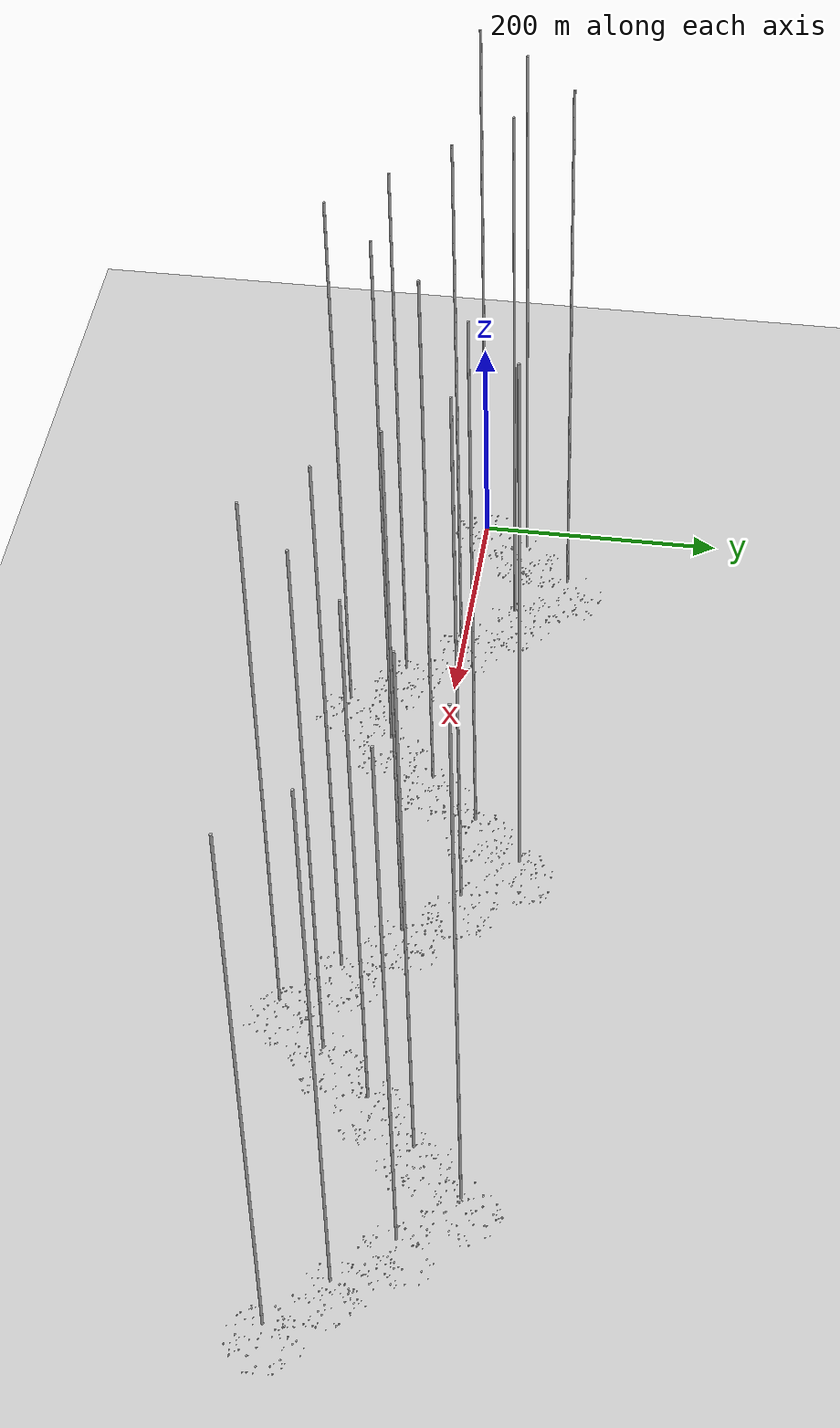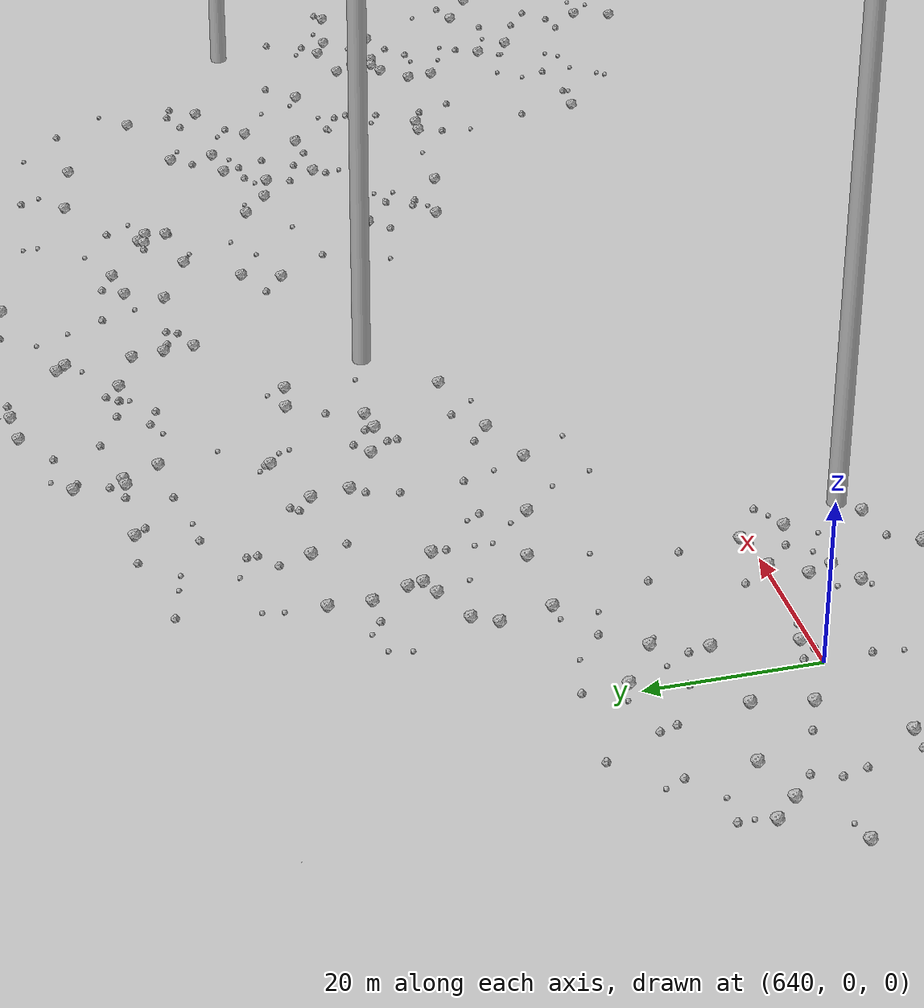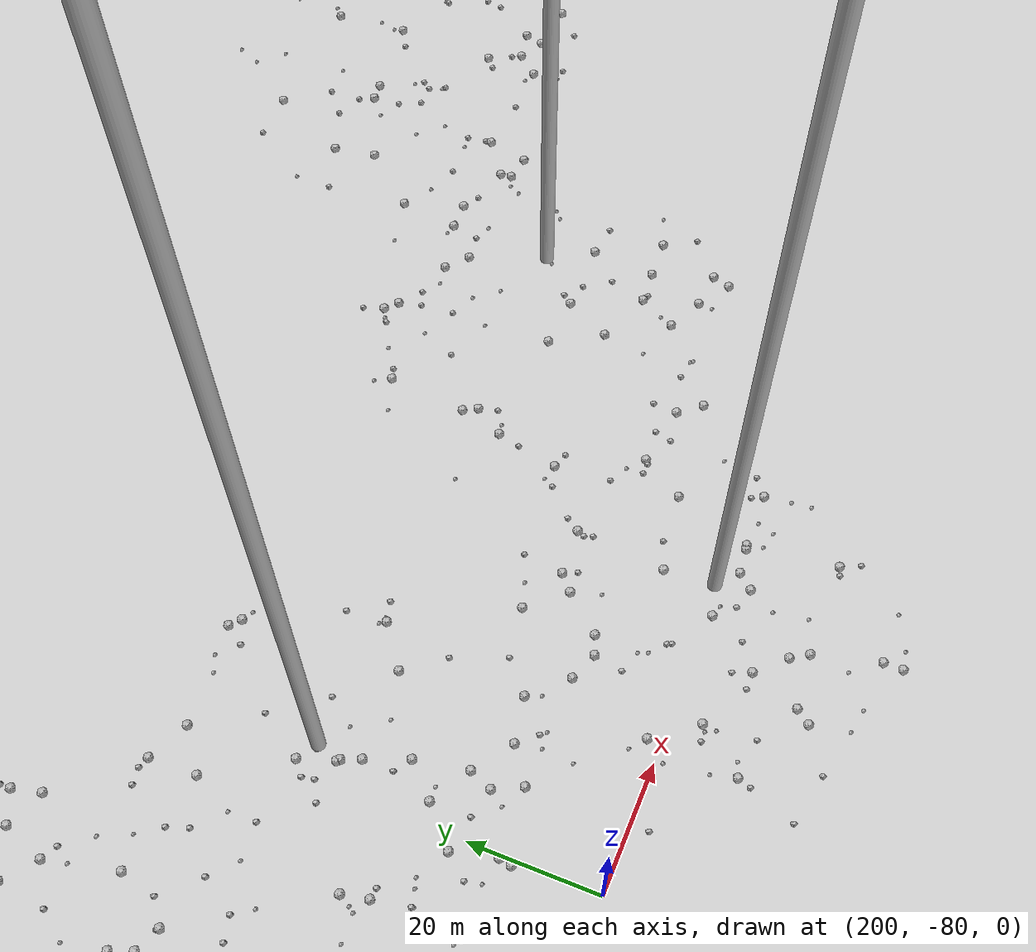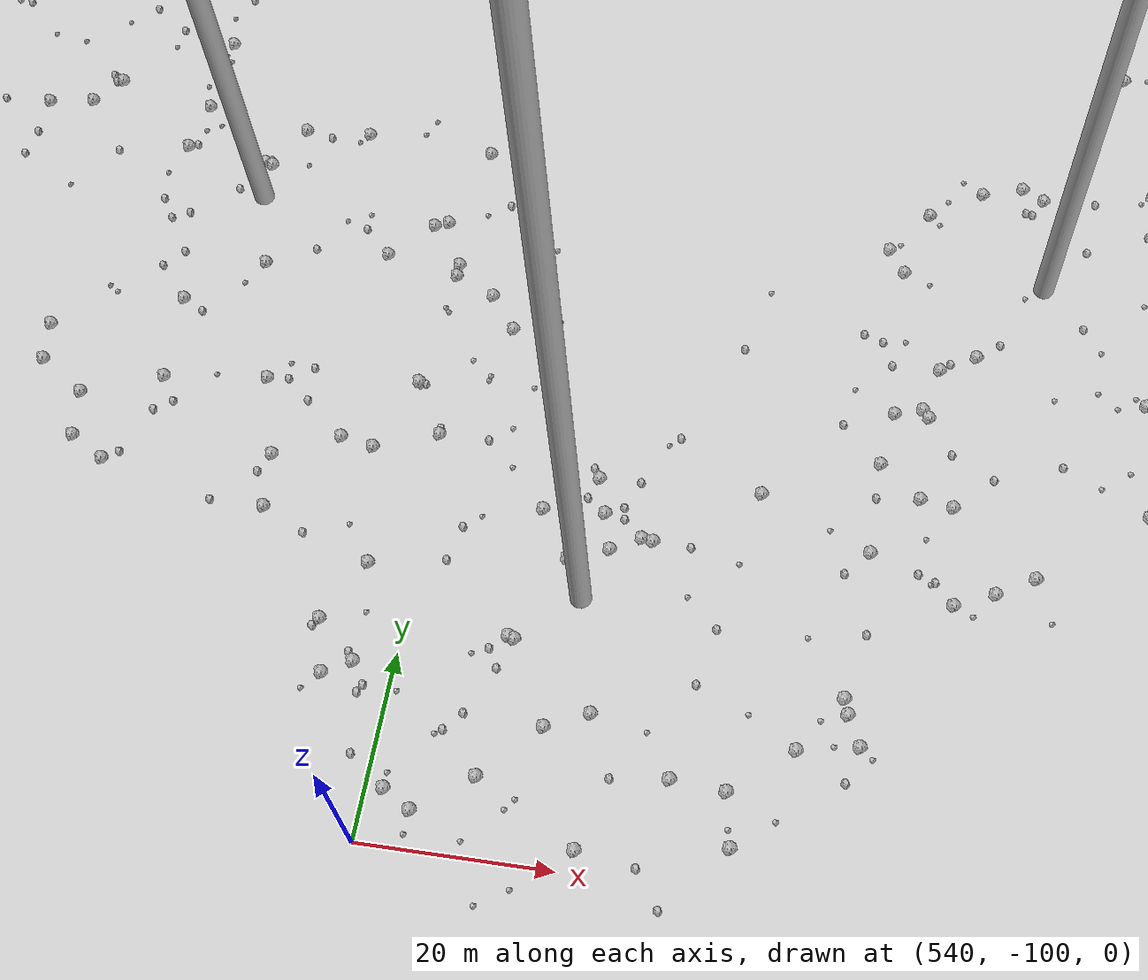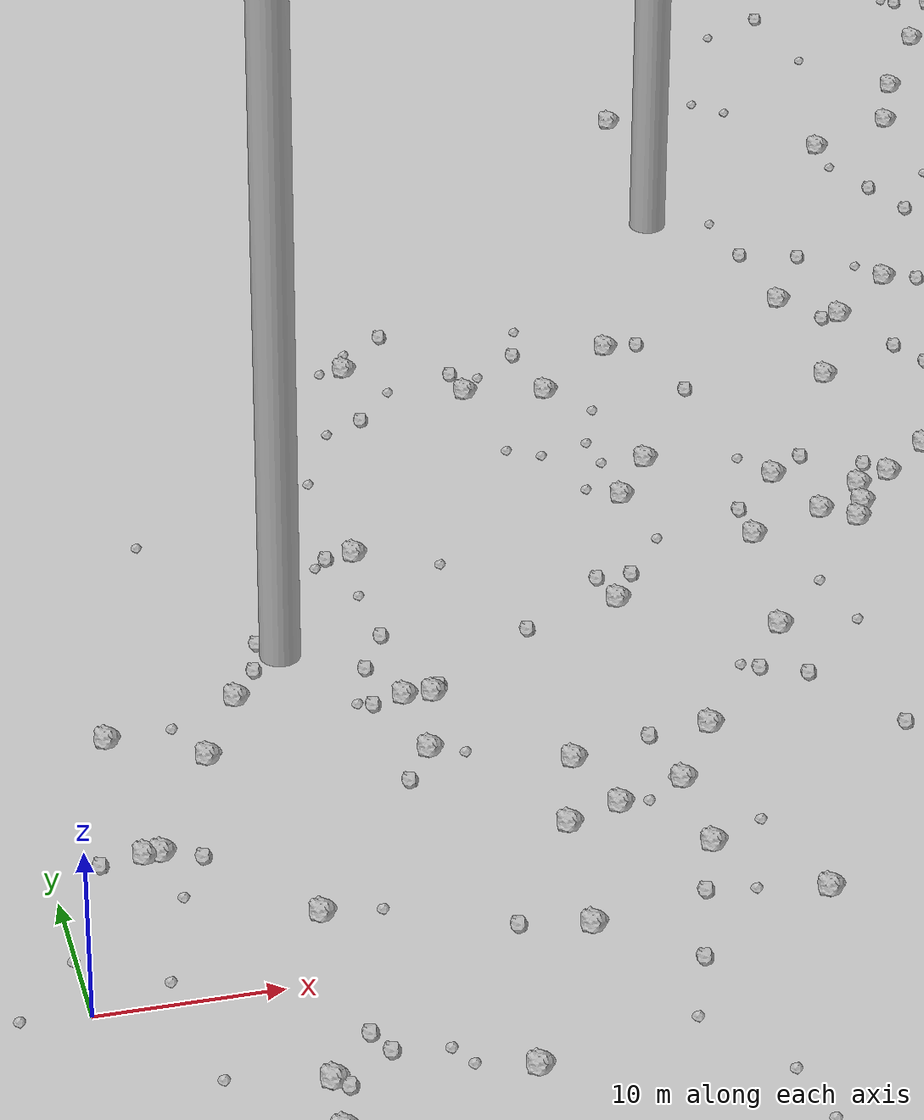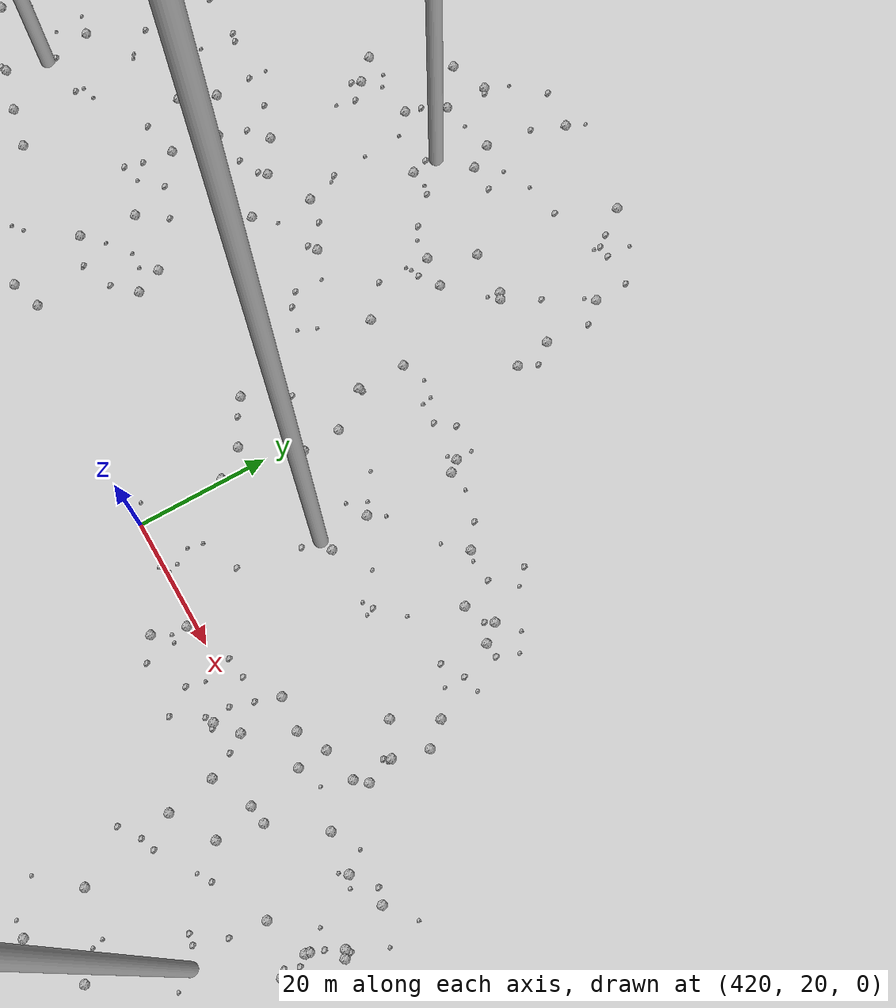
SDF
<sdf version="1.6">
 <world name="default">
  <include><uri>model://custom_ground</uri></include>
  <include><uri>model://sun</uri></include>
  <spherical_coordinates>
   <surface_model>EARTH_WGS84</surface_model>
   <latitude_deg>38.161479</latitude_deg>
   <longitude_deg>-122.454630</longitude_deg>
   <elevation>488.0</elevation>
   <heading_deg>90</heading_deg>
  </spherical_coordinates>
  <model name="rock1_0_0">
   <include><uri>model://rock1</uri><pose>-10.632036444209803 6.372274471117208 0.5 0 0 0</pose></include>
  </model>
  <model name="rock1_0_1">
   <include><uri>model://rock1</uri><pose>34.848359423269876 13.021060215361352 0.5 0 0 0</pose></include>
  </model>
  <model name="rock1_0_2">
   <include><uri>model://rock1</uri><pose>10.674249045546237 -8.245713809858938 0.5 0 0 0</pose></include>
  </model>
  <model name="rock1_0_3">
   <include><uri>model://rock1</uri><pose>1.8040972145692713 -17.042814433260915 0.5 0 0 0</pose></include>
  </model>
  <model name="rock1_0_4">
   <include><uri>model://rock1</uri><pose>23.728844310725798 24.587222124630095 0.5 0 0 0</pose></include>
  </model>
  <model name="rock1_0_5">
   <include><uri>model://rock1</uri><pose>34.68871428586734 6.871091022039927 0.5 0 0 0</pose></include>
  </model>
  <model name="rock1_0_6">
   <include><uri>model://rock1</uri><pose>26.5413794175981 1.2683333718020364 0.5 0 0 0</pose></include>
  </model>
  <model name="rock1_0_7">
   <include><uri>model://rock1</uri><pose>5.169797566897969 12.795053523446136 0.5 0 0 0</pose></include>
  </model>
  <model name="rock1_0_8">
   <include><uri>model://rock1</uri><pose>12.885265354284414 26.668680613347455 0.5 0 0 0</pose></include>
  </model>
  <model name="rock1_0_9">
   <include><uri>model://rock1</uri><pose>8.735900556234125 -25.10414165403146 0.5 0 0 0</pose></include>
  </model>
  <model name="rock1_0_10">
   <include><uri>model://rock1</uri><pose>39.4562576997984 1.4791625804452693 0.5 0 0 0</pose></include>
  </model>
  <model name="rock1_0_11">
   <include><uri>model://rock1</uri><pose>22.185727563246658 19.1486602373512 0.5 0 0 0</pose></include>
  </model>
  <model name="rock1_0_12">
   <include><uri>model://rock1</uri><pose>27.045290867944423 -19.7007777233449 0.5 0 0 0</pose></include>
  </model>
  <model name="rock1_0_13">
   <include><uri>model://rock1</uri><pose>22.07163832003699 24.683890625151534 0.5 0 0 0</pose></include>
  </model>
  <model name="rock1_0_14">
   <include><uri>model://rock1</uri><pose>9.85786008442738 -25.69075873853413 0.5 0 0 0</pose></include>
  </model>
  <model name="rock1_0_15">
   <include><uri>model://rock1</uri><pose>5.118034430884148 24.134490743899505 0.5 0 0 0</pose></include>
  </model>
  <model name="rock1_0_16">
   <include><uri>model://rock1</uri><pose>10.218699277787046 21.268260583251276 0.5 0 0 0</pose></include>
  </model>
  <model name="rock1_0_17">
   <include><uri>model://rock1</uri><pose>-16.761454153035757 7.0480857076533425 0.5 0 0 0</pose></include>
  </model>
  <model name="rock1_0_18">
   <include><uri>model://rock1</uri><pose>-4.631186686617886 -11.514671783711748 0.5 0 0 0</pose></include>
  </model>
  <model name="rock1_0_19">
   <include><uri>model://rock1</uri><pose>20.78717395375554 -9.576174155720715 0.5 0 0 0</pose></include>
  </model>
  <model name="rock1_0_20">
   <include><uri>model://rock1</uri><pose>10.302165633587673 -12.228212884091228 0.5 0 0 0</pose></include>
  </model>
  <model name="rock1_0_21">
   <include><uri>model://rock1</uri><pose>6.073390574323941 12.819559466587222 0.5 0 0 0</pose></include>
  </model>
  <model name="rock1_0_22">
   <include><uri>model://rock1</uri><pose>-12.053141531957143 -12.716821719782644 0.5 0 0 0</pose></include>
  </model>
  <model name="rock1_0_23">
   <include><uri>model://rock1</uri><pose>-5.914739539013741 -10.69749484543275 0.5 0 0 0</pose></include>
  </model>
  <model name="rock1_0_24">
   <include><uri>model://rock1</uri><pose>27.71865807675826 10.38101327733127 0.5 0 0 0</pose></include>
  </model>
  <model name="rock1_0_25">
   <include><uri>model://rock1</uri><pose>13.128024177706344 5.538444775444688 0.5 0 0 0</pose></include>
  </model>
  <model name="rock1_0_26">
   <include><uri>model://rock1</uri><pose>-2.327954899999007 -21.1367077368702 0.5 0 0 0</pose></include>
  </model>
  <model name="rock2_0_0">
   <include><uri>model://rock2</uri><pose>11.504558970836499 -29.123467245690907 0.3 0 0 0</pose></include>
  </model>
  <model name="rock2_0_1">
   <include><uri>model://rock2</uri><pose>-4.533338869804002 19.816963597057374 0.3 0 0 0</pose></include>
  </model>
  <model name="rock2_0_2">
   <include><uri>model://rock2</uri><pose>31.284743039634066 -2.7046985539861694 0.3 0 0 0</pose></include>
  </model>
  <model name="rock2_0_3">
   <include><uri>model://rock2</uri><pose>24.196087900217925 25.41611733267343 0.3 0 0 0</pose></include>
  </model>
  <model name="rock2_0_4">
   <include><uri>model://rock2</uri><pose>0.022021895059360475 -12.192665966183423 0.3 0 0 0</pose></include>
  </model>
  <model name="rock2_0_5">
   <include><uri>model://rock2</uri><pose>11.074209512001936 -28.80674256900753 0.3 0 0 0</pose></include>
  </model>
  <model name="rock2_0_6">
   <include><uri>model://rock2</uri><pose>22.750468868882002 2.278085356820924 0.3 0 0 0</pose></include>
  </model>
  <model name="rock2_0_7">
   <include><uri>model://rock2</uri><pose>20.38832353813921 16.540845562895505 0.3 0 0 0</pose></include>
  </model>
  <model name="rock2_0_8">
   <include><uri>model://rock2</uri><pose>13.236945186105643 -4.896960602196575 0.3 0 0 0</pose></include>
  </model>
  <model name="rock2_0_9">
   <include><uri>model://rock2</uri><pose>-4.477347061056792 14.234044377257064 0.3 0 0 0</pose></include>
  </model>
  <model name="rock2_0_10">
   <include><uri>model://rock2</uri><pose>-6.588274007189096 -21.86085208330828 0.3 0 0 0</pose></include>
  </model>
  <model name="rock2_0_11">
   <include><uri>model://rock2</uri><pose>21.602423518157707 -22.148317547433045 0.3 0 0 0</pose></include>
  </model>
  <model name="rock2_0_12">
   <include><uri>model://rock2</uri><pose>6.871614491457198 -24.80044425370334 0.3 0 0 0</pose></include>
  </model>
  <model name="rock2_0_13">
   <include><uri>model://rock2</uri><pose>8.120527577845778 12.12743274342602 0.3 0 0 0</pose></include>
  </model>
  <model name="rock2_0_14">
   <include><uri>model://rock2</uri><pose>19.18805664996622 -27.288469898237945 0.3 0 0 0</pose></include>
  </model>
  <model name="rock2_0_15">
   <include><uri>model://rock2</uri><pose>9.611088027997972 -23.773496691005143 0.3 0 0 0</pose></include>
  </model>
  <model name="rock2_0_16">
   <include><uri>model://rock2</uri><pose>-15.324857723507261 15.260055963965442 0.3 0 0 0</pose></include>
  </model>
  <model name="rock2_0_17">
   <include><uri>model://rock2</uri><pose>-5.222205621887067 -24.43594372950328 0.3 0 0 0</pose></include>
  </model>
  <model name="rock2_0_18">
   <include><uri>model://rock2</uri><pose>14.410054510468854 29.31704588271308 0.3 0 0 0</pose></include>
  </model>
  <model name="rock2_0_19">
   <include><uri>model://rock2</uri><pose>2.6782864375663777 12.55746437517437 0.3 0 0 0</pose></include>
  </model>
  <model name="rock2_0_20">
   <include><uri>model://rock2</uri><pose>11.312836079729525 -8.797165126554987 0.3 0 0 0</pose></include>
  </model>
  <model name="rock2_0_21">
   <include><uri>model://rock2</uri><pose>-6.239471528179719 6.250573180466134 0.3 0 0 0</pose></include>
  </model>
  <model name="rock2_0_22">
   <include><uri>model://rock2</uri><pose>33.03582471205679 2.911880539802695 0.3 0 0 0</pose></include>
  </model>
  <model name="rock2_0_23">
   <include><uri>model://rock2</uri><pose>25.09102233181052 -21.4675087540346 0.3 0 0 0</pose></include>
  </model>
  <model name="rock2_0_24">
   <include><uri>model://rock2</uri><pose>-16.55301061295157 -3.444558423251028 0.3 0 0 0</pose></include>
  </model>
  <model name="rock2_0_25">
   <include><uri>model://rock2</uri><pose>-3.583807096094347 9.936460011452112 0.3 0 0 0</pose></include>
  </model>
  <model name="rock2_0_26">
   <include><uri>model://rock2</uri><pose>13.95426534652428 -6.530364126503542 0.3 0 0 0</pose></include>
  </model>
  <model name="rock3_0_0">
   <include><uri>model://rock3</uri><pose>37.808432061269585 8.560958880593006 0.2 0 0 0</pose></include>
  </model>
  <model name="rock3_0_1">
   <include><uri>model://rock3</uri><pose>35.69308837825859 2.5206061133350346 0.2 0 0 0</pose></include>
  </model>
  <model name="rock3_0_2">
   <include><uri>model://rock3</uri><pose>33.02474819569644 -12.600251044103338 0.2 0 0 0</pose></include>
  </model>
  <model name="rock3_0_3">
   <include><uri>model://rock3</uri><pose>23.18700820179003 -18.238094026100676 0.2 0 0 0</pose></include>
  </model>
  <model name="rock3_0_4">
   <include><uri>model://rock3</uri><pose>32.50286877384203 11.677095915078326 0.2 0 0 0</pose></include>
  </model>
  <model name="rock3_0_5">
   <include><uri>model://rock3</uri><pose>6.234102244483736 -13.652848041581947 0.2 0 0 0</pose></include>
  </model>
  <model name="rock3_0_6">
   <include><uri>model://rock3</uri><pose>15.449694153700094 -19.824548955817765 0.2 0 0 0</pose></include>
  </model>
  <model name="rock3_0_7">
   <include><uri>model://rock3</uri><pose>5.392121712031255 -6.8548494969930935 0.2 0 0 0</pose></include>
  </model>
  <model name="rock3_0_8">
   <include><uri>model://rock3</uri><pose>-17.658820441716724 1.4964460823876031 0.2 0 0 0</pose></include>
  </model>
  <model name="rock3_0_9">
   <include><uri>model://rock3</uri><pose>33.70655492375871 -16.78403294387467 0.2 0 0 0</pose></include>
  </model>
  <model name="rock3_0_10">
   <include><uri>model://rock3</uri><pose>-14.316322174385816 -9.285941993466395 0.2 0 0 0</pose></include>
  </model>
  <model name="rock3_0_11">
   <include><uri>model://rock3</uri><pose>-7.093344461709352 -24.009176403142273 0.2 0 0 0</pose></include>
  </model>
  <model name="rock3_0_12">
   <include><uri>model://rock3</uri><pose>-3.6339493395887317 0.1719528044966694 0.2 0 0 0</pose></include>
  </model>
  <model name="rock3_0_13">
   <include><uri>model://rock3</uri><pose>16.901002480524866 -6.953701163518268 0.2 0 0 0</pose></include>
  </model>
  <model name="rock3_0_14">
   <include><uri>model://rock3</uri><pose>-0.14629519586746653 4.552882296846889 0.2 0 0 0</pose></include>
  </model>
  <model name="rock3_0_15">
   <include><uri>model://rock3</uri><pose>17.702495453892105 -8.460944681676217 0.2 0 0 0</pose></include>
  </model>
  <model name="rock3_0_16">
   <include><uri>model://rock3</uri><pose>6.40708518168897 8.77189659522574 0.2 0 0 0</pose></include>
  </model>
  <model name="rock3_0_17">
   <include><uri>model://rock3</uri><pose>34.44413883462144 13.533263614181244 0.2 0 0 0</pose></include>
  </model>
  <model name="rock3_0_18">
   <include><uri>model://rock3</uri><pose>0.796720272714218 -18.668962094069467 0.2 0 0 0</pose></include>
  </model>
  <model name="rock3_0_19">
   <include><uri>model://rock3</uri><pose>13.478303188107049 -17.95184425513519 0.2 0 0 0</pose></include>
  </model>
  <model name="rock3_0_20">
   <include><uri>model://rock3</uri><pose>2.917431521047682 -13.004137102717586 0.2 0 0 0</pose></include>
  </model>
  <model name="rock3_0_21">
   <include><uri>model://rock3</uri><pose>19.343222695994392 24.68396973201535 0.2 0 0 0</pose></include>
  </model>
  <model name="rock3_0_22">
   <include><uri>model://rock3</uri><pose>4.3663692292062635 1.683772892117826 0.2 0 0 0</pose></include>
  </model>
  <model name="rock3_0_23">
   <include><uri>model://rock3</uri><pose>16.275879568456617 5.333618236859593 0.2 0 0 0</pose></include>
  </model>
  <model name="rock3_0_24">
   <include><uri>model://rock3</uri><pose>1.797693127092714 -12.300651619348862 0.2 0 0 0</pose></include>
  </model>
  <model name="rock3_0_25">
   <include><uri>model://rock3</uri><pose>29.54080478373986 -7.38467689881821 0.2 0 0 0</pose></include>
  </model>
  <model name="rock3_0_26">
   <include><uri>model://rock3</uri><pose>8.804878104780414 24.60702776573305 0.2 0 0 0</pose></include>
  </model>
  <model name="rock1_1_0">
   <include><uri>model://rock1</uri><pose>44.70156666543175 26.819563070187137 0.5 0 0 0</pose></include>
  </model>
  <model name="rock1_1_1">
   <include><uri>model://rock1</uri><pose>37.828017051563236 17.85906847659365 0.5 0 0 0</pose></include>
  </model>
  <model name="rock1_1_2">
   <include><uri>model://rock1</uri><pose>43.90989086214703 61.21379978758001 0.5 0 0 0</pose></include>
  </model>
  <model name="rock1_1_3">
   <include><uri>model://rock1</uri><pose>54.14545611048357 41.01880258041495 0.5 0 0 0</pose></include>
  </model>
  <model name="rock1_1_4">
   <include><uri>model://rock1</uri><pose>49.48109956580153 43.342284601733795 0.5 0 0 0</pose></include>
  </model>
  <model name="rock1_1_5">
   <include><uri>model://rock1</uri><pose>56.401312448609765 54.502625819974455 0.5 0 0 0</pose></include>
  </model>
  <model name="rock1_1_6">
   <include><uri>model://rock1</uri><pose>29.571892216381226 16.308947284539734 0.5 0 0 0</pose></include>
  </model>
  <model name="rock1_1_7">
   <include><uri>model://rock1</uri><pose>66.60249530082231 40.17141566748041 0.5 0 0 0</pose></include>
  </model>
  <model name="rock1_1_8">
   <include><uri>model://rock1</uri><pose>42.46261658468802 46.982400155177785 0.5 0 0 0</pose></include>
  </model>
  <model name="rock1_1_9">
   <include><uri>model://rock1</uri><pose>58.27582344684879 17.675059077181267 0.5 0 0 0</pose></include>
  </model>
  <model name="rock1_1_10">
   <include><uri>model://rock1</uri><pose>60.37310229245834 22.188470079973722 0.5 0 0 0</pose></include>
  </model>
  <model name="rock1_1_11">
   <include><uri>model://rock1</uri><pose>30.879107643935193 11.550163835166064 0.5 0 0 0</pose></include>
  </model>
  <model name="rock1_1_12">
   <include><uri>model://rock1</uri><pose>52.88146857017914 37.28783597456737 0.5 0 0 0</pose></include>
  </model>
  <model name="rock1_1_13">
   <include><uri>model://rock1</uri><pose>27.086887879831906 62.26092325227661 0.5 0 0 0</pose></include>
  </model>
  <model name="rock1_1_14">
   <include><uri>model://rock1</uri><pose>65.00917095283577 45.07708292180225 0.5 0 0 0</pose></include>
  </model>
  <model name="rock1_1_15">
   <include><uri>model://rock1</uri><pose>36.43323716017042 31.742672441123247 0.5 0 0 0</pose></include>
  </model>
  <model name="rock1_1_16">
   <include><uri>model://rock1</uri><pose>56.36277182284132 41.95769795893721 0.5 0 0 0</pose></include>
  </model>
  <model name="rock1_1_17">
   <include><uri>model://rock1</uri><pose>46.243019699133086 36.81994667115655 0.5 0 0 0</pose></include>
  </model>
  <model name="rock1_1_18">
   <include><uri>model://rock1</uri><pose>63.67916583863564 42.96052867686022 0.5 0 0 0</pose></include>
  </model>
  <model name="rock1_1_19">
   <include><uri>model://rock1</uri><pose>57.99669990073801 23.678318053218767 0.5 0 0 0</pose></include>
  </model>
  <model name="rock1_1_20">
   <include><uri>model://rock1</uri><pose>38.760168212490285 56.67933157364539 0.5 0 0 0</pose></include>
  </model>
  <model name="rock1_1_21">
   <include><uri>model://rock1</uri><pose>51.008596625520745 38.67187199629859 0.5 0 0 0</pose></include>
  </model>
  <model name="rock1_1_22">
   <include><uri>model://rock1</uri><pose>39.875195103077715 43.10534120156897 0.5 0 0 0</pose></include>
  </model>
  <model name="rock1_1_23">
   <include><uri>model://rock1</uri><pose>22.740096824502878 40.25864917316133 0.5 0 0 0</pose></include>
  </model>
  <model name="rock1_1_24">
   <include><uri>model://rock1</uri><pose>53.69443406119026 38.95085249212731 0.5 0 0 0</pose></include>
  </model>
  <model name="rock1_1_25">
   <include><uri>model://rock1</uri><pose>59.577017409305355 44.70068959968149 0.5 0 0 0</pose></include>
  </model>
  <model name="rock1_1_26">
   <include><uri>model://rock1</uri><pose>33.8462939806523 57.750075376767626 0.5 0 0 0</pose></include>
  </model>
  <model name="rock2_1_0">
   <include><uri>model://rock2</uri><pose>30.50662490620194 29.96405908823168 0.3 0 0 0</pose></include>
  </model>
  <model name="rock2_1_1">
   <include><uri>model://rock2</uri><pose>37.91971702307518 61.7983253840072 0.3 0 0 0</pose></include>
  </model>
  <model name="rock2_1_2">
   <include><uri>model://rock2</uri><pose>20.156309142046688 24.333747231983935 0.3 0 0 0</pose></include>
  </model>
  <model name="rock2_1_3">
   <include><uri>model://rock2</uri><pose>20.979500128095985 40.19400512953922 0.3 0 0 0</pose></include>
  </model>
  <model name="rock2_1_4">
   <include><uri>model://rock2</uri><pose>62.51599714432846 46.588835800240155 0.3 0 0 0</pose></include>
  </model>
  <model name="rock2_1_5">
   <include><uri>model://rock2</uri><pose>63.12671675933641 54.8912769057851 0.3 0 0 0</pose></include>
  </model>
  <model name="rock2_1_6">
   <include><uri>model://rock2</uri><pose>34.2043828308425 17.679038922824816 0.3 0 0 0</pose></include>
  </model>
  <model name="rock2_1_7">
   <include><uri>model://rock2</uri><pose>47.3062247697639 54.98306912076936 0.3 0 0 0</pose></include>
  </model>
  <model name="rock2_1_8">
   <include><uri>model://rock2</uri><pose>64.67088116473504 28.569474396745168 0.3 0 0 0</pose></include>
  </model>
  <model name="rock2_1_9">
   <include><uri>model://rock2</uri><pose>55.49215103050044 18.24730351513433 0.3 0 0 0</pose></include>
  </model>
  <model name="rock2_1_10">
   <include><uri>model://rock2</uri><pose>35.85554107775421 34.393673419300995 0.3 0 0 0</pose></include>
  </model>
  <model name="rock2_1_11">
   <include><uri>model://rock2</uri><pose>46.22092215366158 39.964631043078114 0.3 0 0 0</pose></include>
  </model>
  <model name="rock2_1_12">
   <include><uri>model://rock2</uri><pose>42.216856871308465 22.929691385588782 0.3 0 0 0</pose></include>
  </model>
  <model name="rock2_1_13">
   <include><uri>model://rock2</uri><pose>15.128823364965616 32.076695774260884 0.3 0 0 0</pose></include>
  </model>
  <model name="rock2_1_14">
   <include><uri>model://rock2</uri><pose>30.240654400088694 66.1478073819492 0.3 0 0 0</pose></include>
  </model>
  <model name="rock2_1_15">
   <include><uri>model://rock2</uri><pose>22.2024857324068 31.229154647946554 0.3 0 0 0</pose></include>
  </model>
  <model name="rock2_1_16">
   <include><uri>model://rock2</uri><pose>60.56632920153983 38.21111003534415 0.3 0 0 0</pose></include>
  </model>
  <model name="rock2_1_17">
   <include><uri>model://rock2</uri><pose>45.94903899911469 61.31127676995624 0.3 0 0 0</pose></include>
  </model>
  <model name="rock2_1_18">
   <include><uri>model://rock2</uri><pose>55.18918480697879 43.47595221298943 0.3 0 0 0</pose></include>
  </model>
  <model name="rock2_1_19">
   <include><uri>model://rock2</uri><pose>48.406891683071144 15.70079624860389 0.3 0 0 0</pose></include>
  </model>
  <model name="rock2_1_20">
   <include><uri>model://rock2</uri><pose>26.68760118726238 55.91185407359454 0.3 0 0 0</pose></include>
  </model>
  <model name="rock2_1_21">
   <include><uri>model://rock2</uri><pose>33.45873041684956 60.294531907758845 0.3 0 0 0</pose></include>
  </model>
  <model name="rock2_1_22">
   <include><uri>model://rock2</uri><pose>51.729463846093864 45.24064365478544 0.3 0 0 0</pose></include>
  </model>
  <model name="rock2_1_23">
   <include><uri>model://rock2</uri><pose>20.56526448683477 28.062499381925655 0.3 0 0 0</pose></include>
  </model>
  <model name="rock2_1_24">
   <include><uri>model://rock2</uri><pose>67.49408885413749 34.164847926844885 0.3 0 0 0</pose></include>
  </model>
  <model name="rock2_1_25">
   <include><uri>model://rock2</uri><pose>44.7291300439954 21.763756390301197 0.3 0 0 0</pose></include>
  </model>
  <model name="rock2_1_26">
   <include><uri>model://rock2</uri><pose>37.94166894545852 34.40710605117751 0.3 0 0 0</pose></include>
  </model>
  <model name="rock3_1_0">
   <include><uri>model://rock3</uri><pose>21.86785172888801 49.05270286160293 0.2 0 0 0</pose></include>
  </model>
  <model name="rock3_1_1">
   <include><uri>model://rock3</uri><pose>24.02343543780244 18.5889036248229 0.2 0 0 0</pose></include>
  </model>
  <model name="rock3_1_2">
   <include><uri>model://rock3</uri><pose>54.46248252088519 25.79617194800141 0.2 0 0 0</pose></include>
  </model>
  <model name="rock3_1_3">
   <include><uri>model://rock3</uri><pose>48.44384798143531 31.186442186115674 0.2 0 0 0</pose></include>
  </model>
  <model name="rock3_1_4">
   <include><uri>model://rock3</uri><pose>35.07175201443995 59.53019009998565 0.2 0 0 0</pose></include>
  </model>
  <model name="rock3_1_5">
   <include><uri>model://rock3</uri><pose>38.01368076764294 44.52075695420443 0.2 0 0 0</pose></include>
  </model>
  <model name="rock3_1_6">
   <include><uri>model://rock3</uri><pose>39.51559843930181 49.96486654892157 0.2 0 0 0</pose></include>
  </model>
  <model name="rock3_1_7">
   <include><uri>model://rock3</uri><pose>40.97202119883494 53.815508512961884 0.2 0 0 0</pose></include>
  </model>
  <model name="rock3_1_8">
   <include><uri>model://rock3</uri><pose>64.10210270937023 47.287967517514 0.2 0 0 0</pose></include>
  </model>
  <model name="rock3_1_9">
   <include><uri>model://rock3</uri><pose>47.97147902915485 45.967746326043645 0.2 0 0 0</pose></include>
  </model>
  <model name="rock3_1_10">
   <include><uri>model://rock3</uri><pose>38.82060006752283 64.8756646420559 0.2 0 0 0</pose></include>
  </model>
  <model name="rock3_1_11">
   <include><uri>model://rock3</uri><pose>41.28089130270854 23.539496977702107 0.2 0 0 0</pose></include>
  </model>
  <model name="rock3_1_12">
   <include><uri>model://rock3</uri><pose>40.54696389475362 37.975478105758356 0.2 0 0 0</pose></include>
  </model>
  <model name="rock3_1_13">
   <include><uri>model://rock3</uri><pose>21.961983713602535 35.845746436553554 0.2 0 0 0</pose></include>
  </model>
  <model name="rock3_1_14">
   <include><uri>model://rock3</uri><pose>27.38024406174513 38.140575301205025 0.2 0 0 0</pose></include>
  </model>
  <model name="rock3_1_15">
   <include><uri>model://rock3</uri><pose>36.45607306854155 49.097703594704925 0.2 0 0 0</pose></include>
  </model>
  <model name="rock3_1_16">
   <include><uri>model://rock3</uri><pose>25.503843240247072 62.320602253914565 0.2 0 0 0</pose></include>
  </model>
  <model name="rock3_1_17">
   <include><uri>model://rock3</uri><pose>54.58891712973262 26.147802243146028 0.2 0 0 0</pose></include>
  </model>
  <model name="rock3_1_18">
   <include><uri>model://rock3</uri><pose>10.418508807508346 44.14709027936963 0.2 0 0 0</pose></include>
  </model>
  <model name="rock3_1_19">
   <include><uri>model://rock3</uri><pose>27.53078107973741 64.4537808703256 0.2 0 0 0</pose></include>
  </model>
  <model name="rock3_1_20">
   <include><uri>model://rock3</uri><pose>49.240427152043154 26.611141127238398 0.2 0 0 0</pose></include>
  </model>
  <model name="rock3_1_21">
   <include><uri>model://rock3</uri><pose>20.172039857366332 39.39347359390102 0.2 0 0 0</pose></include>
  </model>
  <model name="rock3_1_22">
   <include><uri>model://rock3</uri><pose>24.26606264627636 54.70102354355737 0.2 0 0 0</pose></include>
  </model>
  <model name="rock3_1_23">
   <include><uri>model://rock3</uri><pose>62.599429633865874 35.52595042536475 0.2 0 0 0</pose></include>
  </model>
  <model name="rock3_1_24">
   <include><uri>model://rock3</uri><pose>29.148913132554554 59.05194845795158 0.2 0 0 0</pose></include>
  </model>
  <model name="rock3_1_25">
   <include><uri>model://rock3</uri><pose>39.765625982421255 47.384911315216065 0.2 0 0 0</pose></include>
  </model>
  <model name="rock3_1_26">
   <include><uri>model://rock3</uri><pose>34.530065711456984 50.21117028610953 0.2 0 0 0</pose></include>
  </model>
  <model name="rock1_2_0">
   <include><uri>model://rock1</uri><pose>101.66557587216734 83.17745958101418 0.5 0 0 0</pose></include>
  </model>
  <model name="rock1_2_1">
   <include><uri>model://rock1</uri><pose>103.37988293762513 73.16559999794336 0.5 0 0 0</pose></include>
  </model>
  <model name="rock1_2_2">
   <include><uri>model://rock1</uri><pose>76.5814945290233 88.76027812660584 0.5 0 0 0</pose></include>
  </model>
  <model name="rock1_2_3">
   <include><uri>model://rock1</uri><pose>67.57677794797566 56.326736109728294 0.5 0 0 0</pose></include>
  </model>
  <model name="rock1_2_4">
   <include><uri>model://rock1</uri><pose>74.14538865819185 94.0923477108642 0.5 0 0 0</pose></include>
  </model>
  <model name="rock1_2_5">
   <include><uri>model://rock1</uri><pose>102.7483805919034 70.99424891316238 0.5 0 0 0</pose></include>
  </model>
  <model name="rock1_2_6">
   <include><uri>model://rock1</uri><pose>81.5678704590845 107.0134263774485 0.5 0 0 0</pose></include>
  </model>
  <model name="rock1_2_7">
   <include><uri>model://rock1</uri><pose>53.0600706431018 93.07661247937787 0.5 0 0 0</pose></include>
  </model>
  <model name="rock1_2_8">
   <include><uri>model://rock1</uri><pose>98.74562644868364 89.86268840794133 0.5 0 0 0</pose></include>
  </model>
  <model name="rock1_2_9">
   <include><uri>model://rock1</uri><pose>103.33802378087185 67.42152031063571 0.5 0 0 0</pose></include>
  </model>
  <model name="rock1_2_10">
   <include><uri>model://rock1</uri><pose>96.74046724605572 79.03375059075334 0.5 0 0 0</pose></include>
  </model>
  <model name="rock1_2_11">
   <include><uri>model://rock1</uri><pose>92.85544115346457 87.62433944224351 0.5 0 0 0</pose></include>
  </model>
  <model name="rock1_2_12">
   <include><uri>model://rock1</uri><pose>89.83394290480013 52.56746714933767 0.5 0 0 0</pose></include>
  </model>
  <model name="rock1_2_13">
   <include><uri>model://rock1</uri><pose>80.57246035111044 83.38777592665778 0.5 0 0 0</pose></include>
  </model>
  <model name="rock1_2_14">
   <include><uri>model://rock1</uri><pose>78.28860414285884 101.41215671782857 0.5 0 0 0</pose></include>
  </model>
  <model name="rock1_2_15">
   <include><uri>model://rock1</uri><pose>95.55215879314683 100.36639918465536 0.5 0 0 0</pose></include>
  </model>
  <model name="rock1_2_16">
   <include><uri>model://rock1</uri><pose>66.02147273554968 85.84807595201808 0.5 0 0 0</pose></include>
  </model>
  <model name="rock1_2_17">
   <include><uri>model://rock1</uri><pose>59.81368120643887 62.01180740077221 0.5 0 0 0</pose></include>
  </model>
  <model name="rock1_2_18">
   <include><uri>model://rock1</uri><pose>92.04918074348663 65.97595390208548 0.5 0 0 0</pose></include>
  </model>
  <model name="rock1_2_19">
   <include><uri>model://rock1</uri><pose>80.33110117143187 91.8481042838599 0.5 0 0 0</pose></include>
  </model>
  <model name="rock1_2_20">
   <include><uri>model://rock1</uri><pose>71.99663600856917 88.78361293986475 0.5 0 0 0</pose></include>
  </model>
  <model name="rock1_2_21">
   <include><uri>model://rock1</uri><pose>72.9500707009625 76.95475942613507 0.5 0 0 0</pose></include>
  </model>
  <model name="rock1_2_22">
   <include><uri>model://rock1</uri><pose>78.47154138027857 92.84742241940364 0.5 0 0 0</pose></include>
  </model>
  <model name="rock1_2_23">
   <include><uri>model://rock1</uri><pose>94.34568333984993 86.2949508708547 0.5 0 0 0</pose></include>
  </model>
  <model name="rock1_2_24">
   <include><uri>model://rock1</uri><pose>64.27836174258323 66.28620974867223 0.5 0 0 0</pose></include>
  </model>
  <model name="rock1_2_25">
   <include><uri>model://rock1</uri><pose>109.1961625045407 76.66932080662095 0.5 0 0 0</pose></include>
  </model>
  <model name="rock1_2_26">
   <include><uri>model://rock1</uri><pose>56.57928851583671 64.82121250146088 0.5 0 0 0</pose></include>
  </model>
  <model name="rock2_2_0">
   <include><uri>model://rock2</uri><pose>84.84601893779174 58.33586237267782 0.3 0 0 0</pose></include>
  </model>
  <model name="rock2_2_1">
   <include><uri>model://rock2</uri><pose>89.89599039455526 88.69470021015026 0.3 0 0 0</pose></include>
  </model>
  <model name="rock2_2_2">
   <include><uri>model://rock2</uri><pose>61.87688202497341 57.36962505861226 0.3 0 0 0</pose></include>
  </model>
  <model name="rock2_2_3">
   <include><uri>model://rock2</uri><pose>79.83932809679303 72.18639667352068 0.3 0 0 0</pose></include>
  </model>
  <model name="rock2_2_4">
   <include><uri>model://rock2</uri><pose>68.87869979031557 75.62725867681405 0.3 0 0 0</pose></include>
  </model>
  <model name="rock2_2_5">
   <include><uri>model://rock2</uri><pose>93.62497677805837 97.48697412639663 0.3 0 0 0</pose></include>
  </model>
  <model name="rock2_2_6">
   <include><uri>model://rock2</uri><pose>104.02951350635269 97.48943608453537 0.3 0 0 0</pose></include>
  </model>
  <model name="rock2_2_7">
   <include><uri>model://rock2</uri><pose>83.32735591695408 59.58852689903994 0.3 0 0 0</pose></include>
  </model>
  <model name="rock2_2_8">
   <include><uri>model://rock2</uri><pose>92.8850843817644 98.6307422657368 0.3 0 0 0</pose></include>
  </model>
  <model name="rock2_2_9">
   <include><uri>model://rock2</uri><pose>107.36450212863204 75.5064079382231 0.3 0 0 0</pose></include>
  </model>
  <model name="rock2_2_10">
   <include><uri>model://rock2</uri><pose>81.08825056116947 56.188533964298664 0.3 0 0 0</pose></include>
  </model>
  <model name="rock2_2_11">
   <include><uri>model://rock2</uri><pose>101.37482114886984 72.1763468428179 0.3 0 0 0</pose></include>
  </model>
  <model name="rock2_2_12">
   <include><uri>model://rock2</uri><pose>67.48987810478076 79.14183963854893 0.3 0 0 0</pose></include>
  </model>
  <model name="rock2_2_13">
   <include><uri>model://rock2</uri><pose>94.33583011015457 57.74209396729001 0.3 0 0 0</pose></include>
  </model>
  <model name="rock2_2_14">
   <include><uri>model://rock2</uri><pose>58.558796978607916 61.94296393324572 0.3 0 0 0</pose></include>
  </model>
  <model name="rock2_2_15">
   <include><uri>model://rock2</uri><pose>89.02869630225383 90.55542896824365 0.3 0 0 0</pose></include>
  </model>
  <model name="rock2_2_16">
   <include><uri>model://rock2</uri><pose>79.12172964318373 107.91082146793016 0.3 0 0 0</pose></include>
  </model>
  <model name="rock2_2_17">
   <include><uri>model://rock2</uri><pose>68.20920975027482 107.46162334333661 0.3 0 0 0</pose></include>
  </model>
  <model name="rock2_2_18">
   <include><uri>model://rock2</uri><pose>97.28719524448321 102.46922536344626 0.3 0 0 0</pose></include>
  </model>
  <model name="rock2_2_19">
   <include><uri>model://rock2</uri><pose>87.51802238622402 61.92692828001179 0.3 0 0 0</pose></include>
  </model>
  <model name="rock2_2_20">
   <include><uri>model://rock2</uri><pose>66.33367777469019 65.79491232261834 0.3 0 0 0</pose></include>
  </model>
  <model name="rock2_2_21">
   <include><uri>model://rock2</uri><pose>79.53517968868043 82.42091413094967 0.3 0 0 0</pose></include>
  </model>
  <model name="rock2_2_22">
   <include><uri>model://rock2</uri><pose>67.3412302567584 53.40797693728107 0.3 0 0 0</pose></include>
  </model>
  <model name="rock2_2_23">
   <include><uri>model://rock2</uri><pose>59.64536288655424 70.50636768393358 0.3 0 0 0</pose></include>
  </model>
  <model name="rock2_2_24">
   <include><uri>model://rock2</uri><pose>97.97225825399914 87.57152121539153 0.3 0 0 0</pose></include>
  </model>
  <model name="rock2_2_25">
   <include><uri>model://rock2</uri><pose>82.14918082679635 97.91320115820247 0.3 0 0 0</pose></include>
  </model>
  <model name="rock2_2_26">
   <include><uri>model://rock2</uri><pose>56.01458041514081 71.64587309658151 0.3 0 0 0</pose></include>
  </model>
  <model name="rock3_2_0">
   <include><uri>model://rock3</uri><pose>92.4566359775378 54.54436997643715 0.2 0 0 0</pose></include>
  </model>
  <model name="rock3_2_1">
   <include><uri>model://rock3</uri><pose>88.48421479887392 73.65363225912799 0.2 0 0 0</pose></include>
  </model>
  <model name="rock3_2_2">
   <include><uri>model://rock3</uri><pose>95.34617476492397 102.75825084786455 0.2 0 0 0</pose></include>
  </model>
  <model name="rock3_2_3">
   <include><uri>model://rock3</uri><pose>91.29827269720067 60.3819953352799 0.2 0 0 0</pose></include>
  </model>
  <model name="rock3_2_4">
   <include><uri>model://rock3</uri><pose>65.9280494024095 82.88183426342302 0.2 0 0 0</pose></include>
  </model>
  <model name="rock3_2_5">
   <include><uri>model://rock3</uri><pose>62.97670141473905 68.4750876896812 0.2 0 0 0</pose></include>
  </model>
  <model name="rock3_2_6">
   <include><uri>model://rock3</uri><pose>55.42423908077439 76.58270456120958 0.2 0 0 0</pose></include>
  </model>
  <model name="rock3_2_7">
   <include><uri>model://rock3</uri><pose>100.63840468428765 85.46280536261936 0.2 0 0 0</pose></include>
  </model>
  <model name="rock3_2_8">
   <include><uri>model://rock3</uri><pose>63.971353093200264 105.27583898678728 0.2 0 0 0</pose></include>
  </model>
  <model name="rock3_2_9">
   <include><uri>model://rock3</uri><pose>74.66512409297921 85.83762747383724 0.2 0 0 0</pose></include>
  </model>
  <model name="rock3_2_10">
   <include><uri>model://rock3</uri><pose>101.03909682519652 84.36623445599317 0.2 0 0 0</pose></include>
  </model>
  <model name="rock3_2_11">
   <include><uri>model://rock3</uri><pose>92.54565835512744 87.46057823545516 0.2 0 0 0</pose></include>
  </model>
  <model name="rock3_2_12">
   <include><uri>model://rock3</uri><pose>83.74493735192735 56.02294029503186 0.2 0 0 0</pose></include>
  </model>
  <model name="rock3_2_13">
   <include><uri>model://rock3</uri><pose>94.5443067705572 100.06753345945465 0.2 0 0 0</pose></include>
  </model>
  <model name="rock3_2_14">
   <include><uri>model://rock3</uri><pose>86.22458270056825 87.64501318881531 0.2 0 0 0</pose></include>
  </model>
  <model name="rock3_2_15">
   <include><uri>model://rock3</uri><pose>78.32037577784834 108.5667644449052 0.2 0 0 0</pose></include>
  </model>
  <model name="rock3_2_16">
   <include><uri>model://rock3</uri><pose>82.64335604054497 72.72789228598111 0.2 0 0 0</pose></include>
  </model>
  <model name="rock3_2_17">
   <include><uri>model://rock3</uri><pose>61.419877824133934 92.9207256139776 0.2 0 0 0</pose></include>
  </model>
  <model name="rock3_2_18">
   <include><uri>model://rock3</uri><pose>82.20534711706904 95.41297158720874 0.2 0 0 0</pose></include>
  </model>
  <model name="rock3_2_19">
   <include><uri>model://rock3</uri><pose>89.61003042468946 92.13183221070614 0.2 0 0 0</pose></include>
  </model>
  <model name="rock3_2_20">
   <include><uri>model://rock3</uri><pose>71.08508629921894 56.88294900038976 0.2 0 0 0</pose></include>
  </model>
  <model name="rock3_2_21">
   <include><uri>model://rock3</uri><pose>82.9324895377943 71.32239881630515 0.2 0 0 0</pose></include>
  </model>
  <model name="rock3_2_22">
   <include><uri>model://rock3</uri><pose>75.4990288384829 60.64763006165409 0.2 0 0 0</pose></include>
  </model>
  <model name="rock3_2_23">
   <include><uri>model://rock3</uri><pose>59.58783962346007 94.74178221957784 0.2 0 0 0</pose></include>
  </model>
  <model name="rock3_2_24">
   <include><uri>model://rock3</uri><pose>103.6608368866967 82.01421684843864 0.2 0 0 0</pose></include>
  </model>
  <model name="rock3_2_25">
   <include><uri>model://rock3</uri><pose>71.94729386751125 80.57371925659251 0.2 0 0 0</pose></include>
  </model>
  <model name="rock3_2_26">
   <include><uri>model://rock3</uri><pose>69.22206023188164 99.96529466824887 0.2 0 0 0</pose></include>
  </model>
  <model name="rock1_3_0">
   <include><uri>model://rock1</uri><pose>127.15551004285129 30.440784812374755 0.5 0 0 0</pose></include>
  </model>
  <model name="rock1_3_1">
   <include><uri>model://rock1</uri><pose>126.79435607253133 49.57299372697386 0.5 0 0 0</pose></include>
  </model>
  <model name="rock1_3_2">
   <include><uri>model://rock1</uri><pose>128.78656362997833 56.60923055668856 0.5 0 0 0</pose></include>
  </model>
  <model name="rock1_3_3">
   <include><uri>model://rock1</uri><pose>110.8452042204554 55.562482428010455 0.5 0 0 0</pose></include>
  </model>
  <model name="rock1_3_4">
   <include><uri>model://rock1</uri><pose>124.3373154239676 69.32695981842048 0.5 0 0 0</pose></include>
  </model>
  <model name="rock1_3_5">
   <include><uri>model://rock1</uri><pose>146.838676070887 50.252585635711746 0.5 0 0 0</pose></include>
  </model>
  <model name="rock1_3_6">
   <include><uri>model://rock1</uri><pose>143.8246483192393 31.78194823122368 0.5 0 0 0</pose></include>
  </model>
  <model name="rock1_3_7">
   <include><uri>model://rock1</uri><pose>99.11382926441127 38.081322377934285 0.5 0 0 0</pose></include>
  </model>
  <model name="rock1_3_8">
   <include><uri>model://rock1</uri><pose>121.43868435176628 10.419212467356868 0.5 0 0 0</pose></include>
  </model>
  <model name="rock1_3_9">
   <include><uri>model://rock1</uri><pose>144.58808239744346 36.15355478640885 0.5 0 0 0</pose></include>
  </model>
  <model name="rock1_3_10">
   <include><uri>model://rock1</uri><pose>136.44785138753124 28.72177118398961 0.5 0 0 0</pose></include>
  </model>
  <model name="rock1_3_11">
   <include><uri>model://rock1</uri><pose>140.47514798817562 33.28475911587641 0.5 0 0 0</pose></include>
  </model>
  <model name="rock1_3_12">
   <include><uri>model://rock1</uri><pose>125.4430569798356 55.12312413962029 0.5 0 0 0</pose></include>
  </model>
  <model name="rock1_3_13">
   <include><uri>model://rock1</uri><pose>108.55095288458936 65.5359223123182 0.5 0 0 0</pose></include>
  </model>
  <model name="rock1_3_14">
   <include><uri>model://rock1</uri><pose>137.97529858372764 24.987115192411192 0.5 0 0 0</pose></include>
  </model>
  <model name="rock1_3_15">
   <include><uri>model://rock1</uri><pose>148.25311463584376 38.53933926371582 0.5 0 0 0</pose></include>
  </model>
  <model name="rock1_3_16">
   <include><uri>model://rock1</uri><pose>111.11710887754501 27.652765616114905 0.5 0 0 0</pose></include>
  </model>
  <model name="rock1_3_17">
   <include><uri>model://rock1</uri><pose>128.0711420451924 42.29408955520206 0.5 0 0 0</pose></include>
  </model>
  <model name="rock1_3_18">
   <include><uri>model://rock1</uri><pose>114.50237534913722 25.577050010722758 0.5 0 0 0</pose></include>
  </model>
  <model name="rock1_3_19">
   <include><uri>model://rock1</uri><pose>96.09202658691335 34.30305275480327 0.5 0 0 0</pose></include>
  </model>
  <model name="rock1_3_20">
   <include><uri>model://rock1</uri><pose>110.74016931157087 65.20193386991245 0.5 0 0 0</pose></include>
  </model>
  <model name="rock1_3_21">
   <include><uri>model://rock1</uri><pose>144.3068259095038 53.38547360331768 0.5 0 0 0</pose></include>
  </model>
  <model name="rock1_3_22">
   <include><uri>model://rock1</uri><pose>111.23173190108001 68.1130560833113 0.5 0 0 0</pose></include>
  </model>
  <model name="rock1_3_23">
   <include><uri>model://rock1</uri><pose>120.71120705983809 37.33284682584973 0.5 0 0 0</pose></include>
  </model>
  <model name="rock1_3_24">
   <include><uri>model://rock1</uri><pose>91.54104609803198 38.01995809424236 0.5 0 0 0</pose></include>
  </model>
  <model name="rock1_3_25">
   <include><uri>model://rock1</uri><pose>132.8894149090103 39.0050030530101 0.5 0 0 0</pose></include>
  </model>
  <model name="rock1_3_26">
   <include><uri>model://rock1</uri><pose>149.153743226511 42.96933649518146 0.5 0 0 0</pose></include>
  </model>
  <model name="rock2_3_0">
   <include><uri>model://rock2</uri><pose>140.87926386723288 35.42081490383603 0.3 0 0 0</pose></include>
  </model>
  <model name="rock2_3_1">
   <include><uri>model://rock2</uri><pose>99.86283356546937 39.34793173374814 0.3 0 0 0</pose></include>
  </model>
  <model name="rock2_3_2">
   <include><uri>model://rock2</uri><pose>111.02249479419083 24.33753498318575 0.3 0 0 0</pose></include>
  </model>
  <model name="rock2_3_3">
   <include><uri>model://rock2</uri><pose>96.67052778189026 50.43157555458854 0.3 0 0 0</pose></include>
  </model>
  <model name="rock2_3_4">
   <include><uri>model://rock2</uri><pose>104.90475832636619 55.150900649839805 0.3 0 0 0</pose></include>
  </model>
  <model name="rock2_3_5">
   <include><uri>model://rock2</uri><pose>136.5817191927453 27.16347403077311 0.3 0 0 0</pose></include>
  </model>
  <model name="rock2_3_6">
   <include><uri>model://rock2</uri><pose>120.99183017360424 53.14141384461847 0.3 0 0 0</pose></include>
  </model>
  <model name="rock2_3_7">
   <include><uri>model://rock2</uri><pose>98.30305081837075 33.89677422396578 0.3 0 0 0</pose></include>
  </model>
  <model name="rock2_3_8">
   <include><uri>model://rock2</uri><pose>113.47063051941237 36.218593276760764 0.3 0 0 0</pose></include>
  </model>
  <model name="rock2_3_9">
   <include><uri>model://rock2</uri><pose>101.04090939205031 50.97364259705991 0.3 0 0 0</pose></include>
  </model>
  <model name="rock2_3_10">
   <include><uri>model://rock2</uri><pose>98.61326826234924 46.48043306771531 0.3 0 0 0</pose></include>
  </model>
  <model name="rock2_3_11">
   <include><uri>model://rock2</uri><pose>100.80623620991722 23.73284713398757 0.3 0 0 0</pose></include>
  </model>
  <model name="rock2_3_12">
   <include><uri>model://rock2</uri><pose>109.02904830119837 39.66838234151309 0.3 0 0 0</pose></include>
  </model>
  <model name="rock2_3_13">
   <include><uri>model://rock2</uri><pose>93.45249986527762 44.26581274813989 0.3 0 0 0</pose></include>
  </model>
  <model name="rock2_3_14">
   <include><uri>model://rock2</uri><pose>138.95395652742337 52.41529873907491 0.3 0 0 0</pose></include>
  </model>
  <model name="rock2_3_15">
   <include><uri>model://rock2</uri><pose>97.85271651853574 57.340743159925395 0.3 0 0 0</pose></include>
  </model>
  <model name="rock2_3_16">
   <include><uri>model://rock2</uri><pose>133.033502201352 63.8565548961694 0.3 0 0 0</pose></include>
  </model>
  <model name="rock2_3_17">
   <include><uri>model://rock2</uri><pose>108.11558792717076 65.73200717586087 0.3 0 0 0</pose></include>
  </model>
  <model name="rock2_3_18">
   <include><uri>model://rock2</uri><pose>94.7611434393983 50.46791169447049 0.3 0 0 0</pose></include>
  </model>
  <model name="rock2_3_19">
   <include><uri>model://rock2</uri><pose>112.78832016977177 44.181472634109525 0.3 0 0 0</pose></include>
  </model>
  <model name="rock2_3_20">
   <include><uri>model://rock2</uri><pose>93.79842857284066 46.41726135679901 0.3 0 0 0</pose></include>
  </model>
  <model name="rock2_3_21">
   <include><uri>model://rock2</uri><pose>138.47740982057587 44.045482027001704 0.3 0 0 0</pose></include>
  </model>
  <model name="rock2_3_22">
   <include><uri>model://rock2</uri><pose>118.12036126503037 55.87682802787474 0.3 0 0 0</pose></include>
  </model>
  <model name="rock2_3_23">
   <include><uri>model://rock2</uri><pose>129.85732642082553 21.48418107045457 0.3 0 0 0</pose></include>
  </model>
  <model name="rock2_3_24">
   <include><uri>model://rock2</uri><pose>130.89102701023066 26.71171634845228 0.3 0 0 0</pose></include>
  </model>
  <model name="rock2_3_25">
   <include><uri>model://rock2</uri><pose>119.27775268735397 49.223230555072796 0.3 0 0 0</pose></include>
  </model>
  <model name="rock2_3_26">
   <include><uri>model://rock2</uri><pose>100.32116366641499 18.176809277091834 0.3 0 0 0</pose></include>
  </model>
  <model name="rock3_3_0">
   <include><uri>model://rock3</uri><pose>93.1800552739347 39.376907964947044 0.2 0 0 0</pose></include>
  </model>
  <model name="rock3_3_1">
   <include><uri>model://rock3</uri><pose>135.0746740426961 36.386235022656074 0.2 0 0 0</pose></include>
  </model>
  <model name="rock3_3_2">
   <include><uri>model://rock3</uri><pose>110.27484944382961 64.06110973016246 0.2 0 0 0</pose></include>
  </model>
  <model name="rock3_3_3">
   <include><uri>model://rock3</uri><pose>134.11264930036842 64.13207382558386 0.2 0 0 0</pose></include>
  </model>
  <model name="rock3_3_4">
   <include><uri>model://rock3</uri><pose>146.66765555682062 27.06744010379039 0.2 0 0 0</pose></include>
  </model>
  <model name="rock3_3_5">
   <include><uri>model://rock3</uri><pose>112.36958036423235 55.19932196758142 0.2 0 0 0</pose></include>
  </model>
  <model name="rock3_3_6">
   <include><uri>model://rock3</uri><pose>144.38383347442138 50.19934350230641 0.2 0 0 0</pose></include>
  </model>
  <model name="rock3_3_7">
   <include><uri>model://rock3</uri><pose>125.58285644104232 50.50512070801265 0.2 0 0 0</pose></include>
  </model>
  <model name="rock3_3_8">
   <include><uri>model://rock3</uri><pose>127.05662031552455 16.462728259024033 0.2 0 0 0</pose></include>
  </model>
  <model name="rock3_3_9">
   <include><uri>model://rock3</uri><pose>94.46512758203812 46.648251454736126 0.2 0 0 0</pose></include>
  </model>
  <model name="rock3_3_10">
   <include><uri>model://rock3</uri><pose>142.98163019569353 33.298399092124846 0.2 0 0 0</pose></include>
  </model>
  <model name="rock3_3_11">
   <include><uri>model://rock3</uri><pose>145.87487569652055 30.999732388287377 0.2 0 0 0</pose></include>
  </model>
  <model name="rock3_3_12">
   <include><uri>model://rock3</uri><pose>140.85363964609147 57.77418361718481 0.2 0 0 0</pose></include>
  </model>
  <model name="rock3_3_13">
   <include><uri>model://rock3</uri><pose>106.07531813923136 37.38213656188889 0.2 0 0 0</pose></include>
  </model>
  <model name="rock3_3_14">
   <include><uri>model://rock3</uri><pose>101.37083185438867 55.73176011482607 0.2 0 0 0</pose></include>
  </model>
  <model name="rock3_3_15">
   <include><uri>model://rock3</uri><pose>113.83733205211331 11.779464230541926 0.2 0 0 0</pose></include>
  </model>
  <model name="rock3_3_16">
   <include><uri>model://rock3</uri><pose>127.44002676542418 67.73812137198533 0.2 0 0 0</pose></include>
  </model>
  <model name="rock3_3_17">
   <include><uri>model://rock3</uri><pose>116.74693288853413 61.403242559735546 0.2 0 0 0</pose></include>
  </model>
  <model name="rock3_3_18">
   <include><uri>model://rock3</uri><pose>105.81942178833788 33.56620369068776 0.2 0 0 0</pose></include>
  </model>
  <model name="rock3_3_19">
   <include><uri>model://rock3</uri><pose>132.96196731456592 38.82211831751022 0.2 0 0 0</pose></include>
  </model>
  <model name="rock3_3_20">
   <include><uri>model://rock3</uri><pose>104.98697083509099 18.705099431772062 0.2 0 0 0</pose></include>
  </model>
  <model name="rock3_3_21">
   <include><uri>model://rock3</uri><pose>149.0325744278868 35.45500923982568 0.2 0 0 0</pose></include>
  </model>
  <model name="rock3_3_22">
   <include><uri>model://rock3</uri><pose>102.37676302698162 32.6913480710504 0.2 0 0 0</pose></include>
  </model>
  <model name="rock3_3_23">
   <include><uri>model://rock3</uri><pose>97.0527344928812 52.51559052558833 0.2 0 0 0</pose></include>
  </model>
  <model name="rock3_3_24">
   <include><uri>model://rock3</uri><pose>118.78296014705953 17.425543419748095 0.2 0 0 0</pose></include>
  </model>
  <model name="rock3_3_25">
   <include><uri>model://rock3</uri><pose>97.52299541983567 51.260496992520245 0.2 0 0 0</pose></include>
  </model>
  <model name="rock3_3_26">
   <include><uri>model://rock3</uri><pose>112.5116088009195 25.772374874940652 0.2 0 0 0</pose></include>
  </model>
  <model name="rock1_4_0">
   <include><uri>model://rock1</uri><pose>146.95313496672293 23.74080660651336 0.5 0 0 0</pose></include>
  </model>
  <model name="rock1_4_1">
   <include><uri>model://rock1</uri><pose>176.199830770033 -7.195761435001604 0.5 0 0 0</pose></include>
  </model>
  <model name="rock1_4_2">
   <include><uri>model://rock1</uri><pose>139.5738251178715 -1.701526702271888 0.5 0 0 0</pose></include>
  </model>
  <model name="rock1_4_3">
   <include><uri>model://rock1</uri><pose>164.74090609108686 10.946093921980527 0.5 0 0 0</pose></include>
  </model>
  <model name="rock1_4_4">
   <include><uri>model://rock1</uri><pose>165.6449728960742 7.0994495506583775 0.5 0 0 0</pose></include>
  </model>
  <model name="rock1_4_5">
   <include><uri>model://rock1</uri><pose>138.175142759064 -17.390831757787893 0.5 0 0 0</pose></include>
  </model>
  <model name="rock1_4_6">
   <include><uri>model://rock1</uri><pose>155.19049010619457 -15.537061679337338 0.5 0 0 0</pose></include>
  </model>
  <model name="rock1_4_7">
   <include><uri>model://rock1</uri><pose>164.38441190962135 -1.9981665115543912 0.5 0 0 0</pose></include>
  </model>
  <model name="rock1_4_8">
   <include><uri>model://rock1</uri><pose>135.81832608901183 -4.930065138307565 0.5 0 0 0</pose></include>
  </model>
  <model name="rock1_4_9">
   <include><uri>model://rock1</uri><pose>143.9672598181076 -5.619320515707276 0.5 0 0 0</pose></include>
  </model>
  <model name="rock1_4_10">
   <include><uri>model://rock1</uri><pose>153.3637885565832 24.199549305262607 0.5 0 0 0</pose></include>
  </model>
  <model name="rock1_4_11">
   <include><uri>model://rock1</uri><pose>152.71411885975687 -5.767979218887525 0.5 0 0 0</pose></include>
  </model>
  <model name="rock1_4_12">
   <include><uri>model://rock1</uri><pose>169.8458166077055 -24.803717996123016 0.5 0 0 0</pose></include>
  </model>
  <model name="rock1_4_13">
   <include><uri>model://rock1</uri><pose>168.56254825077104 -21.415500244366857 0.5 0 0 0</pose></include>
  </model>
  <model name="rock1_4_14">
   <include><uri>model://rock1</uri><pose>178.6469274728738 -0.6232341528379841 0.5 0 0 0</pose></include>
  </model>
  <model name="rock1_4_15">
   <include><uri>model://rock1</uri><pose>171.40959857167152 -3.312909928215131 0.5 0 0 0</pose></include>
  </model>
  <model name="rock1_4_16">
   <include><uri>model://rock1</uri><pose>163.77909126715932 -1.8867703156109776 0.5 0 0 0</pose></include>
  </model>
  <model name="rock1_4_17">
   <include><uri>model://rock1</uri><pose>145.26604947710325 -13.28306687609781 0.5 0 0 0</pose></include>
  </model>
  <model name="rock1_4_18">
   <include><uri>model://rock1</uri><pose>178.80922501839652 -18.222275961627403 0.5 0 0 0</pose></include>
  </model>
  <model name="rock1_4_19">
   <include><uri>model://rock1</uri><pose>138.19249662310628 -12.196661720679213 0.5 0 0 0</pose></include>
  </model>
  <model name="rock1_4_20">
   <include><uri>model://rock1</uri><pose>150.0349495750871 4.141241439761529 0.5 0 0 0</pose></include>
  </model>
  <model name="rock1_4_21">
   <include><uri>model://rock1</uri><pose>177.81950282563287 14.283570709732345 0.5 0 0 0</pose></include>
  </model>
  <model name="rock1_4_22">
   <include><uri>model://rock1</uri><pose>184.58300924735863 -2.990384442942073 0.5 0 0 0</pose></include>
  </model>
  <model name="rock1_4_23">
   <include><uri>model://rock1</uri><pose>183.4825639906311 1.409518135547092 0.5 0 0 0</pose></include>
  </model>
  <model name="rock1_4_24">
   <include><uri>model://rock1</uri><pose>171.06763972449562 9.822777874549992 0.5 0 0 0</pose></include>
  </model>
  <model name="rock1_4_25">
   <include><uri>model://rock1</uri><pose>138.30898774391386 -13.55288000986328 0.5 0 0 0</pose></include>
  </model>
  <model name="rock1_4_26">
   <include><uri>model://rock1</uri><pose>139.56689157474847 9.373888729115116 0.5 0 0 0</pose></include>
  </model>
  <model name="rock2_4_0">
   <include><uri>model://rock2</uri><pose>135.84459477312976 -9.969280823810514 0.3 0 0 0</pose></include>
  </model>
  <model name="rock2_4_1">
   <include><uri>model://rock2</uri><pose>143.3757330781826 12.118840643396396 0.3 0 0 0</pose></include>
  </model>
  <model name="rock2_4_2">
   <include><uri>model://rock2</uri><pose>158.08204884092035 -15.613864254520674 0.3 0 0 0</pose></include>
  </model>
  <model name="rock2_4_3">
   <include><uri>model://rock2</uri><pose>133.14928704100393 -5.452679222144255 0.3 0 0 0</pose></include>
  </model>
  <model name="rock2_4_4">
   <include><uri>model://rock2</uri><pose>170.34857599370895 -10.800728209736508 0.3 0 0 0</pose></include>
  </model>
  <model name="rock2_4_5">
   <include><uri>model://rock2</uri><pose>153.9551308746121 19.796429312225797 0.3 0 0 0</pose></include>
  </model>
  <model name="rock2_4_6">
   <include><uri>model://rock2</uri><pose>133.8000217632576 -7.290015592031363 0.3 0 0 0</pose></include>
  </model>
  <model name="rock2_4_7">
   <include><uri>model://rock2</uri><pose>183.42554854210294 3.1610882135511957 0.3 0 0 0</pose></include>
  </model>
  <model name="rock2_4_8">
   <include><uri>model://rock2</uri><pose>148.2108224097019 2.4917826514056216 0.3 0 0 0</pose></include>
  </model>
  <model name="rock2_4_9">
   <include><uri>model://rock2</uri><pose>134.87317207028738 11.23409567134366 0.3 0 0 0</pose></include>
  </model>
  <model name="rock2_4_10">
   <include><uri>model://rock2</uri><pose>159.81477026046858 11.846114909404932 0.3 0 0 0</pose></include>
  </model>
  <model name="rock2_4_11">
   <include><uri>model://rock2</uri><pose>141.36964216631782 20.495145072837282 0.3 0 0 0</pose></include>
  </model>
  <model name="rock2_4_12">
   <include><uri>model://rock2</uri><pose>178.60898946207595 3.3572029107736796 0.3 0 0 0</pose></include>
  </model>
  <model name="rock2_4_13">
   <include><uri>model://rock2</uri><pose>146.03042491440215 26.519906840748895 0.3 0 0 0</pose></include>
  </model>
  <model name="rock2_4_14">
   <include><uri>model://rock2</uri><pose>177.4251517573731 -23.793031782594714 0.3 0 0 0</pose></include>
  </model>
  <model name="rock2_4_15">
   <include><uri>model://rock2</uri><pose>136.32060027839404 -0.9514299089274587 0.3 0 0 0</pose></include>
  </model>
  <model name="rock2_4_16">
   <include><uri>model://rock2</uri><pose>176.8730227836186 21.25226022253532 0.3 0 0 0</pose></include>
  </model>
  <model name="rock2_4_17">
   <include><uri>model://rock2</uri><pose>154.90752090671998 -7.598687614212686 0.3 0 0 0</pose></include>
  </model>
  <model name="rock2_4_18">
   <include><uri>model://rock2</uri><pose>136.79272769358667 -5.451874034584542 0.3 0 0 0</pose></include>
  </model>
  <model name="rock2_4_19">
   <include><uri>model://rock2</uri><pose>178.6497686123757 -8.412672605283824 0.3 0 0 0</pose></include>
  </model>
  <model name="rock2_4_20">
   <include><uri>model://rock2</uri><pose>156.1010479822842 4.084027578635393 0.3 0 0 0</pose></include>
  </model>
  <model name="rock2_4_21">
   <include><uri>model://rock2</uri><pose>143.06927384117674 8.568415130133417 0.3 0 0 0</pose></include>
  </model>
  <model name="rock2_4_22">
   <include><uri>model://rock2</uri><pose>131.54113272081696 -2.781570154916068 0.3 0 0 0</pose></include>
  </model>
  <model name="rock2_4_23">
   <include><uri>model://rock2</uri><pose>158.37664050732 10.033681188004046 0.3 0 0 0</pose></include>
  </model>
  <model name="rock2_4_24">
   <include><uri>model://rock2</uri><pose>153.50244140552843 7.244756818466996 0.3 0 0 0</pose></include>
  </model>
  <model name="rock2_4_25">
   <include><uri>model://rock2</uri><pose>163.14274551170928 20.90809898722822 0.3 0 0 0</pose></include>
  </model>
  <model name="rock2_4_26">
   <include><uri>model://rock2</uri><pose>136.06738617899725 -5.783518673629448 0.3 0 0 0</pose></include>
  </model>
  <model name="rock3_4_0">
   <include><uri>model://rock3</uri><pose>152.7761415627365 -6.667932949751318 0.2 0 0 0</pose></include>
  </model>
  <model name="rock3_4_1">
   <include><uri>model://rock3</uri><pose>147.88104012284785 -3.172945104411241 0.2 0 0 0</pose></include>
  </model>
  <model name="rock3_4_2">
   <include><uri>model://rock3</uri><pose>143.93845823380434 -20.42246888031251 0.2 0 0 0</pose></include>
  </model>
  <model name="rock3_4_3">
   <include><uri>model://rock3</uri><pose>157.52154922029956 12.016966693279137 0.2 0 0 0</pose></include>
  </model>
  <model name="rock3_4_4">
   <include><uri>model://rock3</uri><pose>164.68860980967287 -19.16748694041995 0.2 0 0 0</pose></include>
  </model>
  <model name="rock3_4_5">
   <include><uri>model://rock3</uri><pose>174.67430981700065 8.12778206286535 0.2 0 0 0</pose></include>
  </model>
  <model name="rock3_4_6">
   <include><uri>model://rock3</uri><pose>151.88575583809717 -22.5866277739987 0.2 0 0 0</pose></include>
  </model>
  <model name="rock3_4_7">
   <include><uri>model://rock3</uri><pose>140.1881679789244 -14.859775182396042 0.2 0 0 0</pose></include>
  </model>
  <model name="rock3_4_8">
   <include><uri>model://rock3</uri><pose>163.84151715302337 4.749551427939387 0.2 0 0 0</pose></include>
  </model>
  <model name="rock3_4_9">
   <include><uri>model://rock3</uri><pose>176.6848171862077 7.448680482148532 0.2 0 0 0</pose></include>
  </model>
  <model name="rock3_4_10">
   <include><uri>model://rock3</uri><pose>136.0862782364504 4.175116197208837 0.2 0 0 0</pose></include>
  </model>
  <model name="rock3_4_11">
   <include><uri>model://rock3</uri><pose>181.68519373336486 2.756452906698037 0.2 0 0 0</pose></include>
  </model>
  <model name="rock3_4_12">
   <include><uri>model://rock3</uri><pose>148.50513084080632 4.324445436465581 0.2 0 0 0</pose></include>
  </model>
  <model name="rock3_4_13">
   <include><uri>model://rock3</uri><pose>137.97786703499736 10.870445866209991 0.2 0 0 0</pose></include>
  </model>
  <model name="rock3_4_14">
   <include><uri>model://rock3</uri><pose>139.02081837953816 -20.53187550725905 0.2 0 0 0</pose></include>
  </model>
  <model name="rock3_4_15">
   <include><uri>model://rock3</uri><pose>153.0217970960537 7.324521382578226 0.2 0 0 0</pose></include>
  </model>
  <model name="rock3_4_16">
   <include><uri>model://rock3</uri><pose>161.04071327406749 29.664138502829225 0.2 0 0 0</pose></include>
  </model>
  <model name="rock3_4_17">
   <include><uri>model://rock3</uri><pose>142.9419945710383 6.5811979279879935 0.2 0 0 0</pose></include>
  </model>
  <model name="rock3_4_18">
   <include><uri>model://rock3</uri><pose>177.0098903980466 -10.818183585766256 0.2 0 0 0</pose></include>
  </model>
  <model name="rock3_4_19">
   <include><uri>model://rock3</uri><pose>181.84806779108845 -12.732968088636426 0.2 0 0 0</pose></include>
  </model>
  <model name="rock3_4_20">
   <include><uri>model://rock3</uri><pose>134.4937472299109 -8.374599931601793 0.2 0 0 0</pose></include>
  </model>
  <model name="rock3_4_21">
   <include><uri>model://rock3</uri><pose>136.59758765661675 -4.026392218013505 0.2 0 0 0</pose></include>
  </model>
  <model name="rock3_4_22">
   <include><uri>model://rock3</uri><pose>167.16578477163046 -14.98014205273204 0.2 0 0 0</pose></include>
  </model>
  <model name="rock3_4_23">
   <include><uri>model://rock3</uri><pose>166.94275865194496 28.554032678474016 0.2 0 0 0</pose></include>
  </model>
  <model name="rock3_4_24">
   <include><uri>model://rock3</uri><pose>160.1667939808495 -25.99011831337811 0.2 0 0 0</pose></include>
  </model>
  <model name="rock3_4_25">
   <include><uri>model://rock3</uri><pose>144.54332193321443 -19.877171173185214 0.2 0 0 0</pose></include>
  </model>
  <model name="rock3_4_26">
   <include><uri>model://rock3</uri><pose>171.16691875501138 18.795465881061787 0.2 0 0 0</pose></include>
  </model>
  <model name="rock1_5_0">
   <include><uri>model://rock1</uri><pose>216.55411082000634 -15.975212318347474 0.5 0 0 0</pose></include>
  </model>
  <model name="rock1_5_1">
   <include><uri>model://rock1</uri><pose>197.80393574808954 -58.27924510435162 0.5 0 0 0</pose></include>
  </model>
  <model name="rock1_5_2">
   <include><uri>model://rock1</uri><pose>205.39020785002825 -42.06218660591621 0.5 0 0 0</pose></include>
  </model>
  <model name="rock1_5_3">
   <include><uri>model://rock1</uri><pose>218.0879296098276 -17.40666962683968 0.5 0 0 0</pose></include>
  </model>
  <model name="rock1_5_4">
   <include><uri>model://rock1</uri><pose>186.98110636155937 -46.95191469736186 0.5 0 0 0</pose></include>
  </model>
  <model name="rock1_5_5">
   <include><uri>model://rock1</uri><pose>204.19615527650333 -39.21075771634895 0.5 0 0 0</pose></include>
  </model>
  <model name="rock1_5_6">
   <include><uri>model://rock1</uri><pose>199.56862882860426 -65.04649434722884 0.5 0 0 0</pose></include>
  </model>
  <model name="rock1_5_7">
   <include><uri>model://rock1</uri><pose>207.95847319363557 -48.48653715451981 0.5 0 0 0</pose></include>
  </model>
  <model name="rock1_5_8">
   <include><uri>model://rock1</uri><pose>200.80819736519553 -17.20273439860275 0.5 0 0 0</pose></include>
  </model>
  <model name="rock1_5_9">
   <include><uri>model://rock1</uri><pose>215.36912639404372 -60.88430927964231 0.5 0 0 0</pose></include>
  </model>
  <model name="rock1_5_10">
   <include><uri>model://rock1</uri><pose>203.8375075665789 -38.81338570620811 0.5 0 0 0</pose></include>
  </model>
  <model name="rock1_5_11">
   <include><uri>model://rock1</uri><pose>212.85934116986272 -28.314200039109252 0.5 0 0 0</pose></include>
  </model>
  <model name="rock1_5_12">
   <include><uri>model://rock1</uri><pose>210.15169520309666 -64.59238762148496 0.5 0 0 0</pose></include>
  </model>
  <model name="rock1_5_13">
   <include><uri>model://rock1</uri><pose>219.30249806382332 -41.56076186877219 0.5 0 0 0</pose></include>
  </model>
  <model name="rock1_5_14">
   <include><uri>model://rock1</uri><pose>194.74213144853888 -21.676915906368734 0.5 0 0 0</pose></include>
  </model>
  <model name="rock1_5_15">
   <include><uri>model://rock1</uri><pose>178.5721962559818 -50.10299368828777 0.5 0 0 0</pose></include>
  </model>
  <model name="rock1_5_16">
   <include><uri>model://rock1</uri><pose>203.32229600971002 -53.15446252984075 0.5 0 0 0</pose></include>
  </model>
  <model name="rock1_5_17">
   <include><uri>model://rock1</uri><pose>199.21227788753816 -66.94798564225466 0.5 0 0 0</pose></include>
  </model>
  <model name="rock1_5_18">
   <include><uri>model://rock1</uri><pose>173.82737057203195 -26.475463742801466 0.5 0 0 0</pose></include>
  </model>
  <model name="rock1_5_19">
   <include><uri>model://rock1</uri><pose>173.30499553631236 -50.79274574502158 0.5 0 0 0</pose></include>
  </model>
  <model name="rock1_5_20">
   <include><uri>model://rock1</uri><pose>187.8499499120014 -51.030140966843604 0.5 0 0 0</pose></include>
  </model>
  <model name="rock1_5_21">
   <include><uri>model://rock1</uri><pose>208.0294633542013 -60.30723211084343 0.5 0 0 0</pose></include>
  </model>
  <model name="rock1_5_22">
   <include><uri>model://rock1</uri><pose>202.04862151444243 -33.43677797362143 0.5 0 0 0</pose></include>
  </model>
  <model name="rock1_5_23">
   <include><uri>model://rock1</uri><pose>209.50956631297854 -56.72288974990583 0.5 0 0 0</pose></include>
  </model>
  <model name="rock1_5_24">
   <include><uri>model://rock1</uri><pose>194.5157325246713 -14.282558055582442 0.5 0 0 0</pose></include>
  </model>
  <model name="rock1_5_25">
   <include><uri>model://rock1</uri><pose>225.5252634297309 -36.92537624945059 0.5 0 0 0</pose></include>
  </model>
  <model name="rock1_5_26">
   <include><uri>model://rock1</uri><pose>172.82546411127913 -44.25574378591642 0.5 0 0 0</pose></include>
  </model>
  <model name="rock2_5_0">
   <include><uri>model://rock2</uri><pose>175.25678860547185 -35.207189719582985 0.3 0 0 0</pose></include>
  </model>
  <model name="rock2_5_1">
   <include><uri>model://rock2</uri><pose>190.18132276601062 -13.911086793964998 0.3 0 0 0</pose></include>
  </model>
  <model name="rock2_5_2">
   <include><uri>model://rock2</uri><pose>224.97281767352058 -30.774200480396708 0.3 0 0 0</pose></include>
  </model>
  <model name="rock2_5_3">
   <include><uri>model://rock2</uri><pose>186.51995298015743 -20.846246383442903 0.3 0 0 0</pose></include>
  </model>
  <model name="rock2_5_4">
   <include><uri>model://rock2</uri><pose>228.63712247180052 -36.117818948466486 0.3 0 0 0</pose></include>
  </model>
  <model name="rock2_5_5">
   <include><uri>model://rock2</uri><pose>203.38872238197104 -59.25994916306196 0.3 0 0 0</pose></include>
  </model>
  <model name="rock2_5_6">
   <include><uri>model://rock2</uri><pose>206.4918464674521 -26.55713321922476 0.3 0 0 0</pose></include>
  </model>
  <model name="rock2_5_7">
   <include><uri>model://rock2</uri><pose>223.7976613422449 -47.4122763971953 0.3 0 0 0</pose></include>
  </model>
  <model name="rock2_5_8">
   <include><uri>model://rock2</uri><pose>212.22552378423197 -34.31699732732713 0.3 0 0 0</pose></include>
  </model>
  <model name="rock2_5_9">
   <include><uri>model://rock2</uri><pose>214.51495800342295 -18.824073808650603 0.3 0 0 0</pose></include>
  </model>
  <model name="rock2_5_10">
   <include><uri>model://rock2</uri><pose>188.96758104891865 -56.61281532845478 0.3 0 0 0</pose></include>
  </model>
  <model name="rock2_5_11">
   <include><uri>model://rock2</uri><pose>199.91875622100133 -35.174648856501264 0.3 0 0 0</pose></include>
  </model>
  <model name="rock2_5_12">
   <include><uri>model://rock2</uri><pose>192.76065842313398 -13.592847369757166 0.3 0 0 0</pose></include>
  </model>
  <model name="rock2_5_13">
   <include><uri>model://rock2</uri><pose>189.572821045277 -51.22116409595392 0.3 0 0 0</pose></include>
  </model>
  <model name="rock2_5_14">
   <include><uri>model://rock2</uri><pose>204.42215334872384 -35.56501580946878 0.3 0 0 0</pose></include>
  </model>
  <model name="rock2_5_15">
   <include><uri>model://rock2</uri><pose>182.3669774941039 -29.03165899963107 0.3 0 0 0</pose></include>
  </model>
  <model name="rock2_5_16">
   <include><uri>model://rock2</uri><pose>173.48442403495 -26.160509068315505 0.3 0 0 0</pose></include>
  </model>
  <model name="rock2_5_17">
   <include><uri>model://rock2</uri><pose>205.4323189338885 -46.70230671106239 0.3 0 0 0</pose></include>
  </model>
  <model name="rock2_5_18">
   <include><uri>model://rock2</uri><pose>178.98241325543748 -34.39462573841442 0.3 0 0 0</pose></include>
  </model>
  <model name="rock2_5_19">
   <include><uri>model://rock2</uri><pose>187.64717897570387 -24.06561471144481 0.3 0 0 0</pose></include>
  </model>
  <model name="rock2_5_20">
   <include><uri>model://rock2</uri><pose>191.8126936042211 -32.14121285815905 0.3 0 0 0</pose></include>
  </model>
  <model name="rock2_5_21">
   <include><uri>model://rock2</uri><pose>217.91841806006505 -63.682951415835575 0.3 0 0 0</pose></include>
  </model>
  <model name="rock2_5_22">
   <include><uri>model://rock2</uri><pose>203.86578573909227 -38.91208655806612 0.3 0 0 0</pose></include>
  </model>
  <model name="rock2_5_23">
   <include><uri>model://rock2</uri><pose>177.4851862056603 -45.578702846312055 0.3 0 0 0</pose></include>
  </model>
  <model name="rock2_5_24">
   <include><uri>model://rock2</uri><pose>194.8412114559592 -61.79670996751814 0.3 0 0 0</pose></include>
  </model>
  <model name="rock2_5_25">
   <include><uri>model://rock2</uri><pose>197.30636109202547 -38.666071520278514 0.3 0 0 0</pose></include>
  </model>
  <model name="rock2_5_26">
   <include><uri>model://rock2</uri><pose>200.2840125737606 -37.04848366564692 0.3 0 0 0</pose></include>
  </model>
  <model name="rock3_5_0">
   <include><uri>model://rock3</uri><pose>191.6764057916408 -27.91709667906207 0.2 0 0 0</pose></include>
  </model>
  <model name="rock3_5_1">
   <include><uri>model://rock3</uri><pose>191.42797311646143 -56.06157170399649 0.2 0 0 0</pose></include>
  </model>
  <model name="rock3_5_2">
   <include><uri>model://rock3</uri><pose>209.23015511171684 -17.115168995187645 0.2 0 0 0</pose></include>
  </model>
  <model name="rock3_5_3">
   <include><uri>model://rock3</uri><pose>219.70038006963674 -18.30600686326259 0.2 0 0 0</pose></include>
  </model>
  <model name="rock3_5_4">
   <include><uri>model://rock3</uri><pose>188.98529876377933 -56.94336545668042 0.2 0 0 0</pose></include>
  </model>
  <model name="rock3_5_5">
   <include><uri>model://rock3</uri><pose>185.3136921260215 -49.630520687172506 0.2 0 0 0</pose></include>
  </model>
  <model name="rock3_5_6">
   <include><uri>model://rock3</uri><pose>206.3696182541626 -62.693165219152036 0.2 0 0 0</pose></include>
  </model>
  <model name="rock3_5_7">
   <include><uri>model://rock3</uri><pose>179.04598238710543 -60.43539020343928 0.2 0 0 0</pose></include>
  </model>
  <model name="rock3_5_8">
   <include><uri>model://rock3</uri><pose>224.91793510498758 -35.95806774458888 0.2 0 0 0</pose></include>
  </model>
  <model name="rock3_5_9">
   <include><uri>model://rock3</uri><pose>180.63075311665034 -58.1611068584141 0.2 0 0 0</pose></include>
  </model>
  <model name="rock3_5_10">
   <include><uri>model://rock3</uri><pose>184.0021034283786 -17.29870097054208 0.2 0 0 0</pose></include>
  </model>
  <model name="rock3_5_11">
   <include><uri>model://rock3</uri><pose>211.76430805487504 -16.085681031689987 0.2 0 0 0</pose></include>
  </model>
  <model name="rock3_5_12">
   <include><uri>model://rock3</uri><pose>186.13775968630154 -32.519946875227006 0.2 0 0 0</pose></include>
  </model>
  <model name="rock3_5_13">
   <include><uri>model://rock3</uri><pose>226.0928467222786 -36.481919625889184 0.2 0 0 0</pose></include>
  </model>
  <model name="rock3_5_14">
   <include><uri>model://rock3</uri><pose>180.93040777831243 -49.883111215701874 0.2 0 0 0</pose></include>
  </model>
  <model name="rock3_5_15">
   <include><uri>model://rock3</uri><pose>195.3746328379361 -64.28207556220661 0.2 0 0 0</pose></include>
  </model>
  <model name="rock3_5_16">
   <include><uri>model://rock3</uri><pose>172.35162179368692 -41.21689824973966 0.2 0 0 0</pose></include>
  </model>
  <model name="rock3_5_17">
   <include><uri>model://rock3</uri><pose>205.42380183834626 -46.92459049858958 0.2 0 0 0</pose></include>
  </model>
  <model name="rock3_5_18">
   <include><uri>model://rock3</uri><pose>209.10661177564657 -38.508800077093426 0.2 0 0 0</pose></include>
  </model>
  <model name="rock3_5_19">
   <include><uri>model://rock3</uri><pose>212.19971898132445 -43.41810583004858 0.2 0 0 0</pose></include>
  </model>
  <model name="rock3_5_20">
   <include><uri>model://rock3</uri><pose>205.55200225811942 -53.05967685740856 0.2 0 0 0</pose></include>
  </model>
  <model name="rock3_5_21">
   <include><uri>model://rock3</uri><pose>216.10736618756374 -64.76080484790745 0.2 0 0 0</pose></include>
  </model>
  <model name="rock3_5_22">
   <include><uri>model://rock3</uri><pose>186.40815114236707 -63.848124839104095 0.2 0 0 0</pose></include>
  </model>
  <model name="rock3_5_23">
   <include><uri>model://rock3</uri><pose>185.93633835430848 -48.79601021488199 0.2 0 0 0</pose></include>
  </model>
  <model name="rock3_5_24">
   <include><uri>model://rock3</uri><pose>192.9016684971221 -55.617244879748256 0.2 0 0 0</pose></include>
  </model>
  <model name="rock3_5_25">
   <include><uri>model://rock3</uri><pose>180.9226489514715 -37.2852049388823 0.2 0 0 0</pose></include>
  </model>
  <model name="rock3_5_26">
   <include><uri>model://rock3</uri><pose>187.28865850855178 -64.64370360342234 0.2 0 0 0</pose></include>
  </model>
  <model name="rock1_6_0">
   <include><uri>model://rock1</uri><pose>243.451334556293 -95.18249282237802 0.5 0 0 0</pose></include>
  </model>
  <model name="rock1_6_1">
   <include><uri>model://rock1</uri><pose>222.97689477847294 -77.8803575427026 0.5 0 0 0</pose></include>
  </model>
  <model name="rock1_6_2">
   <include><uri>model://rock1</uri><pose>256.3199293951211 -81.18805360047484 0.5 0 0 0</pose></include>
  </model>
  <model name="rock1_6_3">
   <include><uri>model://rock1</uri><pose>234.97121233829478 -96.00810307889543 0.5 0 0 0</pose></include>
  </model>
  <model name="rock1_6_4">
   <include><uri>model://rock1</uri><pose>246.14655577454434 -108.20823526756307 0.5 0 0 0</pose></include>
  </model>
  <model name="rock1_6_5">
   <include><uri>model://rock1</uri><pose>242.08400086911857 -57.63940900337196 0.5 0 0 0</pose></include>
  </model>
  <model name="rock1_6_6">
   <include><uri>model://rock1</uri><pose>234.81101938589413 -65.51243530501407 0.5 0 0 0</pose></include>
  </model>
  <model name="rock1_6_7">
   <include><uri>model://rock1</uri><pose>239.68192616477143 -59.791375704506834 0.5 0 0 0</pose></include>
  </model>
  <model name="rock1_6_8">
   <include><uri>model://rock1</uri><pose>248.0718768516535 -71.19335071129399 0.5 0 0 0</pose></include>
  </model>
  <model name="rock1_6_9">
   <include><uri>model://rock1</uri><pose>222.39606562801177 -59.57407384471762 0.5 0 0 0</pose></include>
  </model>
  <model name="rock1_6_10">
   <include><uri>model://rock1</uri><pose>251.77268874551112 -81.73266695037313 0.5 0 0 0</pose></include>
  </model>
  <model name="rock1_6_11">
   <include><uri>model://rock1</uri><pose>241.8189428438886 -92.5731533925394 0.5 0 0 0</pose></include>
  </model>
  <model name="rock1_6_12">
   <include><uri>model://rock1</uri><pose>249.2546062131968 -57.26497679084631 0.5 0 0 0</pose></include>
  </model>
  <model name="rock1_6_13">
   <include><uri>model://rock1</uri><pose>260.0937393492865 -69.21549988636839 0.5 0 0 0</pose></include>
  </model>
  <model name="rock1_6_14">
   <include><uri>model://rock1</uri><pose>222.27893300204713 -91.5102463689147 0.5 0 0 0</pose></include>
  </model>
  <model name="rock1_6_15">
   <include><uri>model://rock1</uri><pose>234.83775135222723 -54.24325148693316 0.5 0 0 0</pose></include>
  </model>
  <model name="rock1_6_16">
   <include><uri>model://rock1</uri><pose>233.33313149831974 -98.22975591070264 0.5 0 0 0</pose></include>
  </model>
  <model name="rock1_6_17">
   <include><uri>model://rock1</uri><pose>227.47024568435913 -64.87078471042791 0.5 0 0 0</pose></include>
  </model>
  <model name="rock1_6_18">
   <include><uri>model://rock1</uri><pose>249.7597099714352 -84.04491509865309 0.5 0 0 0</pose></include>
  </model>
  <model name="rock1_6_19">
   <include><uri>model://rock1</uri><pose>258.07386766672084 -94.93057560343796 0.5 0 0 0</pose></include>
  </model>
  <model name="rock1_6_20">
   <include><uri>model://rock1</uri><pose>231.87135132621077 -66.5627590689428 0.5 0 0 0</pose></include>
  </model>
  <model name="rock1_6_21">
   <include><uri>model://rock1</uri><pose>237.7884021596822 -88.39062747493269 0.5 0 0 0</pose></include>
  </model>
  <model name="rock1_6_22">
   <include><uri>model://rock1</uri><pose>246.1583841095031 -105.24844992970273 0.5 0 0 0</pose></include>
  </model>
  <model name="rock1_6_23">
   <include><uri>model://rock1</uri><pose>264.7803285692412 -81.03953721234726 0.5 0 0 0</pose></include>
  </model>
  <model name="rock1_6_24">
   <include><uri>model://rock1</uri><pose>227.90115368579285 -84.35782011681303 0.5 0 0 0</pose></include>
  </model>
  <model name="rock1_6_25">
   <include><uri>model://rock1</uri><pose>243.89227024725335 -80.20734320269493 0.5 0 0 0</pose></include>
  </model>
  <model name="rock1_6_26">
   <include><uri>model://rock1</uri><pose>255.70892360375217 -81.32076365662162 0.5 0 0 0</pose></include>
  </model>
  <model name="rock2_6_0">
   <include><uri>model://rock2</uri><pose>226.93085040033293 -102.39471190615394 0.3 0 0 0</pose></include>
  </model>
  <model name="rock2_6_1">
   <include><uri>model://rock2</uri><pose>237.34744650899663 -75.57140622507919 0.3 0 0 0</pose></include>
  </model>
  <model name="rock2_6_2">
   <include><uri>model://rock2</uri><pose>249.27271033313397 -59.69313220466673 0.3 0 0 0</pose></include>
  </model>
  <model name="rock2_6_3">
   <include><uri>model://rock2</uri><pose>267.4275149586606 -79.02478662461397 0.3 0 0 0</pose></include>
  </model>
  <model name="rock2_6_4">
   <include><uri>model://rock2</uri><pose>237.66582927110744 -76.23315489554139 0.3 0 0 0</pose></include>
  </model>
  <model name="rock2_6_5">
   <include><uri>model://rock2</uri><pose>228.49747621134364 -92.23130034462571 0.3 0 0 0</pose></include>
  </model>
  <model name="rock2_6_6">
   <include><uri>model://rock2</uri><pose>231.08684783724195 -71.038425263887 0.3 0 0 0</pose></include>
  </model>
  <model name="rock2_6_7">
   <include><uri>model://rock2</uri><pose>221.62806056990797 -93.58361013109531 0.3 0 0 0</pose></include>
  </model>
  <model name="rock2_6_8">
   <include><uri>model://rock2</uri><pose>227.02869158076945 -55.40963796171177 0.3 0 0 0</pose></include>
  </model>
  <model name="rock2_6_9">
   <include><uri>model://rock2</uri><pose>236.72304182948827 -85.6660865749959 0.3 0 0 0</pose></include>
  </model>
  <model name="rock2_6_10">
   <include><uri>model://rock2</uri><pose>210.59096011417014 -82.68424043006806 0.3 0 0 0</pose></include>
  </model>
  <model name="rock2_6_11">
   <include><uri>model://rock2</uri><pose>243.0562793473166 -59.696247372279274 0.3 0 0 0</pose></include>
  </model>
  <model name="rock2_6_12">
   <include><uri>model://rock2</uri><pose>259.46509967159454 -97.8478434354411 0.3 0 0 0</pose></include>
  </model>
  <model name="rock2_6_13">
   <include><uri>model://rock2</uri><pose>225.37676651453904 -85.02325541413424 0.3 0 0 0</pose></include>
  </model>
  <model name="rock2_6_14">
   <include><uri>model://rock2</uri><pose>263.5050221467802 -63.0011551712492 0.3 0 0 0</pose></include>
  </model>
  <model name="rock2_6_15">
   <include><uri>model://rock2</uri><pose>246.45328268016027 -83.03404043977088 0.3 0 0 0</pose></include>
  </model>
  <model name="rock2_6_16">
   <include><uri>model://rock2</uri><pose>249.76993832715337 -83.79503962591915 0.3 0 0 0</pose></include>
  </model>
  <model name="rock2_6_17">
   <include><uri>model://rock2</uri><pose>241.72151744910795 -85.54295054523095 0.3 0 0 0</pose></include>
  </model>
  <model name="rock2_6_18">
   <include><uri>model://rock2</uri><pose>248.7889247078135 -58.410063866466444 0.3 0 0 0</pose></include>
  </model>
  <model name="rock2_6_19">
   <include><uri>model://rock2</uri><pose>242.800485958108 -51.36491414816818 0.3 0 0 0</pose></include>
  </model>
  <model name="rock2_6_20">
   <include><uri>model://rock2</uri><pose>219.01328416881594 -100.77135947147383 0.3 0 0 0</pose></include>
  </model>
  <model name="rock2_6_21">
   <include><uri>model://rock2</uri><pose>250.65185813901638 -55.15777814828253 0.3 0 0 0</pose></include>
  </model>
  <model name="rock2_6_22">
   <include><uri>model://rock2</uri><pose>256.75309518193274 -95.4088865420855 0.3 0 0 0</pose></include>
  </model>
  <model name="rock2_6_23">
   <include><uri>model://rock2</uri><pose>252.39454241816694 -69.57498320669202 0.3 0 0 0</pose></include>
  </model>
  <model name="rock2_6_24">
   <include><uri>model://rock2</uri><pose>263.93360192369295 -79.31552325642336 0.3 0 0 0</pose></include>
  </model>
  <model name="rock2_6_25">
   <include><uri>model://rock2</uri><pose>235.10100257475648 -88.42006808529372 0.3 0 0 0</pose></include>
  </model>
  <model name="rock2_6_26">
   <include><uri>model://rock2</uri><pose>255.51177913772796 -81.30086517947117 0.3 0 0 0</pose></include>
  </model>
  <model name="rock3_6_0">
   <include><uri>model://rock3</uri><pose>238.2439023267729 -104.82244395034971 0.2 0 0 0</pose></include>
  </model>
  <model name="rock3_6_1">
   <include><uri>model://rock3</uri><pose>256.91392053085445 -83.59331801573475 0.2 0 0 0</pose></include>
  </model>
  <model name="rock3_6_2">
   <include><uri>model://rock3</uri><pose>248.91783105536837 -107.81768098637194 0.2 0 0 0</pose></include>
  </model>
  <model name="rock3_6_3">
   <include><uri>model://rock3</uri><pose>265.41750813850746 -85.17903941986185 0.2 0 0 0</pose></include>
  </model>
  <model name="rock3_6_4">
   <include><uri>model://rock3</uri><pose>247.67504971017345 -88.190993235939 0.2 0 0 0</pose></include>
  </model>
  <model name="rock3_6_5">
   <include><uri>model://rock3</uri><pose>226.9397489831489 -85.05829258385575 0.2 0 0 0</pose></include>
  </model>
  <model name="rock3_6_6">
   <include><uri>model://rock3</uri><pose>220.68698088221038 -76.00470114202074 0.2 0 0 0</pose></include>
  </model>
  <model name="rock3_6_7">
   <include><uri>model://rock3</uri><pose>238.67705134806673 -53.0910821833251 0.2 0 0 0</pose></include>
  </model>
  <model name="rock3_6_8">
   <include><uri>model://rock3</uri><pose>254.06506037285243 -105.23257840756044 0.2 0 0 0</pose></include>
  </model>
  <model name="rock3_6_9">
   <include><uri>model://rock3</uri><pose>242.9290049462968 -101.13218667598532 0.2 0 0 0</pose></include>
  </model>
  <model name="rock3_6_10">
   <include><uri>model://rock3</uri><pose>248.58479179340523 -93.35127629540344 0.2 0 0 0</pose></include>
  </model>
  <model name="rock3_6_11">
   <include><uri>model://rock3</uri><pose>221.30527018792353 -87.75479920869444 0.2 0 0 0</pose></include>
  </model>
  <model name="rock3_6_12">
   <include><uri>model://rock3</uri><pose>265.7773336163365 -88.21661097230277 0.2 0 0 0</pose></include>
  </model>
  <model name="rock3_6_13">
   <include><uri>model://rock3</uri><pose>223.37278167076715 -61.87844123373182 0.2 0 0 0</pose></include>
  </model>
  <model name="rock3_6_14">
   <include><uri>model://rock3</uri><pose>224.51194048735678 -90.74561832652527 0.2 0 0 0</pose></include>
  </model>
  <model name="rock3_6_15">
   <include><uri>model://rock3</uri><pose>234.5282348753667 -72.21052922063147 0.2 0 0 0</pose></include>
  </model>
  <model name="rock3_6_16">
   <include><uri>model://rock3</uri><pose>227.66627394981654 -86.52418520620151 0.2 0 0 0</pose></include>
  </model>
  <model name="rock3_6_17">
   <include><uri>model://rock3</uri><pose>259.57645348450427 -84.26988342789261 0.2 0 0 0</pose></include>
  </model>
  <model name="rock3_6_18">
   <include><uri>model://rock3</uri><pose>218.65736444915143 -64.5169696783853 0.2 0 0 0</pose></include>
  </model>
  <model name="rock3_6_19">
   <include><uri>model://rock3</uri><pose>241.10977459495206 -64.22276983368513 0.2 0 0 0</pose></include>
  </model>
  <model name="rock3_6_20">
   <include><uri>model://rock3</uri><pose>215.76605949137905 -69.57523257527333 0.2 0 0 0</pose></include>
  </model>
  <model name="rock3_6_21">
   <include><uri>model://rock3</uri><pose>245.70672274364154 -80.76696304938899 0.2 0 0 0</pose></include>
  </model>
  <model name="rock3_6_22">
   <include><uri>model://rock3</uri><pose>235.13860715156432 -73.59503005013966 0.2 0 0 0</pose></include>
  </model>
  <model name="rock3_6_23">
   <include><uri>model://rock3</uri><pose>220.4277109194933 -81.16447279251122 0.2 0 0 0</pose></include>
  </model>
  <model name="rock3_6_24">
   <include><uri>model://rock3</uri><pose>234.49134264148216 -104.12510975626886 0.2 0 0 0</pose></include>
  </model>
  <model name="rock3_6_25">
   <include><uri>model://rock3</uri><pose>268.32012031808614 -73.59679838155196 0.2 0 0 0</pose></include>
  </model>
  <model name="rock3_6_26">
   <include><uri>model://rock3</uri><pose>260.3442295485189 -81.69387530752245 0.2 0 0 0</pose></include>
  </model>
  <model name="rock1_7_0">
   <include><uri>model://rock1</uri><pose>264.08087413674554 -62.573247838735675 0.5 0 0 0</pose></include>
  </model>
  <model name="rock1_7_1">
   <include><uri>model://rock1</uri><pose>304.33908789545535 -22.53993560780161 0.5 0 0 0</pose></include>
  </model>
  <model name="rock1_7_2">
   <include><uri>model://rock1</uri><pose>295.3833778724861 -52.03998710145029 0.5 0 0 0</pose></include>
  </model>
  <model name="rock1_7_3">
   <include><uri>model://rock1</uri><pose>275.6232461254693 -16.949464341878624 0.5 0 0 0</pose></include>
  </model>
  <model name="rock1_7_4">
   <include><uri>model://rock1</uri><pose>273.4243653501847 -64.09826146544947 0.5 0 0 0</pose></include>
  </model>
  <model name="rock1_7_5">
   <include><uri>model://rock1</uri><pose>262.71641717757194 -21.420738825042193 0.5 0 0 0</pose></include>
  </model>
  <model name="rock1_7_6">
   <include><uri>model://rock1</uri><pose>262.7831511892966 -35.78173187122143 0.5 0 0 0</pose></include>
  </model>
  <model name="rock1_7_7">
   <include><uri>model://rock1</uri><pose>287.6719977590016 -58.048334307964694 0.5 0 0 0</pose></include>
  </model>
  <model name="rock1_7_8">
   <include><uri>model://rock1</uri><pose>273.8701101640742 -15.219745532379811 0.5 0 0 0</pose></include>
  </model>
  <model name="rock1_7_9">
   <include><uri>model://rock1</uri><pose>277.8525735103932 -41.34254047582462 0.5 0 0 0</pose></include>
  </model>
  <model name="rock1_7_10">
   <include><uri>model://rock1</uri><pose>295.99839268631234 -42.16403502738939 0.5 0 0 0</pose></include>
  </model>
  <model name="rock1_7_11">
   <include><uri>model://rock1</uri><pose>298.5010348541131 -61.306539322056636 0.5 0 0 0</pose></include>
  </model>
  <model name="rock1_7_12">
   <include><uri>model://rock1</uri><pose>296.3417056488986 -19.335879110702272 0.5 0 0 0</pose></include>
  </model>
  <model name="rock1_7_13">
   <include><uri>model://rock1</uri><pose>290.3976058337725 -52.3796918091457 0.5 0 0 0</pose></include>
  </model>
  <model name="rock1_7_14">
   <include><uri>model://rock1</uri><pose>287.58986757497183 -23.938908844327337 0.5 0 0 0</pose></include>
  </model>
  <model name="rock1_7_15">
   <include><uri>model://rock1</uri><pose>261.6402921493482 -33.64096795997531 0.5 0 0 0</pose></include>
  </model>
  <model name="rock1_7_16">
   <include><uri>model://rock1</uri><pose>257.94710867392575 -50.17869815865221 0.5 0 0 0</pose></include>
  </model>
  <model name="rock1_7_17">
   <include><uri>model://rock1</uri><pose>301.23241775488736 -51.82787312813968 0.5 0 0 0</pose></include>
  </model>
  <model name="rock1_7_18">
   <include><uri>model://rock1</uri><pose>259.93472481538305 -40.37668068203082 0.5 0 0 0</pose></include>
  </model>
  <model name="rock1_7_19">
   <include><uri>model://rock1</uri><pose>293.0091446582323 -60.7611413940282 0.5 0 0 0</pose></include>
  </model>
  <model name="rock1_7_20">
   <include><uri>model://rock1</uri><pose>285.55902681123956 -42.02745220678132 0.5 0 0 0</pose></include>
  </model>
  <model name="rock1_7_21">
   <include><uri>model://rock1</uri><pose>304.565580265532 -24.290880066217284 0.5 0 0 0</pose></include>
  </model>
  <model name="rock1_7_22">
   <include><uri>model://rock1</uri><pose>276.0597878193284 -67.49686375866204 0.5 0 0 0</pose></include>
  </model>
  <model name="rock1_7_23">
   <include><uri>model://rock1</uri><pose>292.19916653607504 -19.343931998946132 0.5 0 0 0</pose></include>
  </model>
  <model name="rock1_7_24">
   <include><uri>model://rock1</uri><pose>282.2386736922218 -49.028470264352485 0.5 0 0 0</pose></include>
  </model>
  <model name="rock1_7_25">
   <include><uri>model://rock1</uri><pose>297.76133711093047 -64.08902836467603 0.5 0 0 0</pose></include>
  </model>
  <model name="rock1_7_26">
   <include><uri>model://rock1</uri><pose>284.45507429695294 -21.105563436437052 0.5 0 0 0</pose></include>
  </model>
  <model name="rock2_7_0">
   <include><uri>model://rock2</uri><pose>286.7026243078234 -40.518995640460844 0.3 0 0 0</pose></include>
  </model>
  <model name="rock2_7_1">
   <include><uri>model://rock2</uri><pose>289.2257339874808 -42.70297699595862 0.3 0 0 0</pose></include>
  </model>
  <model name="rock2_7_2">
   <include><uri>model://rock2</uri><pose>260.34495890612016 -50.989665764209434 0.3 0 0 0</pose></include>
  </model>
  <model name="rock2_7_3">
   <include><uri>model://rock2</uri><pose>269.124492487479 -62.283743979815846 0.3 0 0 0</pose></include>
  </model>
  <model name="rock2_7_4">
   <include><uri>model://rock2</uri><pose>291.82688172792876 -46.63433937516041 0.3 0 0 0</pose></include>
  </model>
  <model name="rock2_7_5">
   <include><uri>model://rock2</uri><pose>271.71085094204545 -16.44753212817531 0.3 0 0 0</pose></include>
  </model>
  <model name="rock2_7_6">
   <include><uri>model://rock2</uri><pose>268.480781072432 -64.89494634103018 0.3 0 0 0</pose></include>
  </model>
  <model name="rock2_7_7">
   <include><uri>model://rock2</uri><pose>278.8827687173655 -19.56077850076104 0.3 0 0 0</pose></include>
  </model>
  <model name="rock2_7_8">
   <include><uri>model://rock2</uri><pose>270.0620107254478 -28.193775579107616 0.3 0 0 0</pose></include>
  </model>
  <model name="rock2_7_9">
   <include><uri>model://rock2</uri><pose>259.10525879667307 -43.870511604014666 0.3 0 0 0</pose></include>
  </model>
  <model name="rock2_7_10">
   <include><uri>model://rock2</uri><pose>298.6815339158707 -32.92613827482289 0.3 0 0 0</pose></include>
  </model>
  <model name="rock2_7_11">
   <include><uri>model://rock2</uri><pose>254.6634257911517 -51.08340602098251 0.3 0 0 0</pose></include>
  </model>
  <model name="rock2_7_12">
   <include><uri>model://rock2</uri><pose>279.54971506452443 -62.57002546284544 0.3 0 0 0</pose></include>
  </model>
  <model name="rock2_7_13">
   <include><uri>model://rock2</uri><pose>291.4059501011853 -52.80512917869016 0.3 0 0 0</pose></include>
  </model>
  <model name="rock2_7_14">
   <include><uri>model://rock2</uri><pose>300.75062618369407 -42.882697970317054 0.3 0 0 0</pose></include>
  </model>
  <model name="rock2_7_15">
   <include><uri>model://rock2</uri><pose>264.39685883831015 -20.90839561902375 0.3 0 0 0</pose></include>
  </model>
  <model name="rock2_7_16">
   <include><uri>model://rock2</uri><pose>276.55499272871816 -20.366900596285312 0.3 0 0 0</pose></include>
  </model>
  <model name="rock2_7_17">
   <include><uri>model://rock2</uri><pose>304.02564835701844 -30.50519633705622 0.3 0 0 0</pose></include>
  </model>
  <model name="rock2_7_18">
   <include><uri>model://rock2</uri><pose>291.38962858645675 -23.55665500135315 0.3 0 0 0</pose></include>
  </model>
  <model name="rock2_7_19">
   <include><uri>model://rock2</uri><pose>263.61336998628764 -38.647401434275665 0.3 0 0 0</pose></include>
  </model>
  <model name="rock2_7_20">
   <include><uri>model://rock2</uri><pose>258.8777960298132 -58.77445746339815 0.3 0 0 0</pose></include>
  </model>
  <model name="rock2_7_21">
   <include><uri>model://rock2</uri><pose>272.806578590981 -12.043378177522797 0.3 0 0 0</pose></include>
  </model>
  <model name="rock2_7_22">
   <include><uri>model://rock2</uri><pose>303.97309238484775 -56.628729495449164 0.3 0 0 0</pose></include>
  </model>
  <model name="rock2_7_23">
   <include><uri>model://rock2</uri><pose>292.72580125546335 -19.20110020169202 0.3 0 0 0</pose></include>
  </model>
  <model name="rock2_7_24">
   <include><uri>model://rock2</uri><pose>273.61006371145015 -60.30417604991938 0.3 0 0 0</pose></include>
  </model>
  <model name="rock2_7_25">
   <include><uri>model://rock2</uri><pose>261.8069503247986 -62.94027889916117 0.3 0 0 0</pose></include>
  </model>
  <model name="rock2_7_26">
   <include><uri>model://rock2</uri><pose>277.1018864684288 -25.479659023630695 0.3 0 0 0</pose></include>
  </model>
  <model name="rock3_7_0">
   <include><uri>model://rock3</uri><pose>286.18977097432924 -11.534668892997729 0.2 0 0 0</pose></include>
  </model>
  <model name="rock3_7_1">
   <include><uri>model://rock3</uri><pose>301.0259978399771 -33.61432463006146 0.2 0 0 0</pose></include>
  </model>
  <model name="rock3_7_2">
   <include><uri>model://rock3</uri><pose>299.8556952093313 -34.67854178713539 0.2 0 0 0</pose></include>
  </model>
  <model name="rock3_7_3">
   <include><uri>model://rock3</uri><pose>291.41346913236083 -36.57757767870637 0.2 0 0 0</pose></include>
  </model>
  <model name="rock3_7_4">
   <include><uri>model://rock3</uri><pose>281.31119857164344 -55.77998148236231 0.2 0 0 0</pose></include>
  </model>
  <model name="rock3_7_5">
   <include><uri>model://rock3</uri><pose>282.88464623350774 -63.48897106913563 0.2 0 0 0</pose></include>
  </model>
  <model name="rock3_7_6">
   <include><uri>model://rock3</uri><pose>290.64590231903435 -18.859911406680553 0.2 0 0 0</pose></include>
  </model>
  <model name="rock3_7_7">
   <include><uri>model://rock3</uri><pose>267.5698648900369 -18.67641748600584 0.2 0 0 0</pose></include>
  </model>
  <model name="rock3_7_8">
   <include><uri>model://rock3</uri><pose>293.94358523322774 -24.64206623580585 0.2 0 0 0</pose></include>
  </model>
  <model name="rock3_7_9">
   <include><uri>model://rock3</uri><pose>282.5722572729494 -63.03563326979668 0.2 0 0 0</pose></include>
  </model>
  <model name="rock3_7_10">
   <include><uri>model://rock3</uri><pose>280.8739066381148 -27.332452036695884 0.2 0 0 0</pose></include>
  </model>
  <model name="rock3_7_11">
   <include><uri>model://rock3</uri><pose>281.4202633111864 -21.488206998763374 0.2 0 0 0</pose></include>
  </model>
  <model name="rock3_7_12">
   <include><uri>model://rock3</uri><pose>302.8481362777817 -24.891887838648216 0.2 0 0 0</pose></include>
  </model>
  <model name="rock3_7_13">
   <include><uri>model://rock3</uri><pose>272.13102414863704 -22.89639031575603 0.2 0 0 0</pose></include>
  </model>
  <model name="rock3_7_14">
   <include><uri>model://rock3</uri><pose>301.9983194145626 -26.594424411214042 0.2 0 0 0</pose></include>
  </model>
  <model name="rock3_7_15">
   <include><uri>model://rock3</uri><pose>261.40638275400136 -18.945496563172277 0.2 0 0 0</pose></include>
  </model>
  <model name="rock3_7_16">
   <include><uri>model://rock3</uri><pose>257.52026064963616 -23.035739805333456 0.2 0 0 0</pose></include>
  </model>
  <model name="rock3_7_17">
   <include><uri>model://rock3</uri><pose>261.6710913233449 -60.325392328804995 0.2 0 0 0</pose></include>
  </model>
  <model name="rock3_7_18">
   <include><uri>model://rock3</uri><pose>292.93212234462067 -62.98069952218349 0.2 0 0 0</pose></include>
  </model>
  <model name="rock3_7_19">
   <include><uri>model://rock3</uri><pose>276.8965003824235 -31.03626978182549 0.2 0 0 0</pose></include>
  </model>
  <model name="rock3_7_20">
   <include><uri>model://rock3</uri><pose>250.48342512467516 -37.108357239818645 0.2 0 0 0</pose></include>
  </model>
  <model name="rock3_7_21">
   <include><uri>model://rock3</uri><pose>255.51479459270726 -49.53195267734506 0.2 0 0 0</pose></include>
  </model>
  <model name="rock3_7_22">
   <include><uri>model://rock3</uri><pose>283.6753938185025 -30.92927048169421 0.2 0 0 0</pose></include>
  </model>
  <model name="rock3_7_23">
   <include><uri>model://rock3</uri><pose>272.42110778488734 -15.942976443219933 0.2 0 0 0</pose></include>
  </model>
  <model name="rock3_7_24">
   <include><uri>model://rock3</uri><pose>261.5250973721508 -40.115654421678244 0.2 0 0 0</pose></include>
  </model>
  <model name="rock3_7_25">
   <include><uri>model://rock3</uri><pose>305.9262829091546 -50.20761668817353 0.2 0 0 0</pose></include>
  </model>
  <model name="rock3_7_26">
   <include><uri>model://rock3</uri><pose>288.51871666216925 -56.069018323277206 0.2 0 0 0</pose></include>
  </model>
  <model name="rock1_8_0">
   <include><uri>model://rock1</uri><pose>328.10749893028765 -16.625249297747864 0.5 0 0 0</pose></include>
  </model>
  <model name="rock1_8_1">
   <include><uri>model://rock1</uri><pose>325.311429439222 -19.92202055794259 0.5 0 0 0</pose></include>
  </model>
  <model name="rock1_8_2">
   <include><uri>model://rock1</uri><pose>309.6748742701669 -18.677551914663066 0.5 0 0 0</pose></include>
  </model>
  <model name="rock1_8_3">
   <include><uri>model://rock1</uri><pose>329.9400606327769 21.228266027152152 0.5 0 0 0</pose></include>
  </model>
  <model name="rock1_8_4">
   <include><uri>model://rock1</uri><pose>313.49249124618143 3.0297134950922953 0.5 0 0 0</pose></include>
  </model>
  <model name="rock1_8_5">
   <include><uri>model://rock1</uri><pose>324.647892964185 15.239799432228729 0.5 0 0 0</pose></include>
  </model>
  <model name="rock1_8_6">
   <include><uri>model://rock1</uri><pose>293.21118476504716 -10.244689741642166 0.5 0 0 0</pose></include>
  </model>
  <model name="rock1_8_7">
   <include><uri>model://rock1</uri><pose>308.367804035185 -24.996321062573326 0.5 0 0 0</pose></include>
  </model>
  <model name="rock1_8_8">
   <include><uri>model://rock1</uri><pose>340.6065495277047 21.141469592209297 0.5 0 0 0</pose></include>
  </model>
  <model name="rock1_8_9">
   <include><uri>model://rock1</uri><pose>338.9941971704057 4.613451802960611 0.5 0 0 0</pose></include>
  </model>
  <model name="rock1_8_10">
   <include><uri>model://rock1</uri><pose>299.0102711055384 4.652279703600058 0.5 0 0 0</pose></include>
  </model>
  <model name="rock1_8_11">
   <include><uri>model://rock1</uri><pose>338.2960350596058 12.094509255951216 0.5 0 0 0</pose></include>
  </model>
  <model name="rock1_8_12">
   <include><uri>model://rock1</uri><pose>300.19273289193916 -1.8522179268013126 0.5 0 0 0</pose></include>
  </model>
  <model name="rock1_8_13">
   <include><uri>model://rock1</uri><pose>331.65331262403106 10.024408726683717 0.5 0 0 0</pose></include>
  </model>
  <model name="rock1_8_14">
   <include><uri>model://rock1</uri><pose>325.6800000875039 4.112157887752993 0.5 0 0 0</pose></include>
  </model>
  <model name="rock1_8_15">
   <include><uri>model://rock1</uri><pose>344.5575950702501 12.820165927747198 0.5 0 0 0</pose></include>
  </model>
  <model name="rock1_8_16">
   <include><uri>model://rock1</uri><pose>304.7619581402649 16.728384162946213 0.5 0 0 0</pose></include>
  </model>
  <model name="rock1_8_17">
   <include><uri>model://rock1</uri><pose>338.16575799900784 0.9543244332824656 0.5 0 0 0</pose></include>
  </model>
  <model name="rock1_8_18">
   <include><uri>model://rock1</uri><pose>325.62942155221674 -11.617419554457829 0.5 0 0 0</pose></include>
  </model>
  <model name="rock1_8_19">
   <include><uri>model://rock1</uri><pose>331.91103385120215 -18.713891849117132 0.5 0 0 0</pose></include>
  </model>
  <model name="rock1_8_20">
   <include><uri>model://rock1</uri><pose>332.5275009563875 -15.86800126369398 0.5 0 0 0</pose></include>
  </model>
  <model name="rock1_8_21">
   <include><uri>model://rock1</uri><pose>340.8166332055566 17.3973680231026 0.5 0 0 0</pose></include>
  </model>
  <model name="rock1_8_22">
   <include><uri>model://rock1</uri><pose>341.29357137986153 1.3340029036775434 0.5 0 0 0</pose></include>
  </model>
  <model name="rock1_8_23">
   <include><uri>model://rock1</uri><pose>339.2015736685357 -19.628470295813614 0.5 0 0 0</pose></include>
  </model>
  <model name="rock1_8_24">
   <include><uri>model://rock1</uri><pose>310.8026370396912 2.8567676482041193 0.5 0 0 0</pose></include>
  </model>
  <model name="rock1_8_25">
   <include><uri>model://rock1</uri><pose>333.46678374233386 10.71669548976169 0.5 0 0 0</pose></include>
  </model>
  <model name="rock1_8_26">
   <include><uri>model://rock1</uri><pose>337.7610701992724 10.34965207848711 0.5 0 0 0</pose></include>
  </model>
  <model name="rock2_8_0">
   <include><uri>model://rock2</uri><pose>336.5871168591395 -9.32719128416867 0.3 0 0 0</pose></include>
  </model>
  <model name="rock2_8_1">
   <include><uri>model://rock2</uri><pose>309.6128628263775 -17.68670638168922 0.3 0 0 0</pose></include>
  </model>
  <model name="rock2_8_2">
   <include><uri>model://rock2</uri><pose>305.8413567944598 7.092686115704865 0.3 0 0 0</pose></include>
  </model>
  <model name="rock2_8_3">
   <include><uri>model://rock2</uri><pose>291.72701291825825 2.5156917109901187 0.3 0 0 0</pose></include>
  </model>
  <model name="rock2_8_4">
   <include><uri>model://rock2</uri><pose>298.7380477577405 -20.840153842932157 0.3 0 0 0</pose></include>
  </model>
  <model name="rock2_8_5">
   <include><uri>model://rock2</uri><pose>309.1248736372789 -14.72937683603013 0.3 0 0 0</pose></include>
  </model>
  <model name="rock2_8_6">
   <include><uri>model://rock2</uri><pose>327.75232773484123 -24.2093978113776 0.3 0 0 0</pose></include>
  </model>
  <model name="rock2_8_7">
   <include><uri>model://rock2</uri><pose>349.13674500342506 -0.349162090501256 0.3 0 0 0</pose></include>
  </model>
  <model name="rock2_8_8">
   <include><uri>model://rock2</uri><pose>317.88779573733933 -19.65108499776265 0.3 0 0 0</pose></include>
  </model>
  <model name="rock2_8_9">
   <include><uri>model://rock2</uri><pose>316.0377395833508 -4.798911361349791 0.3 0 0 0</pose></include>
  </model>
  <model name="rock2_8_10">
   <include><uri>model://rock2</uri><pose>317.2645762810426 -7.272527223424255 0.3 0 0 0</pose></include>
  </model>
  <model name="rock2_8_11">
   <include><uri>model://rock2</uri><pose>324.0545114856542 -12.956303727928393 0.3 0 0 0</pose></include>
  </model>
  <model name="rock2_8_12">
   <include><uri>model://rock2</uri><pose>334.1594096049132 -0.6905963327074858 0.3 0 0 0</pose></include>
  </model>
  <model name="rock2_8_13">
   <include><uri>model://rock2</uri><pose>309.4419925892814 10.087655484686458 0.3 0 0 0</pose></include>
  </model>
  <model name="rock2_8_14">
   <include><uri>model://rock2</uri><pose>302.00657245479977 -15.014237891110003 0.3 0 0 0</pose></include>
  </model>
  <model name="rock2_8_15">
   <include><uri>model://rock2</uri><pose>309.7305109153813 5.194407364134939 0.3 0 0 0</pose></include>
  </model>
  <model name="rock2_8_16">
   <include><uri>model://rock2</uri><pose>327.4157756339168 -15.139569946335891 0.3 0 0 0</pose></include>
  </model>
  <model name="rock2_8_17">
   <include><uri>model://rock2</uri><pose>336.9664682560683 -6.816853938506423 0.3 0 0 0</pose></include>
  </model>
  <model name="rock2_8_18">
   <include><uri>model://rock2</uri><pose>339.7240353129772 10.565472039007247 0.3 0 0 0</pose></include>
  </model>
  <model name="rock2_8_19">
   <include><uri>model://rock2</uri><pose>316.9634708723595 -3.4902451307519264 0.3 0 0 0</pose></include>
  </model>
  <model name="rock2_8_20">
   <include><uri>model://rock2</uri><pose>312.8839038313786 -4.659718154214875 0.3 0 0 0</pose></include>
  </model>
  <model name="rock2_8_21">
   <include><uri>model://rock2</uri><pose>297.5288950962086 17.155227120320554 0.3 0 0 0</pose></include>
  </model>
  <model name="rock2_8_22">
   <include><uri>model://rock2</uri><pose>311.2667201325823 -1.316160421581074 0.3 0 0 0</pose></include>
  </model>
  <model name="rock2_8_23">
   <include><uri>model://rock2</uri><pose>341.01793938254974 -13.543472082763888 0.3 0 0 0</pose></include>
  </model>
  <model name="rock2_8_24">
   <include><uri>model://rock2</uri><pose>322.74006806317846 2.472220514624759 0.3 0 0 0</pose></include>
  </model>
  <model name="rock2_8_25">
   <include><uri>model://rock2</uri><pose>335.47942643645683 -23.267368461921016 0.3 0 0 0</pose></include>
  </model>
  <model name="rock2_8_26">
   <include><uri>model://rock2</uri><pose>331.84646493427203 18.304064228757106 0.3 0 0 0</pose></include>
  </model>
  <model name="rock3_8_0">
   <include><uri>model://rock3</uri><pose>311.91108731621694 27.922457489189448 0.2 0 0 0</pose></include>
  </model>
  <model name="rock3_8_1">
   <include><uri>model://rock3</uri><pose>326.0147364012314 8.249340317255566 0.2 0 0 0</pose></include>
  </model>
  <model name="rock3_8_2">
   <include><uri>model://rock3</uri><pose>316.874216740191 -6.8253612742075305 0.2 0 0 0</pose></include>
  </model>
  <model name="rock3_8_3">
   <include><uri>model://rock3</uri><pose>325.9167650007227 -24.016903120106885 0.2 0 0 0</pose></include>
  </model>
  <model name="rock3_8_4">
   <include><uri>model://rock3</uri><pose>314.1927026734478 10.16339193281798 0.2 0 0 0</pose></include>
  </model>
  <model name="rock3_8_5">
   <include><uri>model://rock3</uri><pose>297.4622288259567 -13.104393111332474 0.2 0 0 0</pose></include>
  </model>
  <model name="rock3_8_6">
   <include><uri>model://rock3</uri><pose>316.14604206408757 -2.1920135624636785 0.2 0 0 0</pose></include>
  </model>
  <model name="rock3_8_7">
   <include><uri>model://rock3</uri><pose>337.442832661041 10.362323476303345 0.2 0 0 0</pose></include>
  </model>
  <model name="rock3_8_8">
   <include><uri>model://rock3</uri><pose>334.25366966493567 -0.1641370083249818 0.2 0 0 0</pose></include>
  </model>
  <model name="rock3_8_9">
   <include><uri>model://rock3</uri><pose>333.2976838997819 21.18846736782912 0.2 0 0 0</pose></include>
  </model>
  <model name="rock3_8_10">
   <include><uri>model://rock3</uri><pose>334.7912787895651 24.488044726030815 0.2 0 0 0</pose></include>
  </model>
  <model name="rock3_8_11">
   <include><uri>model://rock3</uri><pose>313.84948238151105 20.621464995971564 0.2 0 0 0</pose></include>
  </model>
  <model name="rock3_8_12">
   <include><uri>model://rock3</uri><pose>337.20038507209546 18.268405754096584 0.2 0 0 0</pose></include>
  </model>
  <model name="rock3_8_13">
   <include><uri>model://rock3</uri><pose>310.4585274653796 24.39907287608461 0.2 0 0 0</pose></include>
  </model>
  <model name="rock3_8_14">
   <include><uri>model://rock3</uri><pose>325.45040824379277 5.6297690648047904 0.2 0 0 0</pose></include>
  </model>
  <model name="rock3_8_15">
   <include><uri>model://rock3</uri><pose>323.61729213868034 -19.053806587345086 0.2 0 0 0</pose></include>
  </model>
  <model name="rock3_8_16">
   <include><uri>model://rock3</uri><pose>308.0801350322787 0.5281548373452267 0.2 0 0 0</pose></include>
  </model>
  <model name="rock3_8_17">
   <include><uri>model://rock3</uri><pose>291.70686766176766 8.235060839986765 0.2 0 0 0</pose></include>
  </model>
  <model name="rock3_8_18">
   <include><uri>model://rock3</uri><pose>326.10256633265215 16.58193248734365 0.2 0 0 0</pose></include>
  </model>
  <model name="rock3_8_19">
   <include><uri>model://rock3</uri><pose>338.20893405582115 -18.12854128798818 0.2 0 0 0</pose></include>
  </model>
  <model name="rock3_8_20">
   <include><uri>model://rock3</uri><pose>309.95317736842856 -10.286440767539599 0.2 0 0 0</pose></include>
  </model>
  <model name="rock3_8_21">
   <include><uri>model://rock3</uri><pose>325.53045393911225 23.386815105929898 0.2 0 0 0</pose></include>
  </model>
  <model name="rock3_8_22">
   <include><uri>model://rock3</uri><pose>327.3207030365489 22.783663135045735 0.2 0 0 0</pose></include>
  </model>
  <model name="rock3_8_23">
   <include><uri>model://rock3</uri><pose>306.7170693667926 -6.51631819790185 0.2 0 0 0</pose></include>
  </model>
  <model name="rock3_8_24">
   <include><uri>model://rock3</uri><pose>326.89062835017273 27.058313922187033 0.2 0 0 0</pose></include>
  </model>
  <model name="rock3_8_25">
   <include><uri>model://rock3</uri><pose>307.3004451725232 -14.89446505749354 0.2 0 0 0</pose></include>
  </model>
  <model name="rock3_8_26">
   <include><uri>model://rock3</uri><pose>342.36413272613436 14.175801170116237 0.2 0 0 0</pose></include>
  </model>
  <model name="rock1_9_0">
   <include><uri>model://rock1</uri><pose>332.46393158656485 35.128659196231155 0.5 0 0 0</pose></include>
  </model>
  <model name="rock1_9_1">
   <include><uri>model://rock1</uri><pose>382.69362184577784 22.058212261475894 0.5 0 0 0</pose></include>
  </model>
  <model name="rock1_9_2">
   <include><uri>model://rock1</uri><pose>336.31823384368363 52.62196673696344 0.5 0 0 0</pose></include>
  </model>
  <model name="rock1_9_3">
   <include><uri>model://rock1</uri><pose>370.4166008399289 50.77223785368801 0.5 0 0 0</pose></include>
  </model>
  <model name="rock1_9_4">
   <include><uri>model://rock1</uri><pose>388.2150480502354 36.064790037214344 0.5 0 0 0</pose></include>
  </model>
  <model name="rock1_9_5">
   <include><uri>model://rock1</uri><pose>333.7130856981239 29.659731552855725 0.5 0 0 0</pose></include>
  </model>
  <model name="rock1_9_6">
   <include><uri>model://rock1</uri><pose>377.2918991584865 55.11453510094926 0.5 0 0 0</pose></include>
  </model>
  <model name="rock1_9_7">
   <include><uri>model://rock1</uri><pose>343.6025630294131 60.265612561589336 0.5 0 0 0</pose></include>
  </model>
  <model name="rock1_9_8">
   <include><uri>model://rock1</uri><pose>335.7212420457316 39.096137580169554 0.5 0 0 0</pose></include>
  </model>
  <model name="rock1_9_9">
   <include><uri>model://rock1</uri><pose>386.53864154768144 40.114900385513714 0.5 0 0 0</pose></include>
  </model>
  <model name="rock1_9_10">
   <include><uri>model://rock1</uri><pose>365.4199947386864 61.02545784001463 0.5 0 0 0</pose></include>
  </model>
  <model name="rock1_9_11">
   <include><uri>model://rock1</uri><pose>351.6905504092152 28.225637225920373 0.5 0 0 0</pose></include>
  </model>
  <model name="rock1_9_12">
   <include><uri>model://rock1</uri><pose>352.2850432338036 33.05611526909226 0.5 0 0 0</pose></include>
  </model>
  <model name="rock1_9_13">
   <include><uri>model://rock1</uri><pose>337.6934318754195 35.60901792027044 0.5 0 0 0</pose></include>
  </model>
  <model name="rock1_9_14">
   <include><uri>model://rock1</uri><pose>375.870304647664 32.50304865091864 0.5 0 0 0</pose></include>
  </model>
  <model name="rock1_9_15">
   <include><uri>model://rock1</uri><pose>363.053262315857 55.6287142062746 0.5 0 0 0</pose></include>
  </model>
  <model name="rock1_9_16">
   <include><uri>model://rock1</uri><pose>346.24401703966515 48.44128583946899 0.5 0 0 0</pose></include>
  </model>
  <model name="rock1_9_17">
   <include><uri>model://rock1</uri><pose>351.46802156109646 30.18051158974648 0.5 0 0 0</pose></include>
  </model>
  <model name="rock1_9_18">
   <include><uri>model://rock1</uri><pose>378.0311463758064 20.5485408575218 0.5 0 0 0</pose></include>
  </model>
  <model name="rock1_9_19">
   <include><uri>model://rock1</uri><pose>371.45379424300256 58.0879464778724 0.5 0 0 0</pose></include>
  </model>
  <model name="rock1_9_20">
   <include><uri>model://rock1</uri><pose>376.92389684132456 41.17067666551255 0.5 0 0 0</pose></include>
  </model>
  <model name="rock1_9_21">
   <include><uri>model://rock1</uri><pose>356.24761490463453 21.173478831279994 0.5 0 0 0</pose></include>
  </model>
  <model name="rock1_9_22">
   <include><uri>model://rock1</uri><pose>358.4318271435305 31.658686621348025 0.5 0 0 0</pose></include>
  </model>
  <model name="rock1_9_23">
   <include><uri>model://rock1</uri><pose>345.84372572918704 34.975097241998085 0.5 0 0 0</pose></include>
  </model>
  <model name="rock1_9_24">
   <include><uri>model://rock1</uri><pose>357.32364387022926 25.42547831052195 0.5 0 0 0</pose></include>
  </model>
  <model name="rock1_9_25">
   <include><uri>model://rock1</uri><pose>340.6951786718889 53.4477075837276 0.5 0 0 0</pose></include>
  </model>
  <model name="rock1_9_26">
   <include><uri>model://rock1</uri><pose>335.7535071774991 35.764917284730664 0.5 0 0 0</pose></include>
  </model>
  <model name="rock2_9_0">
   <include><uri>model://rock2</uri><pose>365.2704476604889 17.459726107215346 0.3 0 0 0</pose></include>
  </model>
  <model name="rock2_9_1">
   <include><uri>model://rock2</uri><pose>368.9816269914878 43.37962653657742 0.3 0 0 0</pose></include>
  </model>
  <model name="rock2_9_2">
   <include><uri>model://rock2</uri><pose>372.77025084962213 62.307220296645994 0.3 0 0 0</pose></include>
  </model>
  <model name="rock2_9_3">
   <include><uri>model://rock2</uri><pose>376.64726355828327 58.985282902448404 0.3 0 0 0</pose></include>
  </model>
  <model name="rock2_9_4">
   <include><uri>model://rock2</uri><pose>365.21417639400556 66.69939378452439 0.3 0 0 0</pose></include>
  </model>
  <model name="rock2_9_5">
   <include><uri>model://rock2</uri><pose>347.5093069405773 42.60314988132781 0.3 0 0 0</pose></include>
  </model>
  <model name="rock2_9_6">
   <include><uri>model://rock2</uri><pose>344.8056417245908 34.67396290874092 0.3 0 0 0</pose></include>
  </model>
  <model name="rock2_9_7">
   <include><uri>model://rock2</uri><pose>370.37993111022683 66.52970670164518 0.3 0 0 0</pose></include>
  </model>
  <model name="rock2_9_8">
   <include><uri>model://rock2</uri><pose>361.54940870783315 25.747663494804314 0.3 0 0 0</pose></include>
  </model>
  <model name="rock2_9_9">
   <include><uri>model://rock2</uri><pose>369.7139764327625 46.14150143973899 0.3 0 0 0</pose></include>
  </model>
  <model name="rock2_9_10">
   <include><uri>model://rock2</uri><pose>338.6879516412097 52.45794182160716 0.3 0 0 0</pose></include>
  </model>
  <model name="rock2_9_11">
   <include><uri>model://rock2</uri><pose>350.0414306482712 56.653698414161816 0.3 0 0 0</pose></include>
  </model>
  <model name="rock2_9_12">
   <include><uri>model://rock2</uri><pose>349.13444899160726 61.83580184485319 0.3 0 0 0</pose></include>
  </model>
  <model name="rock2_9_13">
   <include><uri>model://rock2</uri><pose>379.7414418388164 60.503424473637075 0.3 0 0 0</pose></include>
  </model>
  <model name="rock2_9_14">
   <include><uri>model://rock2</uri><pose>337.74486793732285 42.9913787647437 0.3 0 0 0</pose></include>
  </model>
  <model name="rock2_9_15">
   <include><uri>model://rock2</uri><pose>380.2538131828528 30.840004921810696 0.3 0 0 0</pose></include>
  </model>
  <model name="rock2_9_16">
   <include><uri>model://rock2</uri><pose>379.81830792421727 45.46159852794659 0.3 0 0 0</pose></include>
  </model>
  <model name="rock2_9_17">
   <include><uri>model://rock2</uri><pose>354.04311621226753 42.66223318668196 0.3 0 0 0</pose></include>
  </model>
  <model name="rock2_9_18">
   <include><uri>model://rock2</uri><pose>381.87522157067775 52.97227500667852 0.3 0 0 0</pose></include>
  </model>
  <model name="rock2_9_19">
   <include><uri>model://rock2</uri><pose>357.2082654467713 68.1320800325638 0.3 0 0 0</pose></include>
  </model>
  <model name="rock2_9_20">
   <include><uri>model://rock2</uri><pose>350.23373026130076 67.7884000463198 0.3 0 0 0</pose></include>
  </model>
  <model name="rock2_9_21">
   <include><uri>model://rock2</uri><pose>385.0420338067684 32.84296092241976 0.3 0 0 0</pose></include>
  </model>
  <model name="rock2_9_22">
   <include><uri>model://rock2</uri><pose>374.8179158354548 47.21663463696172 0.3 0 0 0</pose></include>
  </model>
  <model name="rock2_9_23">
   <include><uri>model://rock2</uri><pose>364.7232271738802 49.512365242635624 0.3 0 0 0</pose></include>
  </model>
  <model name="rock2_9_24">
   <include><uri>model://rock2</uri><pose>340.779058229085 35.70415737051948 0.3 0 0 0</pose></include>
  </model>
  <model name="rock2_9_25">
   <include><uri>model://rock2</uri><pose>349.8090220316716 62.08253423431606 0.3 0 0 0</pose></include>
  </model>
  <model name="rock2_9_26">
   <include><uri>model://rock2</uri><pose>358.54500656540137 67.76946276443243 0.3 0 0 0</pose></include>
  </model>
  <model name="rock3_9_0">
   <include><uri>model://rock3</uri><pose>354.13855405519536 43.918581868185896 0.2 0 0 0</pose></include>
  </model>
  <model name="rock3_9_1">
   <include><uri>model://rock3</uri><pose>368.49562667036776 17.48528864305801 0.2 0 0 0</pose></include>
  </model>
  <model name="rock3_9_2">
   <include><uri>model://rock3</uri><pose>378.13530273655334 20.22845328819984 0.2 0 0 0</pose></include>
  </model>
  <model name="rock3_9_3">
   <include><uri>model://rock3</uri><pose>353.3639849052099 52.792953513527614 0.2 0 0 0</pose></include>
  </model>
  <model name="rock3_9_4">
   <include><uri>model://rock3</uri><pose>386.9075856711914 51.442480275157706 0.2 0 0 0</pose></include>
  </model>
  <model name="rock3_9_5">
   <include><uri>model://rock3</uri><pose>369.8495340378793 58.14383465619187 0.2 0 0 0</pose></include>
  </model>
  <model name="rock3_9_6">
   <include><uri>model://rock3</uri><pose>336.1533735375407 28.410784323787848 0.2 0 0 0</pose></include>
  </model>
  <model name="rock3_9_7">
   <include><uri>model://rock3</uri><pose>370.6648558628287 25.567321685786773 0.2 0 0 0</pose></include>
  </model>
  <model name="rock3_9_8">
   <include><uri>model://rock3</uri><pose>357.04087216081217 62.62004138935468 0.2 0 0 0</pose></include>
  </model>
  <model name="rock3_9_9">
   <include><uri>model://rock3</uri><pose>360.1669529178039 14.927676001563077 0.2 0 0 0</pose></include>
  </model>
  <model name="rock3_9_10">
   <include><uri>model://rock3</uri><pose>336.5231440502983 56.71226632781333 0.2 0 0 0</pose></include>
  </model>
  <model name="rock3_9_11">
   <include><uri>model://rock3</uri><pose>382.0579054419318 37.98752154181744 0.2 0 0 0</pose></include>
  </model>
  <model name="rock3_9_12">
   <include><uri>model://rock3</uri><pose>365.2563043915777 69.477911858838 0.2 0 0 0</pose></include>
  </model>
  <model name="rock3_9_13">
   <include><uri>model://rock3</uri><pose>352.6855345131558 53.262979543976485 0.2 0 0 0</pose></include>
  </model>
  <model name="rock3_9_14">
   <include><uri>model://rock3</uri><pose>362.9097611362519 56.75812961712438 0.2 0 0 0</pose></include>
  </model>
  <model name="rock3_9_15">
   <include><uri>model://rock3</uri><pose>343.435617907748 44.58843221007225 0.2 0 0 0</pose></include>
  </model>
  <model name="rock3_9_16">
   <include><uri>model://rock3</uri><pose>384.60527816389964 37.834092781273284 0.2 0 0 0</pose></include>
  </model>
  <model name="rock3_9_17">
   <include><uri>model://rock3</uri><pose>346.5078406883967 20.675638416666615 0.2 0 0 0</pose></include>
  </model>
  <model name="rock3_9_18">
   <include><uri>model://rock3</uri><pose>371.87451135258414 44.05648771676474 0.2 0 0 0</pose></include>
  </model>
  <model name="rock3_9_19">
   <include><uri>model://rock3</uri><pose>378.6216076366711 35.35429069033698 0.2 0 0 0</pose></include>
  </model>
  <model name="rock3_9_20">
   <include><uri>model://rock3</uri><pose>369.17225497234125 24.366411375323903 0.2 0 0 0</pose></include>
  </model>
  <model name="rock3_9_21">
   <include><uri>model://rock3</uri><pose>346.11568547747413 41.77190232297449 0.2 0 0 0</pose></include>
  </model>
  <model name="rock3_9_22">
   <include><uri>model://rock3</uri><pose>380.9666528618696 55.40850240424422 0.2 0 0 0</pose></include>
  </model>
  <model name="rock3_9_23">
   <include><uri>model://rock3</uri><pose>356.26978024132063 44.48793313873743 0.2 0 0 0</pose></include>
  </model>
  <model name="rock3_9_24">
   <include><uri>model://rock3</uri><pose>354.2235552880505 62.0401820333157 0.2 0 0 0</pose></include>
  </model>
  <model name="rock3_9_25">
   <include><uri>model://rock3</uri><pose>380.4117898148377 30.534184332979823 0.2 0 0 0</pose></include>
  </model>
  <model name="rock3_9_26">
   <include><uri>model://rock3</uri><pose>342.9589715311631 49.2022657297224 0.2 0 0 0</pose></include>
  </model>
  <model name="rock1_10_0">
   <include><uri>model://rock1</uri><pose>414.63460484570487 82.40206859535262 0.5 0 0 0</pose></include>
  </model>
  <model name="rock1_10_1">
   <include><uri>model://rock1</uri><pose>404.6076664795729 75.75229859171374 0.5 0 0 0</pose></include>
  </model>
  <model name="rock1_10_2">
   <include><uri>model://rock1</uri><pose>417.57637284897277 64.39420456052153 0.5 0 0 0</pose></include>
  </model>
  <model name="rock1_10_3">
   <include><uri>model://rock1</uri><pose>408.9876754393833 63.71556729735005 0.5 0 0 0</pose></include>
  </model>
  <model name="rock1_10_4">
   <include><uri>model://rock1</uri><pose>395.3018491172099 62.19098530015858 0.5 0 0 0</pose></include>
  </model>
  <model name="rock1_10_5">
   <include><uri>model://rock1</uri><pose>409.3009658046733 75.24611232387099 0.5 0 0 0</pose></include>
  </model>
  <model name="rock1_10_6">
   <include><uri>model://rock1</uri><pose>424.81255708377375 84.51020871404558 0.5 0 0 0</pose></include>
  </model>
  <model name="rock1_10_7">
   <include><uri>model://rock1</uri><pose>425.9110970392511 78.90584794343779 0.5 0 0 0</pose></include>
  </model>
  <model name="rock1_10_8">
   <include><uri>model://rock1</uri><pose>379.02690000851806 94.74811020984876 0.5 0 0 0</pose></include>
  </model>
  <model name="rock1_10_9">
   <include><uri>model://rock1</uri><pose>422.746073339077 94.15841908333422 0.5 0 0 0</pose></include>
  </model>
  <model name="rock1_10_10">
   <include><uri>model://rock1</uri><pose>384.57842140396315 90.51696129877357 0.5 0 0 0</pose></include>
  </model>
  <model name="rock1_10_11">
   <include><uri>model://rock1</uri><pose>384.51806022282864 97.06775349697345 0.5 0 0 0</pose></include>
  </model>
  <model name="rock1_10_12">
   <include><uri>model://rock1</uri><pose>385.84264836170445 56.2037584699621 0.5 0 0 0</pose></include>
  </model>
  <model name="rock1_10_13">
   <include><uri>model://rock1</uri><pose>380.8417465500365 61.56254886563189 0.5 0 0 0</pose></include>
  </model>
  <model name="rock1_10_14">
   <include><uri>model://rock1</uri><pose>371.2558221648496 84.32784961744201 0.5 0 0 0</pose></include>
  </model>
  <model name="rock1_10_15">
   <include><uri>model://rock1</uri><pose>396.06197602281395 104.66336112807582 0.5 0 0 0</pose></include>
  </model>
  <model name="rock1_10_16">
   <include><uri>model://rock1</uri><pose>395.2542909267479 89.16530670624016 0.5 0 0 0</pose></include>
  </model>
  <model name="rock1_10_17">
   <include><uri>model://rock1</uri><pose>375.7843265319359 64.72665626878316 0.5 0 0 0</pose></include>
  </model>
  <model name="rock1_10_18">
   <include><uri>model://rock1</uri><pose>387.6055672239688 65.16393245994118 0.5 0 0 0</pose></include>
  </model>
  <model name="rock1_10_19">
   <include><uri>model://rock1</uri><pose>391.42310857464423 80.8102148256434 0.5 0 0 0</pose></include>
  </model>
  <model name="rock1_10_20">
   <include><uri>model://rock1</uri><pose>374.28728117555545 81.27739878802348 0.5 0 0 0</pose></include>
  </model>
  <model name="rock1_10_21">
   <include><uri>model://rock1</uri><pose>382.0304814838298 84.63143467553411 0.5 0 0 0</pose></include>
  </model>
  <model name="rock1_10_22">
   <include><uri>model://rock1</uri><pose>407.753944771059 82.50164693546336 0.5 0 0 0</pose></include>
  </model>
  <model name="rock1_10_23">
   <include><uri>model://rock1</uri><pose>417.4403334789365 57.02075999982609 0.5 0 0 0</pose></include>
  </model>
  <model name="rock1_10_24">
   <include><uri>model://rock1</uri><pose>393.05564469472813 92.60047354534697 0.5 0 0 0</pose></include>
  </model>
  <model name="rock1_10_25">
   <include><uri>model://rock1</uri><pose>415.6123408712323 81.93584628959749 0.5 0 0 0</pose></include>
  </model>
  <model name="rock1_10_26">
   <include><uri>model://rock1</uri><pose>411.6203762577745 104.42305123463493 0.5 0 0 0</pose></include>
  </model>
  <model name="rock2_10_0">
   <include><uri>model://rock2</uri><pose>418.07140870955243 57.34681699174054 0.3 0 0 0</pose></include>
  </model>
  <model name="rock2_10_1">
   <include><uri>model://rock2</uri><pose>395.4375971123264 80.85231533270776 0.3 0 0 0</pose></include>
  </model>
  <model name="rock2_10_2">
   <include><uri>model://rock2</uri><pose>399.45571266417767 56.245350482334516 0.3 0 0 0</pose></include>
  </model>
  <model name="rock2_10_3">
   <include><uri>model://rock2</uri><pose>417.48221168415625 99.29882476531463 0.3 0 0 0</pose></include>
  </model>
  <model name="rock2_10_4">
   <include><uri>model://rock2</uri><pose>389.91977836370216 105.12730958601855 0.3 0 0 0</pose></include>
  </model>
  <model name="rock2_10_5">
   <include><uri>model://rock2</uri><pose>375.11610167133813 93.26134927019089 0.3 0 0 0</pose></include>
  </model>
  <model name="rock2_10_6">
   <include><uri>model://rock2</uri><pose>393.9722571497138 99.7119375088833 0.3 0 0 0</pose></include>
  </model>
  <model name="rock2_10_7">
   <include><uri>model://rock2</uri><pose>399.3263892646739 77.13292226149134 0.3 0 0 0</pose></include>
  </model>
  <model name="rock2_10_8">
   <include><uri>model://rock2</uri><pose>373.6011143511826 79.92528014949959 0.3 0 0 0</pose></include>
  </model>
  <model name="rock2_10_9">
   <include><uri>model://rock2</uri><pose>399.29324130464397 89.35357836439402 0.3 0 0 0</pose></include>
  </model>
  <model name="rock2_10_10">
   <include><uri>model://rock2</uri><pose>418.54822507235315 87.24580826043578 0.3 0 0 0</pose></include>
  </model>
  <model name="rock2_10_11">
   <include><uri>model://rock2</uri><pose>422.53555650369657 99.38305985251571 0.3 0 0 0</pose></include>
  </model>
  <model name="rock2_10_12">
   <include><uri>model://rock2</uri><pose>390.49628448422084 83.39205022960414 0.3 0 0 0</pose></include>
  </model>
  <model name="rock2_10_13">
   <include><uri>model://rock2</uri><pose>385.24106263363586 96.71791885006044 0.3 0 0 0</pose></include>
  </model>
  <model name="rock2_10_14">
   <include><uri>model://rock2</uri><pose>382.5449726110014 87.10216353559133 0.3 0 0 0</pose></include>
  </model>
  <model name="rock2_10_15">
   <include><uri>model://rock2</uri><pose>404.29737417051757 67.6938484941376 0.3 0 0 0</pose></include>
  </model>
  <model name="rock2_10_16">
   <include><uri>model://rock2</uri><pose>425.3719629634888 91.24006518562807 0.3 0 0 0</pose></include>
  </model>
  <model name="rock2_10_17">
   <include><uri>model://rock2</uri><pose>427.14890235858013 81.69415182730914 0.3 0 0 0</pose></include>
  </model>
  <model name="rock2_10_18">
   <include><uri>model://rock2</uri><pose>406.3018024671617 73.2979866589048 0.3 0 0 0</pose></include>
  </model>
  <model name="rock2_10_19">
   <include><uri>model://rock2</uri><pose>376.45687061504555 79.01680080156692 0.3 0 0 0</pose></include>
  </model>
  <model name="rock2_10_20">
   <include><uri>model://rock2</uri><pose>391.4346216075402 64.54793983360904 0.3 0 0 0</pose></include>
  </model>
  <model name="rock2_10_21">
   <include><uri>model://rock2</uri><pose>385.831122890535 70.1801308092328 0.3 0 0 0</pose></include>
  </model>
  <model name="rock2_10_22">
   <include><uri>model://rock2</uri><pose>393.96586630697414 61.32571871088569 0.3 0 0 0</pose></include>
  </model>
  <model name="rock2_10_23">
   <include><uri>model://rock2</uri><pose>415.6414057476208 99.10096067566789 0.3 0 0 0</pose></include>
  </model>
  <model name="rock2_10_24">
   <include><uri>model://rock2</uri><pose>407.5871350140662 95.97579308814636 0.3 0 0 0</pose></include>
  </model>
  <model name="rock2_10_25">
   <include><uri>model://rock2</uri><pose>414.3632767778671 100.77939828250479 0.3 0 0 0</pose></include>
  </model>
  <model name="rock2_10_26">
   <include><uri>model://rock2</uri><pose>401.3721433663432 54.61078591942504 0.3 0 0 0</pose></include>
  </model>
  <model name="rock3_10_0">
   <include><uri>model://rock3</uri><pose>385.31858379403695 75.74002096266139 0.2 0 0 0</pose></include>
  </model>
  <model name="rock3_10_1">
   <include><uri>model://rock3</uri><pose>414.21740741131674 80.55385863114113 0.2 0 0 0</pose></include>
  </model>
  <model name="rock3_10_2">
   <include><uri>model://rock3</uri><pose>420.95031299595223 65.92281351150069 0.2 0 0 0</pose></include>
  </model>
  <model name="rock3_10_3">
   <include><uri>model://rock3</uri><pose>415.5053891738568 98.09981591379201 0.2 0 0 0</pose></include>
  </model>
  <model name="rock3_10_4">
   <include><uri>model://rock3</uri><pose>401.1967465277448 75.92897907048965 0.2 0 0 0</pose></include>
  </model>
  <model name="rock3_10_5">
   <include><uri>model://rock3</uri><pose>417.6211654710152 102.97394561203865 0.2 0 0 0</pose></include>
  </model>
  <model name="rock3_10_6">
   <include><uri>model://rock3</uri><pose>375.721586630135 76.07249290430242 0.2 0 0 0</pose></include>
  </model>
  <model name="rock3_10_7">
   <include><uri>model://rock3</uri><pose>404.21504712603155 72.30159359402187 0.2 0 0 0</pose></include>
  </model>
  <model name="rock3_10_8">
   <include><uri>model://rock3</uri><pose>406.08898834028537 56.23406622788595 0.2 0 0 0</pose></include>
  </model>
  <model name="rock3_10_9">
   <include><uri>model://rock3</uri><pose>399.6370321823135 60.522751489678996 0.2 0 0 0</pose></include>
  </model>
  <model name="rock3_10_10">
   <include><uri>model://rock3</uri><pose>424.04317852628037 64.02805729370726 0.2 0 0 0</pose></include>
  </model>
  <model name="rock3_10_11">
   <include><uri>model://rock3</uri><pose>382.0287317688006 84.75537927097017 0.2 0 0 0</pose></include>
  </model>
  <model name="rock3_10_12">
   <include><uri>model://rock3</uri><pose>376.46587514892417 83.71135891780983 0.2 0 0 0</pose></include>
  </model>
  <model name="rock3_10_13">
   <include><uri>model://rock3</uri><pose>388.4570192658236 91.4080205662195 0.2 0 0 0</pose></include>
  </model>
  <model name="rock3_10_14">
   <include><uri>model://rock3</uri><pose>388.4334769204266 59.21206755563044 0.2 0 0 0</pose></include>
  </model>
  <model name="rock3_10_15">
   <include><uri>model://rock3</uri><pose>402.03722161302574 94.84634782054454 0.2 0 0 0</pose></include>
  </model>
  <model name="rock3_10_16">
   <include><uri>model://rock3</uri><pose>404.9082096574894 72.80613462863236 0.2 0 0 0</pose></include>
  </model>
  <model name="rock3_10_17">
   <include><uri>model://rock3</uri><pose>397.85439707642155 92.76258577636219 0.2 0 0 0</pose></include>
  </model>
  <model name="rock3_10_18">
   <include><uri>model://rock3</uri><pose>421.51698870713614 92.86192214306672 0.2 0 0 0</pose></include>
  </model>
  <model name="rock3_10_19">
   <include><uri>model://rock3</uri><pose>393.9468306523591 81.21562650805916 0.2 0 0 0</pose></include>
  </model>
  <model name="rock3_10_20">
   <include><uri>model://rock3</uri><pose>404.9684129820396 53.540461631351505 0.2 0 0 0</pose></include>
  </model>
  <model name="rock3_10_21">
   <include><uri>model://rock3</uri><pose>385.8601088402508 100.60738792680345 0.2 0 0 0</pose></include>
  </model>
  <model name="rock3_10_22">
   <include><uri>model://rock3</uri><pose>397.18863097745475 107.50753416752735 0.2 0 0 0</pose></include>
  </model>
  <model name="rock3_10_23">
   <include><uri>model://rock3</uri><pose>384.87237021576925 81.90215087554418 0.2 0 0 0</pose></include>
  </model>
  <model name="rock3_10_24">
   <include><uri>model://rock3</uri><pose>386.50545010118327 69.34211465382813 0.2 0 0 0</pose></include>
  </model>
  <model name="rock3_10_25">
   <include><uri>model://rock3</uri><pose>374.74409046440815 84.81244367393447 0.2 0 0 0</pose></include>
  </model>
  <model name="rock3_10_26">
   <include><uri>model://rock3</uri><pose>423.73170693318207 65.44609014868571 0.2 0 0 0</pose></include>
  </model>
  <model name="rock1_11_0">
   <include><uri>model://rock1</uri><pose>451.9171802222767 25.747704895521657 0.5 0 0 0</pose></include>
  </model>
  <model name="rock1_11_1">
   <include><uri>model://rock1</uri><pose>410.0655160311596 41.43496127145213 0.5 0 0 0</pose></include>
  </model>
  <model name="rock1_11_2">
   <include><uri>model://rock1</uri><pose>435.05871919721824 13.871779586505124 0.5 0 0 0</pose></include>
  </model>
  <model name="rock1_11_3">
   <include><uri>model://rock1</uri><pose>467.02950355616406 34.817865540631175 0.5 0 0 0</pose></include>
  </model>
  <model name="rock1_11_4">
   <include><uri>model://rock1</uri><pose>446.65549859338495 59.125882134579435 0.5 0 0 0</pose></include>
  </model>
  <model name="rock1_11_5">
   <include><uri>model://rock1</uri><pose>421.58589267361606 51.40775935538796 0.5 0 0 0</pose></include>
  </model>
  <model name="rock1_11_6">
   <include><uri>model://rock1</uri><pose>436.46884589915595 18.86128222719934 0.5 0 0 0</pose></include>
  </model>
  <model name="rock1_11_7">
   <include><uri>model://rock1</uri><pose>461.5513317526529 27.574633260942793 0.5 0 0 0</pose></include>
  </model>
  <model name="rock1_11_8">
   <include><uri>model://rock1</uri><pose>416.68788575803734 37.50587735512516 0.5 0 0 0</pose></include>
  </model>
  <model name="rock1_11_9">
   <include><uri>model://rock1</uri><pose>450.4292775939083 15.756409052327955 0.5 0 0 0</pose></include>
  </model>
  <model name="rock1_11_10">
   <include><uri>model://rock1</uri><pose>421.89345443866944 45.521365335034986 0.5 0 0 0</pose></include>
  </model>
  <model name="rock1_11_11">
   <include><uri>model://rock1</uri><pose>419.7379276675691 33.20432132419688 0.5 0 0 0</pose></include>
  </model>
  <model name="rock1_11_12">
   <include><uri>model://rock1</uri><pose>465.6332343865411 43.48264392295315 0.5 0 0 0</pose></include>
  </model>
  <model name="rock1_11_13">
   <include><uri>model://rock1</uri><pose>461.79673032891804 23.03269693615236 0.5 0 0 0</pose></include>
  </model>
  <model name="rock1_11_14">
   <include><uri>model://rock1</uri><pose>435.2449717718609 62.420758283627784 0.5 0 0 0</pose></include>
  </model>
  <model name="rock1_11_15">
   <include><uri>model://rock1</uri><pose>453.3213985707988 54.31760661196275 0.5 0 0 0</pose></include>
  </model>
  <model name="rock1_11_16">
   <include><uri>model://rock1</uri><pose>459.48531530655663 54.347371353926334 0.5 0 0 0</pose></include>
  </model>
  <model name="rock1_11_17">
   <include><uri>model://rock1</uri><pose>434.8830168547549 48.755342751259256 0.5 0 0 0</pose></include>
  </model>
  <model name="rock1_11_18">
   <include><uri>model://rock1</uri><pose>468.44126411016595 30.545451077048448 0.5 0 0 0</pose></include>
  </model>
  <model name="rock1_11_19">
   <include><uri>model://rock1</uri><pose>468.49287372211387 40.13494229079731 0.5 0 0 0</pose></include>
  </model>
  <model name="rock1_11_20">
   <include><uri>model://rock1</uri><pose>433.9332712197037 64.05583483525265 0.5 0 0 0</pose></include>
  </model>
  <model name="rock1_11_21">
   <include><uri>model://rock1</uri><pose>457.20852653851455 25.28031017759503 0.5 0 0 0</pose></include>
  </model>
  <model name="rock1_11_22">
   <include><uri>model://rock1</uri><pose>457.43741719705355 56.858259407639714 0.5 0 0 0</pose></include>
  </model>
  <model name="rock1_11_23">
   <include><uri>model://rock1</uri><pose>462.09116086842494 37.260244411996126 0.5 0 0 0</pose></include>
  </model>
  <model name="rock1_11_24">
   <include><uri>model://rock1</uri><pose>466.96093386414174 28.798965855749806 0.5 0 0 0</pose></include>
  </model>
  <model name="rock1_11_25">
   <include><uri>model://rock1</uri><pose>436.84301842215865 41.9714539601394 0.5 0 0 0</pose></include>
  </model>
  <model name="rock1_11_26">
   <include><uri>model://rock1</uri><pose>453.63501432972294 18.325867194895615 0.5 0 0 0</pose></include>
  </model>
  <model name="rock2_11_0">
   <include><uri>model://rock2</uri><pose>443.17849627758346 61.71074003760855 0.3 0 0 0</pose></include>
  </model>
  <model name="rock2_11_1">
   <include><uri>model://rock2</uri><pose>443.43957792387147 21.894878830494704 0.3 0 0 0</pose></include>
  </model>
  <model name="rock2_11_2">
   <include><uri>model://rock2</uri><pose>458.75599322011396 47.35878999480592 0.3 0 0 0</pose></include>
  </model>
  <model name="rock2_11_3">
   <include><uri>model://rock2</uri><pose>434.3100092270645 38.39510389037298 0.3 0 0 0</pose></include>
  </model>
  <model name="rock2_11_4">
   <include><uri>model://rock2</uri><pose>466.47236288319374 33.83625809169807 0.3 0 0 0</pose></include>
  </model>
  <model name="rock2_11_5">
   <include><uri>model://rock2</uri><pose>461.7245409115971 54.578227009505135 0.3 0 0 0</pose></include>
  </model>
  <model name="rock2_11_6">
   <include><uri>model://rock2</uri><pose>432.3769224553281 28.968873682094074 0.3 0 0 0</pose></include>
  </model>
  <model name="rock2_11_7">
   <include><uri>model://rock2</uri><pose>451.03803436419906 15.251036449881815 0.3 0 0 0</pose></include>
  </model>
  <model name="rock2_11_8">
   <include><uri>model://rock2</uri><pose>427.3803499145477 63.954739204149675 0.3 0 0 0</pose></include>
  </model>
  <model name="rock2_11_9">
   <include><uri>model://rock2</uri><pose>455.25647989980604 15.78855804961875 0.3 0 0 0</pose></include>
  </model>
  <model name="rock2_11_10">
   <include><uri>model://rock2</uri><pose>446.56173476189963 10.831028365786327 0.3 0 0 0</pose></include>
  </model>
  <model name="rock2_11_11">
   <include><uri>model://rock2</uri><pose>467.1006938597054 34.41077821639736 0.3 0 0 0</pose></include>
  </model>
  <model name="rock2_11_12">
   <include><uri>model://rock2</uri><pose>452.4338826806008 64.57827667197483 0.3 0 0 0</pose></include>
  </model>
  <model name="rock2_11_13">
   <include><uri>model://rock2</uri><pose>446.7101027198462 22.35952905613639 0.3 0 0 0</pose></include>
  </model>
  <model name="rock2_11_14">
   <include><uri>model://rock2</uri><pose>451.60115310048053 59.09076120792908 0.3 0 0 0</pose></include>
  </model>
  <model name="rock2_11_15">
   <include><uri>model://rock2</uri><pose>413.5754773580206 48.0705897218685 0.3 0 0 0</pose></include>
  </model>
  <model name="rock2_11_16">
   <include><uri>model://rock2</uri><pose>462.0025034448678 49.302186799207696 0.3 0 0 0</pose></include>
  </model>
  <model name="rock2_11_17">
   <include><uri>model://rock2</uri><pose>447.083734649818 42.91717961821225 0.3 0 0 0</pose></include>
  </model>
  <model name="rock2_11_18">
   <include><uri>model://rock2</uri><pose>449.50940456138056 18.715784474188467 0.3 0 0 0</pose></include>
  </model>
  <model name="rock2_11_19">
   <include><uri>model://rock2</uri><pose>450.596209333169 22.142199661345046 0.3 0 0 0</pose></include>
  </model>
  <model name="rock2_11_20">
   <include><uri>model://rock2</uri><pose>443.9560803334192 14.747578129830853 0.3 0 0 0</pose></include>
  </model>
  <model name="rock2_11_21">
   <include><uri>model://rock2</uri><pose>438.32160773286427 11.555325621164208 0.3 0 0 0</pose></include>
  </model>
  <model name="rock2_11_22">
   <include><uri>model://rock2</uri><pose>428.21826772408673 20.17061763496461 0.3 0 0 0</pose></include>
  </model>
  <model name="rock2_11_23">
   <include><uri>model://rock2</uri><pose>429.4031600959853 66.61139797611625 0.3 0 0 0</pose></include>
  </model>
  <model name="rock2_11_24">
   <include><uri>model://rock2</uri><pose>456.62917714992403 55.62829995331979 0.3 0 0 0</pose></include>
  </model>
  <model name="rock2_11_25">
   <include><uri>model://rock2</uri><pose>449.15996081155316 15.164695781510071 0.3 0 0 0</pose></include>
  </model>
  <model name="rock2_11_26">
   <include><uri>model://rock2</uri><pose>412.45432286856453 39.67548130839474 0.3 0 0 0</pose></include>
  </model>
  <model name="rock3_11_0">
   <include><uri>model://rock3</uri><pose>464.6666673644762 49.864887925472416 0.2 0 0 0</pose></include>
  </model>
  <model name="rock3_11_1">
   <include><uri>model://rock3</uri><pose>426.77554640818624 26.43729296341331 0.2 0 0 0</pose></include>
  </model>
  <model name="rock3_11_2">
   <include><uri>model://rock3</uri><pose>432.9695999801105 49.858032819017176 0.2 0 0 0</pose></include>
  </model>
  <model name="rock3_11_3">
   <include><uri>model://rock3</uri><pose>447.51106216190976 41.717269459170765 0.2 0 0 0</pose></include>
  </model>
  <model name="rock3_11_4">
   <include><uri>model://rock3</uri><pose>426.30150368454565 24.20084292326596 0.2 0 0 0</pose></include>
  </model>
  <model name="rock3_11_5">
   <include><uri>model://rock3</uri><pose>443.6056806568922 55.89159940998051 0.2 0 0 0</pose></include>
  </model>
  <model name="rock3_11_6">
   <include><uri>model://rock3</uri><pose>433.7662431751201 66.57330515648697 0.2 0 0 0</pose></include>
  </model>
  <model name="rock3_11_7">
   <include><uri>model://rock3</uri><pose>437.6195960211608 16.183051748464358 0.2 0 0 0</pose></include>
  </model>
  <model name="rock3_11_8">
   <include><uri>model://rock3</uri><pose>431.6718646299064 47.00506903757218 0.2 0 0 0</pose></include>
  </model>
  <model name="rock3_11_9">
   <include><uri>model://rock3</uri><pose>454.52712748938654 62.54832212329851 0.2 0 0 0</pose></include>
  </model>
  <model name="rock3_11_10">
   <include><uri>model://rock3</uri><pose>427.69118521277267 21.836513125407926 0.2 0 0 0</pose></include>
  </model>
  <model name="rock3_11_11">
   <include><uri>model://rock3</uri><pose>460.28118607149895 59.50381396371789 0.2 0 0 0</pose></include>
  </model>
  <model name="rock3_11_12">
   <include><uri>model://rock3</uri><pose>450.45446492935355 46.57772579521316 0.2 0 0 0</pose></include>
  </model>
  <model name="rock3_11_13">
   <include><uri>model://rock3</uri><pose>465.5024833384308 24.40491441989082 0.2 0 0 0</pose></include>
  </model>
  <model name="rock3_11_14">
   <include><uri>model://rock3</uri><pose>442.16158151096147 45.53823334617741 0.2 0 0 0</pose></include>
  </model>
  <model name="rock3_11_15">
   <include><uri>model://rock3</uri><pose>462.8996231679043 57.70557412285912 0.2 0 0 0</pose></include>
  </model>
  <model name="rock3_11_16">
   <include><uri>model://rock3</uri><pose>417.0385188938795 21.475780541413137 0.2 0 0 0</pose></include>
  </model>
  <model name="rock3_11_17">
   <include><uri>model://rock3</uri><pose>445.6077314950362 42.05077589957967 0.2 0 0 0</pose></include>
  </model>
  <model name="rock3_11_18">
   <include><uri>model://rock3</uri><pose>429.2116487645717 52.455245294959504 0.2 0 0 0</pose></include>
  </model>
  <model name="rock3_11_19">
   <include><uri>model://rock3</uri><pose>461.9623932231314 46.17778892501301 0.2 0 0 0</pose></include>
  </model>
  <model name="rock3_11_20">
   <include><uri>model://rock3</uri><pose>448.1167673919888 58.65116803327783 0.2 0 0 0</pose></include>
  </model>
  <model name="rock3_11_21">
   <include><uri>model://rock3</uri><pose>432.7607050368479 63.17055120745713 0.2 0 0 0</pose></include>
  </model>
  <model name="rock3_11_22">
   <include><uri>model://rock3</uri><pose>436.1924485743857 51.10838882801908 0.2 0 0 0</pose></include>
  </model>
  <model name="rock3_11_23">
   <include><uri>model://rock3</uri><pose>444.6471993849123 17.450088477386814 0.2 0 0 0</pose></include>
  </model>
  <model name="rock3_11_24">
   <include><uri>model://rock3</uri><pose>438.40963522466177 62.90765068543388 0.2 0 0 0</pose></include>
  </model>
  <model name="rock3_11_25">
   <include><uri>model://rock3</uri><pose>426.8337547654346 19.370690558261252 0.2 0 0 0</pose></include>
  </model>
  <model name="rock3_11_26">
   <include><uri>model://rock3</uri><pose>436.39021964512636 16.470235258373616 0.2 0 0 0</pose></include>
  </model>
  <model name="rock1_12_0">
   <include><uri>model://rock1</uri><pose>458.46589534477636 4.652986901541773 0.5 0 0 0</pose></include>
  </model>
  <model name="rock1_12_1">
   <include><uri>model://rock1</uri><pose>487.4814983086868 16.27256563511429 0.5 0 0 0</pose></include>
  </model>
  <model name="rock1_12_2">
   <include><uri>model://rock1</uri><pose>466.1525813707842 15.295855938953508 0.5 0 0 0</pose></include>
  </model>
  <model name="rock1_12_3">
   <include><uri>model://rock1</uri><pose>484.3806818263224 12.520736775225409 0.5 0 0 0</pose></include>
  </model>
  <model name="rock1_12_4">
   <include><uri>model://rock1</uri><pose>491.4915438837999 6.319746800352583 0.5 0 0 0</pose></include>
  </model>
  <model name="rock1_12_5">
   <include><uri>model://rock1</uri><pose>486.4499932637186 16.89915959383915 0.5 0 0 0</pose></include>
  </model>
  <model name="rock1_12_6">
   <include><uri>model://rock1</uri><pose>507.1619928368459 5.960343020348297 0.5 0 0 0</pose></include>
  </model>
  <model name="rock1_12_7">
   <include><uri>model://rock1</uri><pose>477.85136813265984 9.518386824848513 0.5 0 0 0</pose></include>
  </model>
  <model name="rock1_12_8">
   <include><uri>model://rock1</uri><pose>483.76731659033373 24.05839085980488 0.5 0 0 0</pose></include>
  </model>
  <model name="rock1_12_9">
   <include><uri>model://rock1</uri><pose>461.74927373754014 -9.909525792221242 0.5 0 0 0</pose></include>
  </model>
  <model name="rock1_12_10">
   <include><uri>model://rock1</uri><pose>477.95859070299406 22.11717985703247 0.5 0 0 0</pose></include>
  </model>
  <model name="rock1_12_11">
   <include><uri>model://rock1</uri><pose>473.1622112058742 -15.669736092852165 0.5 0 0 0</pose></include>
  </model>
  <model name="rock1_12_12">
   <include><uri>model://rock1</uri><pose>488.0759706964319 -14.90236288892508 0.5 0 0 0</pose></include>
  </model>
  <model name="rock1_12_13">
   <include><uri>model://rock1</uri><pose>501.35633857678386 -20.01040811959257 0.5 0 0 0</pose></include>
  </model>
  <model name="rock1_12_14">
   <include><uri>model://rock1</uri><pose>463.2174846159909 14.890892687977065 0.5 0 0 0</pose></include>
  </model>
  <model name="rock1_12_15">
   <include><uri>model://rock1</uri><pose>457.20044003293594 11.993756450528878 0.5 0 0 0</pose></include>
  </model>
  <model name="rock1_12_16">
   <include><uri>model://rock1</uri><pose>484.26104790430406 11.879518873345084 0.5 0 0 0</pose></include>
  </model>
  <model name="rock1_12_17">
   <include><uri>model://rock1</uri><pose>499.74785348906374 -5.009875763256954 0.5 0 0 0</pose></include>
  </model>
  <model name="rock1_12_18">
   <include><uri>model://rock1</uri><pose>502.6079939207929 -3.8716593043025327 0.5 0 0 0</pose></include>
  </model>
  <model name="rock1_12_19">
   <include><uri>model://rock1</uri><pose>495.4129240735099 24.912407505968197 0.5 0 0 0</pose></include>
  </model>
  <model name="rock1_12_20">
   <include><uri>model://rock1</uri><pose>471.65756467318477 22.762520536470653 0.5 0 0 0</pose></include>
  </model>
  <model name="rock1_12_21">
   <include><uri>model://rock1</uri><pose>482.965314351126 -15.779527125380547 0.5 0 0 0</pose></include>
  </model>
  <model name="rock1_12_22">
   <include><uri>model://rock1</uri><pose>464.9611307211343 8.508001082689333 0.5 0 0 0</pose></include>
  </model>
  <model name="rock1_12_23">
   <include><uri>model://rock1</uri><pose>463.69403433546756 -20.158642656548874 0.5 0 0 0</pose></include>
  </model>
  <model name="rock1_12_24">
   <include><uri>model://rock1</uri><pose>490.7824138149415 -11.44469131797663 0.5 0 0 0</pose></include>
  </model>
  <model name="rock1_12_25">
   <include><uri>model://rock1</uri><pose>485.5017761886735 7.674405472716231 0.5 0 0 0</pose></include>
  </model>
  <model name="rock1_12_26">
   <include><uri>model://rock1</uri><pose>502.3457912257073 -13.809606764123817 0.5 0 0 0</pose></include>
  </model>
  <model name="rock2_12_0">
   <include><uri>model://rock2</uri><pose>477.3436086964734 3.9576974640174356 0.3 0 0 0</pose></include>
  </model>
  <model name="rock2_12_1">
   <include><uri>model://rock2</uri><pose>482.34102089736405 -23.69876284209949 0.3 0 0 0</pose></include>
  </model>
  <model name="rock2_12_2">
   <include><uri>model://rock2</uri><pose>487.0847455023884 17.361633525182803 0.3 0 0 0</pose></include>
  </model>
  <model name="rock2_12_3">
   <include><uri>model://rock2</uri><pose>479.83331564236926 -28.64246023767101 0.3 0 0 0</pose></include>
  </model>
  <model name="rock2_12_4">
   <include><uri>model://rock2</uri><pose>484.5837591114498 8.484908231085996 0.3 0 0 0</pose></include>
  </model>
  <model name="rock2_12_5">
   <include><uri>model://rock2</uri><pose>485.07828686740237 14.413290753559956 0.3 0 0 0</pose></include>
  </model>
  <model name="rock2_12_6">
   <include><uri>model://rock2</uri><pose>474.15429884342103 -0.4413188313007268 0.3 0 0 0</pose></include>
  </model>
  <model name="rock2_12_7">
   <include><uri>model://rock2</uri><pose>480.70156597456196 -29.333832758272447 0.3 0 0 0</pose></include>
  </model>
  <model name="rock2_12_8">
   <include><uri>model://rock2</uri><pose>485.39648288614507 10.503503070006182 0.3 0 0 0</pose></include>
  </model>
  <model name="rock2_12_9">
   <include><uri>model://rock2</uri><pose>459.6275528993755 -0.2166447326349754 0.3 0 0 0</pose></include>
  </model>
  <model name="rock2_12_10">
   <include><uri>model://rock2</uri><pose>482.87785279319945 -20.326042154892697 0.3 0 0 0</pose></include>
  </model>
  <model name="rock2_12_11">
   <include><uri>model://rock2</uri><pose>475.7568722168367 -0.7270740803428524 0.3 0 0 0</pose></include>
  </model>
  <model name="rock2_12_12">
   <include><uri>model://rock2</uri><pose>491.80903945287974 0.44917814175296655 0.3 0 0 0</pose></include>
  </model>
  <model name="rock2_12_13">
   <include><uri>model://rock2</uri><pose>489.37883732491025 -10.591027576562205 0.3 0 0 0</pose></include>
  </model>
  <model name="rock2_12_14">
   <include><uri>model://rock2</uri><pose>469.5696723260901 5.431960166244956 0.3 0 0 0</pose></include>
  </model>
  <model name="rock2_12_15">
   <include><uri>model://rock2</uri><pose>493.3125741404702 -21.67285550285806 0.3 0 0 0</pose></include>
  </model>
  <model name="rock2_12_16">
   <include><uri>model://rock2</uri><pose>499.829536780569 9.168824166583725 0.3 0 0 0</pose></include>
  </model>
  <model name="rock2_12_17">
   <include><uri>model://rock2</uri><pose>477.4874109794609 -15.962730580302615 0.3 0 0 0</pose></include>
  </model>
  <model name="rock2_12_18">
   <include><uri>model://rock2</uri><pose>502.4663103360901 -9.878754644201692 0.3 0 0 0</pose></include>
  </model>
  <model name="rock2_12_19">
   <include><uri>model://rock2</uri><pose>503.2371685230584 3.5209514033693807 0.3 0 0 0</pose></include>
  </model>
  <model name="rock2_12_20">
   <include><uri>model://rock2</uri><pose>475.64419503911614 -27.094749242298036 0.3 0 0 0</pose></include>
  </model>
  <model name="rock2_12_21">
   <include><uri>model://rock2</uri><pose>489.9789965309654 -11.562152376643382 0.3 0 0 0</pose></include>
  </model>
  <model name="rock2_12_22">
   <include><uri>model://rock2</uri><pose>461.82455122083707 0.5441521024941132 0.3 0 0 0</pose></include>
  </model>
  <model name="rock2_12_23">
   <include><uri>model://rock2</uri><pose>463.3121466786779 -24.29006128341685 0.3 0 0 0</pose></include>
  </model>
  <model name="rock2_12_24">
   <include><uri>model://rock2</uri><pose>481.4444807149241 24.782227928582593 0.3 0 0 0</pose></include>
  </model>
  <model name="rock2_12_25">
   <include><uri>model://rock2</uri><pose>495.98955116875493 -2.4987172416972925 0.3 0 0 0</pose></include>
  </model>
  <model name="rock2_12_26">
   <include><uri>model://rock2</uri><pose>456.55226092413074 -2.3334136834683825 0.3 0 0 0</pose></include>
  </model>
  <model name="rock3_12_0">
   <include><uri>model://rock3</uri><pose>502.9042318304246 -6.502184446871514 0.2 0 0 0</pose></include>
  </model>
  <model name="rock3_12_1">
   <include><uri>model://rock3</uri><pose>489.01493454127495 -27.38464353519462 0.2 0 0 0</pose></include>
  </model>
  <model name="rock3_12_2">
   <include><uri>model://rock3</uri><pose>502.9268179562083 4.503114639560081 0.2 0 0 0</pose></include>
  </model>
  <model name="rock3_12_3">
   <include><uri>model://rock3</uri><pose>489.1454569734145 22.211486232450298 0.2 0 0 0</pose></include>
  </model>
  <model name="rock3_12_4">
   <include><uri>model://rock3</uri><pose>477.0482564606003 20.92199059882897 0.2 0 0 0</pose></include>
  </model>
  <model name="rock3_12_5">
   <include><uri>model://rock3</uri><pose>504.2943022243336 -16.35675879122688 0.2 0 0 0</pose></include>
  </model>
  <model name="rock3_12_6">
   <include><uri>model://rock3</uri><pose>478.25712227516647 -26.827028588456507 0.2 0 0 0</pose></include>
  </model>
  <model name="rock3_12_7">
   <include><uri>model://rock3</uri><pose>482.19596770405326 15.287452517647111 0.2 0 0 0</pose></include>
  </model>
  <model name="rock3_12_8">
   <include><uri>model://rock3</uri><pose>495.6081539981666 -5.187405861525555 0.2 0 0 0</pose></include>
  </model>
  <model name="rock3_12_9">
   <include><uri>model://rock3</uri><pose>502.05083666536757 -5.637112019489315 0.2 0 0 0</pose></include>
  </model>
  <model name="rock3_12_10">
   <include><uri>model://rock3</uri><pose>479.6482633668994 21.31636307184411 0.2 0 0 0</pose></include>
  </model>
  <model name="rock3_12_11">
   <include><uri>model://rock3</uri><pose>485.8165341607637 9.496116021051904 0.2 0 0 0</pose></include>
  </model>
  <model name="rock3_12_12">
   <include><uri>model://rock3</uri><pose>501.51779152264214 0.3260837213144505 0.2 0 0 0</pose></include>
  </model>
  <model name="rock3_12_13">
   <include><uri>model://rock3</uri><pose>461.0406019985495 -19.979785638793373 0.2 0 0 0</pose></include>
  </model>
  <model name="rock3_12_14">
   <include><uri>model://rock3</uri><pose>467.59081539326155 4.167105268073733 0.2 0 0 0</pose></include>
  </model>
  <model name="rock3_12_15">
   <include><uri>model://rock3</uri><pose>480.29880966393546 -5.288453678044402 0.2 0 0 0</pose></include>
  </model>
  <model name="rock3_12_16">
   <include><uri>model://rock3</uri><pose>477.2753346479492 -15.739314382590791 0.2 0 0 0</pose></include>
  </model>
  <model name="rock3_12_17">
   <include><uri>model://rock3</uri><pose>475.718707957958 25.042844088012068 0.2 0 0 0</pose></include>
  </model>
  <model name="rock3_12_18">
   <include><uri>model://rock3</uri><pose>469.0285762485921 -10.997714323417139 0.2 0 0 0</pose></include>
  </model>
  <model name="rock3_12_19">
   <include><uri>model://rock3</uri><pose>487.95732040795497 27.348897511775554 0.2 0 0 0</pose></include>
  </model>
  <model name="rock3_12_20">
   <include><uri>model://rock3</uri><pose>501.1761617596438 -10.703833490055455 0.2 0 0 0</pose></include>
  </model>
  <model name="rock3_12_21">
   <include><uri>model://rock3</uri><pose>469.4154752244848 -12.662643931855502 0.2 0 0 0</pose></include>
  </model>
  <model name="rock3_12_22">
   <include><uri>model://rock3</uri><pose>502.04775542039374 18.478934499547933 0.2 0 0 0</pose></include>
  </model>
  <model name="rock3_12_23">
   <include><uri>model://rock3</uri><pose>488.8761097574334 -2.1579528204498963 0.2 0 0 0</pose></include>
  </model>
  <model name="rock3_12_24">
   <include><uri>model://rock3</uri><pose>500.91875925325945 17.077323092436146 0.2 0 0 0</pose></include>
  </model>
  <model name="rock3_12_25">
   <include><uri>model://rock3</uri><pose>484.29249265544576 -5.8829480251174395 0.2 0 0 0</pose></include>
  </model>
  <model name="rock3_12_26">
   <include><uri>model://rock3</uri><pose>456.6663945992471 -15.556548912405308 0.2 0 0 0</pose></include>
  </model>
  <model name="rock1_13_0">
   <include><uri>model://rock1</uri><pose>536.6895724029466 -33.70181246925876 0.5 0 0 0</pose></include>
  </model>
  <model name="rock1_13_1">
   <include><uri>model://rock1</uri><pose>511.9230773981619 -21.267441596709652 0.5 0 0 0</pose></include>
  </model>
  <model name="rock1_13_2">
   <include><uri>model://rock1</uri><pose>544.398716085507 -39.86185804913704 0.5 0 0 0</pose></include>
  </model>
  <model name="rock1_13_3">
   <include><uri>model://rock1</uri><pose>498.8200700263186 -54.74048596666323 0.5 0 0 0</pose></include>
  </model>
  <model name="rock1_13_4">
   <include><uri>model://rock1</uri><pose>521.6103279123281 -59.34280578558187 0.5 0 0 0</pose></include>
  </model>
  <model name="rock1_13_5">
   <include><uri>model://rock1</uri><pose>511.0694715814192 -21.009821912266453 0.5 0 0 0</pose></include>
  </model>
  <model name="rock1_13_6">
   <include><uri>model://rock1</uri><pose>503.579358102485 -62.486527615343235 0.5 0 0 0</pose></include>
  </model>
  <model name="rock1_13_7">
   <include><uri>model://rock1</uri><pose>507.33961305319315 -51.451815907197684 0.5 0 0 0</pose></include>
  </model>
  <model name="rock1_13_8">
   <include><uri>model://rock1</uri><pose>536.7134866511633 -32.16498712739561 0.5 0 0 0</pose></include>
  </model>
  <model name="rock1_13_9">
   <include><uri>model://rock1</uri><pose>537.2033738129466 -15.997073020900082 0.5 0 0 0</pose></include>
  </model>
  <model name="rock1_13_10">
   <include><uri>model://rock1</uri><pose>528.301017998988 -31.90281533821397 0.5 0 0 0</pose></include>
  </model>
  <model name="rock1_13_11">
   <include><uri>model://rock1</uri><pose>539.0251321779486 -54.328594646343504 0.5 0 0 0</pose></include>
  </model>
  <model name="rock1_13_12">
   <include><uri>model://rock1</uri><pose>534.2702832909973 -26.56081949795672 0.5 0 0 0</pose></include>
  </model>
  <model name="rock1_13_13">
   <include><uri>model://rock1</uri><pose>522.349228098831 -15.253696746359665 0.5 0 0 0</pose></include>
  </model>
  <model name="rock1_13_14">
   <include><uri>model://rock1</uri><pose>506.7342038336797 -41.141215877789364 0.5 0 0 0</pose></include>
  </model>
  <model name="rock1_13_15">
   <include><uri>model://rock1</uri><pose>532.2073485834155 -56.87651808511594 0.5 0 0 0</pose></include>
  </model>
  <model name="rock1_13_16">
   <include><uri>model://rock1</uri><pose>522.3138923104522 -65.63785879070205 0.5 0 0 0</pose></include>
  </model>
  <model name="rock1_13_17">
   <include><uri>model://rock1</uri><pose>541.2859753163691 -35.78026088411343 0.5 0 0 0</pose></include>
  </model>
  <model name="rock1_13_18">
   <include><uri>model://rock1</uri><pose>532.7627443358176 -27.19429946425928 0.5 0 0 0</pose></include>
  </model>
  <model name="rock1_13_19">
   <include><uri>model://rock1</uri><pose>514.7850943531765 -15.742357080322847 0.5 0 0 0</pose></include>
  </model>
  <model name="rock1_13_20">
   <include><uri>model://rock1</uri><pose>535.395980439359 -48.112569604185204 0.5 0 0 0</pose></include>
  </model>
  <model name="rock1_13_21">
   <include><uri>model://rock1</uri><pose>518.7105987706072 -50.0374862757767 0.5 0 0 0</pose></include>
  </model>
  <model name="rock1_13_22">
   <include><uri>model://rock1</uri><pose>528.5181326244807 -56.122860984639566 0.5 0 0 0</pose></include>
  </model>
  <model name="rock1_13_23">
   <include><uri>model://rock1</uri><pose>499.60765493797425 -60.120854825009616 0.5 0 0 0</pose></include>
  </model>
  <model name="rock1_13_24">
   <include><uri>model://rock1</uri><pose>493.4371389011176 -51.18713002123565 0.5 0 0 0</pose></include>
  </model>
  <model name="rock1_13_25">
   <include><uri>model://rock1</uri><pose>514.6661471949222 -35.01102360589936 0.5 0 0 0</pose></include>
  </model>
  <model name="rock1_13_26">
   <include><uri>model://rock1</uri><pose>492.88517127748867 -46.62530086410965 0.5 0 0 0</pose></include>
  </model>
  <model name="rock2_13_0">
   <include><uri>model://rock2</uri><pose>500.6221165112178 -27.81912327099665 0.3 0 0 0</pose></include>
  </model>
  <model name="rock2_13_1">
   <include><uri>model://rock2</uri><pose>520.5400661590496 -61.57089174430104 0.3 0 0 0</pose></include>
  </model>
  <model name="rock2_13_2">
   <include><uri>model://rock2</uri><pose>517.8991322031751 -16.238358289393616 0.3 0 0 0</pose></include>
  </model>
  <model name="rock2_13_3">
   <include><uri>model://rock2</uri><pose>502.3516728458477 -19.535333838099014 0.3 0 0 0</pose></include>
  </model>
  <model name="rock2_13_4">
   <include><uri>model://rock2</uri><pose>507.32336695701287 -55.70637931092247 0.3 0 0 0</pose></include>
  </model>
  <model name="rock2_13_5">
   <include><uri>model://rock2</uri><pose>504.1160586136919 -29.326688404811165 0.3 0 0 0</pose></include>
  </model>
  <model name="rock2_13_6">
   <include><uri>model://rock2</uri><pose>505.160495215368 -61.345245544857875 0.3 0 0 0</pose></include>
  </model>
  <model name="rock2_13_7">
   <include><uri>model://rock2</uri><pose>508.96039937206484 -25.158739756794454 0.3 0 0 0</pose></include>
  </model>
  <model name="rock2_13_8">
   <include><uri>model://rock2</uri><pose>540.9396699703318 -23.025282482607793 0.3 0 0 0</pose></include>
  </model>
  <model name="rock2_13_9">
   <include><uri>model://rock2</uri><pose>527.1613744062488 -68.01826890167622 0.3 0 0 0</pose></include>
  </model>
  <model name="rock2_13_10">
   <include><uri>model://rock2</uri><pose>502.2010237851821 -30.319981299009434 0.3 0 0 0</pose></include>
  </model>
  <model name="rock2_13_11">
   <include><uri>model://rock2</uri><pose>525.0781374835109 -28.72498874377716 0.3 0 0 0</pose></include>
  </model>
  <model name="rock2_13_12">
   <include><uri>model://rock2</uri><pose>521.0452247047376 -49.730457514520594 0.3 0 0 0</pose></include>
  </model>
  <model name="rock2_13_13">
   <include><uri>model://rock2</uri><pose>538.9798186665967 -53.48811461162116 0.3 0 0 0</pose></include>
  </model>
  <model name="rock2_13_14">
   <include><uri>model://rock2</uri><pose>519.9480771718027 -32.27597693429693 0.3 0 0 0</pose></include>
  </model>
  <model name="rock2_13_15">
   <include><uri>model://rock2</uri><pose>511.67108197683694 -20.540300105889607 0.3 0 0 0</pose></include>
  </model>
  <model name="rock2_13_16">
   <include><uri>model://rock2</uri><pose>509.19133896479093 -42.44809894442591 0.3 0 0 0</pose></include>
  </model>
  <model name="rock2_13_17">
   <include><uri>model://rock2</uri><pose>544.4636399493562 -54.22674801450929 0.3 0 0 0</pose></include>
  </model>
  <model name="rock2_13_18">
   <include><uri>model://rock2</uri><pose>542.6273732983284 -24.762679566936605 0.3 0 0 0</pose></include>
  </model>
  <model name="rock2_13_19">
   <include><uri>model://rock2</uri><pose>516.4070454024557 -65.59992039869347 0.3 0 0 0</pose></include>
  </model>
  <model name="rock2_13_20">
   <include><uri>model://rock2</uri><pose>503.0825278552731 -37.00461886558087 0.3 0 0 0</pose></include>
  </model>
  <model name="rock2_13_21">
   <include><uri>model://rock2</uri><pose>505.0572396603973 -34.75646836431474 0.3 0 0 0</pose></include>
  </model>
  <model name="rock2_13_22">
   <include><uri>model://rock2</uri><pose>523.8065470622123 -52.14855252837619 0.3 0 0 0</pose></include>
  </model>
  <model name="rock2_13_23">
   <include><uri>model://rock2</uri><pose>511.1429525983489 -22.911561233722658 0.3 0 0 0</pose></include>
  </model>
  <model name="rock2_13_24">
   <include><uri>model://rock2</uri><pose>523.5858042724828 -47.992664106628 0.3 0 0 0</pose></include>
  </model>
  <model name="rock2_13_25">
   <include><uri>model://rock2</uri><pose>509.1812302418078 -54.357087144357 0.3 0 0 0</pose></include>
  </model>
  <model name="rock2_13_26">
   <include><uri>model://rock2</uri><pose>536.1609979345294 -48.20145496787805 0.3 0 0 0</pose></include>
  </model>
  <model name="rock3_13_0">
   <include><uri>model://rock3</uri><pose>535.6501226061316 -48.64630161981362 0.2 0 0 0</pose></include>
  </model>
  <model name="rock3_13_1">
   <include><uri>model://rock3</uri><pose>536.7143184605649 -38.57138930250741 0.2 0 0 0</pose></include>
  </model>
  <model name="rock3_13_2">
   <include><uri>model://rock3</uri><pose>536.2667526705088 -38.02414202400395 0.2 0 0 0</pose></include>
  </model>
  <model name="rock3_13_3">
   <include><uri>model://rock3</uri><pose>497.8437370162487 -40.542239609482415 0.2 0 0 0</pose></include>
  </model>
  <model name="rock3_13_4">
   <include><uri>model://rock3</uri><pose>521.2983860655999 -16.37263219797662 0.2 0 0 0</pose></include>
  </model>
  <model name="rock3_13_5">
   <include><uri>model://rock3</uri><pose>498.9232133797927 -41.24767312254601 0.2 0 0 0</pose></include>
  </model>
  <model name="rock3_13_6">
   <include><uri>model://rock3</uri><pose>516.0859469388696 -20.598212694189833 0.2 0 0 0</pose></include>
  </model>
  <model name="rock3_13_7">
   <include><uri>model://rock3</uri><pose>502.72535048966796 -17.28021052038398 0.2 0 0 0</pose></include>
  </model>
  <model name="rock3_13_8">
   <include><uri>model://rock3</uri><pose>531.7962261394737 -66.37398934426021 0.2 0 0 0</pose></include>
  </model>
  <model name="rock3_13_9">
   <include><uri>model://rock3</uri><pose>528.8548907788932 -14.114983152800434 0.2 0 0 0</pose></include>
  </model>
  <model name="rock3_13_10">
   <include><uri>model://rock3</uri><pose>549.4209298042717 -38.11522414646316 0.2 0 0 0</pose></include>
  </model>
  <model name="rock3_13_11">
   <include><uri>model://rock3</uri><pose>529.778033781087 -12.045629377414599 0.2 0 0 0</pose></include>
  </model>
  <model name="rock3_13_12">
   <include><uri>model://rock3</uri><pose>499.9262770611049 -24.034147180608194 0.2 0 0 0</pose></include>
  </model>
  <model name="rock3_13_13">
   <include><uri>model://rock3</uri><pose>520.7990824978646 -47.747202808976134 0.2 0 0 0</pose></include>
  </model>
  <model name="rock3_13_14">
   <include><uri>model://rock3</uri><pose>546.7535903707287 -52.38356739534909 0.2 0 0 0</pose></include>
  </model>
  <model name="rock3_13_15">
   <include><uri>model://rock3</uri><pose>548.1009552361908 -47.00051063827057 0.2 0 0 0</pose></include>
  </model>
  <model name="rock3_13_16">
   <include><uri>model://rock3</uri><pose>547.3634395909078 -28.491700002231106 0.2 0 0 0</pose></include>
  </model>
  <model name="rock3_13_17">
   <include><uri>model://rock3</uri><pose>512.9047221196913 -37.971837534992986 0.2 0 0 0</pose></include>
  </model>
  <model name="rock3_13_18">
   <include><uri>model://rock3</uri><pose>513.0007958153502 -50.323616336318445 0.2 0 0 0</pose></include>
  </model>
  <model name="rock3_13_19">
   <include><uri>model://rock3</uri><pose>522.5169257213328 -27.840050996808266 0.2 0 0 0</pose></include>
  </model>
  <model name="rock3_13_20">
   <include><uri>model://rock3</uri><pose>507.8454017004381 -19.161567986294266 0.2 0 0 0</pose></include>
  </model>
  <model name="rock3_13_21">
   <include><uri>model://rock3</uri><pose>538.4845437922396 -24.749226943795364 0.2 0 0 0</pose></include>
  </model>
  <model name="rock3_13_22">
   <include><uri>model://rock3</uri><pose>506.5545201864328 -41.241516421348166 0.2 0 0 0</pose></include>
  </model>
  <model name="rock3_13_23">
   <include><uri>model://rock3</uri><pose>542.941934429115 -46.789482558051986 0.2 0 0 0</pose></include>
  </model>
  <model name="rock3_13_24">
   <include><uri>model://rock3</uri><pose>525.0527165709993 -26.647989809571776 0.2 0 0 0</pose></include>
  </model>
  <model name="rock3_13_25">
   <include><uri>model://rock3</uri><pose>540.7379129017769 -44.45377424180212 0.2 0 0 0</pose></include>
  </model>
  <model name="rock3_13_26">
   <include><uri>model://rock3</uri><pose>543.0478373205895 -46.17576649766601 0.2 0 0 0</pose></include>
  </model>
  <model name="rock1_14_0">
   <include><uri>model://rock1</uri><pose>551.5341057930827 -76.82816659485275 0.5 0 0 0</pose></include>
  </model>
  <model name="rock1_14_1">
   <include><uri>model://rock1</uri><pose>556.2236409273214 -85.72404965897206 0.5 0 0 0</pose></include>
  </model>
  <model name="rock1_14_2">
   <include><uri>model://rock1</uri><pose>562.6881501028188 -63.60963991240794 0.5 0 0 0</pose></include>
  </model>
  <model name="rock1_14_3">
   <include><uri>model://rock1</uri><pose>569.4486661236143 -89.31035331067272 0.5 0 0 0</pose></include>
  </model>
  <model name="rock1_14_4">
   <include><uri>model://rock1</uri><pose>587.6642479339512 -83.31660504770478 0.5 0 0 0</pose></include>
  </model>
  <model name="rock1_14_5">
   <include><uri>model://rock1</uri><pose>534.8124274858219 -70.50497474107391 0.5 0 0 0</pose></include>
  </model>
  <model name="rock1_14_6">
   <include><uri>model://rock1</uri><pose>532.8917807360211 -83.24769615452178 0.5 0 0 0</pose></include>
  </model>
  <model name="rock1_14_7">
   <include><uri>model://rock1</uri><pose>563.9077222710712 -63.78966775211785 0.5 0 0 0</pose></include>
  </model>
  <model name="rock1_14_8">
   <include><uri>model://rock1</uri><pose>551.7991501379585 -61.685990750838286 0.5 0 0 0</pose></include>
  </model>
  <model name="rock1_14_9">
   <include><uri>model://rock1</uri><pose>550.5538947440616 -91.75346163219659 0.5 0 0 0</pose></include>
  </model>
  <model name="rock1_14_10">
   <include><uri>model://rock1</uri><pose>581.438611882182 -84.53994360419594 0.5 0 0 0</pose></include>
  </model>
  <model name="rock1_14_11">
   <include><uri>model://rock1</uri><pose>575.155836978698 -89.75948753874529 0.5 0 0 0</pose></include>
  </model>
  <model name="rock1_14_12">
   <include><uri>model://rock1</uri><pose>561.4249330792379 -97.70172374912806 0.5 0 0 0</pose></include>
  </model>
  <model name="rock1_14_13">
   <include><uri>model://rock1</uri><pose>535.7734551531332 -81.57760996546673 0.5 0 0 0</pose></include>
  </model>
  <model name="rock1_14_14">
   <include><uri>model://rock1</uri><pose>576.2521415322807 -95.34366525515445 0.5 0 0 0</pose></include>
  </model>
  <model name="rock1_14_15">
   <include><uri>model://rock1</uri><pose>558.3933081283831 -61.249564100139175 0.5 0 0 0</pose></include>
  </model>
  <model name="rock1_14_16">
   <include><uri>model://rock1</uri><pose>560.6394988616548 -83.67604971170175 0.5 0 0 0</pose></include>
  </model>
  <model name="rock1_14_17">
   <include><uri>model://rock1</uri><pose>531.2957650369837 -77.44847022735846 0.5 0 0 0</pose></include>
  </model>
  <model name="rock1_14_18">
   <include><uri>model://rock1</uri><pose>541.8055785938639 -94.23018358353401 0.5 0 0 0</pose></include>
  </model>
  <model name="rock1_14_19">
   <include><uri>model://rock1</uri><pose>550.8762922561781 -76.56478173021894 0.5 0 0 0</pose></include>
  </model>
  <model name="rock1_14_20">
   <include><uri>model://rock1</uri><pose>557.1313490765584 -57.19374539642195 0.5 0 0 0</pose></include>
  </model>
  <model name="rock1_14_21">
   <include><uri>model://rock1</uri><pose>544.8294759150047 -96.03989480767923 0.5 0 0 0</pose></include>
  </model>
  <model name="rock1_14_22">
   <include><uri>model://rock1</uri><pose>555.3195786482813 -67.05018861255039 0.5 0 0 0</pose></include>
  </model>
  <model name="rock1_14_23">
   <include><uri>model://rock1</uri><pose>559.5559001315964 -65.36812265832737 0.5 0 0 0</pose></include>
  </model>
  <model name="rock1_14_24">
   <include><uri>model://rock1</uri><pose>585.6260070751456 -78.39863979090347 0.5 0 0 0</pose></include>
  </model>
  <model name="rock1_14_25">
   <include><uri>model://rock1</uri><pose>574.5110774784741 -56.547096389737106 0.5 0 0 0</pose></include>
  </model>
  <model name="rock1_14_26">
   <include><uri>model://rock1</uri><pose>586.1459014484627 -80.07506447114913 0.5 0 0 0</pose></include>
  </model>
  <model name="rock2_14_0">
   <include><uri>model://rock2</uri><pose>536.8932853905794 -84.77003267856279 0.3 0 0 0</pose></include>
  </model>
  <model name="rock2_14_1">
   <include><uri>model://rock2</uri><pose>563.5696590650914 -90.07507986285874 0.3 0 0 0</pose></include>
  </model>
  <model name="rock2_14_2">
   <include><uri>model://rock2</uri><pose>586.6045373132984 -87.21009496377803 0.3 0 0 0</pose></include>
  </model>
  <model name="rock2_14_3">
   <include><uri>model://rock2</uri><pose>537.3196948625705 -83.90019291148742 0.3 0 0 0</pose></include>
  </model>
  <model name="rock2_14_4">
   <include><uri>model://rock2</uri><pose>557.5780187925053 -71.14220632133706 0.3 0 0 0</pose></include>
  </model>
  <model name="rock2_14_5">
   <include><uri>model://rock2</uri><pose>556.2525669356827 -59.61900024851754 0.3 0 0 0</pose></include>
  </model>
  <model name="rock2_14_6">
   <include><uri>model://rock2</uri><pose>537.7796995565692 -91.19145856617175 0.3 0 0 0</pose></include>
  </model>
  <model name="rock2_14_7">
   <include><uri>model://rock2</uri><pose>561.5990283130187 -56.99915156275859 0.3 0 0 0</pose></include>
  </model>
  <model name="rock2_14_8">
   <include><uri>model://rock2</uri><pose>550.3391832587284 -80.18812546088562 0.3 0 0 0</pose></include>
  </model>
  <model name="rock2_14_9">
   <include><uri>model://rock2</uri><pose>543.758025305082 -64.91104809462556 0.3 0 0 0</pose></include>
  </model>
  <model name="rock2_14_10">
   <include><uri>model://rock2</uri><pose>547.9773068195396 -85.41683658450367 0.3 0 0 0</pose></include>
  </model>
  <model name="rock2_14_11">
   <include><uri>model://rock2</uri><pose>571.869979299114 -72.74038527749853 0.3 0 0 0</pose></include>
  </model>
  <model name="rock2_14_12">
   <include><uri>model://rock2</uri><pose>587.1494524213768 -71.12034548271498 0.3 0 0 0</pose></include>
  </model>
  <model name="rock2_14_13">
   <include><uri>model://rock2</uri><pose>567.9518374000108 -63.888992132377275 0.3 0 0 0</pose></include>
  </model>
  <model name="rock2_14_14">
   <include><uri>model://rock2</uri><pose>542.8479711768855 -68.98257672867759 0.3 0 0 0</pose></include>
  </model>
  <model name="rock2_14_15">
   <include><uri>model://rock2</uri><pose>560.2978656347187 -60.23508826999476 0.3 0 0 0</pose></include>
  </model>
  <model name="rock2_14_16">
   <include><uri>model://rock2</uri><pose>560.5318598195487 -61.595811181397806 0.3 0 0 0</pose></include>
  </model>
  <model name="rock2_14_17">
   <include><uri>model://rock2</uri><pose>535.0784117232082 -80.57702720650013 0.3 0 0 0</pose></include>
  </model>
  <model name="rock2_14_18">
   <include><uri>model://rock2</uri><pose>571.5617441181698 -106.4888792568594 0.3 0 0 0</pose></include>
  </model>
  <model name="rock2_14_19">
   <include><uri>model://rock2</uri><pose>530.6649258097613 -78.25451916742915 0.3 0 0 0</pose></include>
  </model>
  <model name="rock2_14_20">
   <include><uri>model://rock2</uri><pose>567.5422146969926 -98.58707662719138 0.3 0 0 0</pose></include>
  </model>
  <model name="rock2_14_21">
   <include><uri>model://rock2</uri><pose>546.282752101694 -87.41254958880293 0.3 0 0 0</pose></include>
  </model>
  <model name="rock2_14_22">
   <include><uri>model://rock2</uri><pose>570.2605529035409 -102.31037431950125 0.3 0 0 0</pose></include>
  </model>
  <model name="rock2_14_23">
   <include><uri>model://rock2</uri><pose>570.6400338094638 -79.04830967638456 0.3 0 0 0</pose></include>
  </model>
  <model name="rock2_14_24">
   <include><uri>model://rock2</uri><pose>549.1757160047398 -78.15409499988927 0.3 0 0 0</pose></include>
  </model>
  <model name="rock2_14_25">
   <include><uri>model://rock2</uri><pose>565.0358787585675 -50.988402869474825 0.3 0 0 0</pose></include>
  </model>
  <model name="rock2_14_26">
   <include><uri>model://rock2</uri><pose>556.3933795136475 -56.006443304965536 0.3 0 0 0</pose></include>
  </model>
  <model name="rock3_14_0">
   <include><uri>model://rock3</uri><pose>580.3023912266225 -92.10323958491225 0.2 0 0 0</pose></include>
  </model>
  <model name="rock3_14_1">
   <include><uri>model://rock3</uri><pose>545.5116825265443 -63.43004758453061 0.2 0 0 0</pose></include>
  </model>
  <model name="rock3_14_2">
   <include><uri>model://rock3</uri><pose>576.282691653612 -81.48642750449923 0.2 0 0 0</pose></include>
  </model>
  <model name="rock3_14_3">
   <include><uri>model://rock3</uri><pose>544.714544040716 -98.50546115629459 0.2 0 0 0</pose></include>
  </model>
  <model name="rock3_14_4">
   <include><uri>model://rock3</uri><pose>547.5944658861249 -57.1587975326619 0.2 0 0 0</pose></include>
  </model>
  <model name="rock3_14_5">
   <include><uri>model://rock3</uri><pose>553.2793650232076 -57.20586218647198 0.2 0 0 0</pose></include>
  </model>
  <model name="rock3_14_6">
   <include><uri>model://rock3</uri><pose>535.8491613926467 -76.0368047763601 0.2 0 0 0</pose></include>
  </model>
  <model name="rock3_14_7">
   <include><uri>model://rock3</uri><pose>540.8267540560909 -84.0737150771884 0.2 0 0 0</pose></include>
  </model>
  <model name="rock3_14_8">
   <include><uri>model://rock3</uri><pose>552.8197916033042 -104.38842730527523 0.2 0 0 0</pose></include>
  </model>
  <model name="rock3_14_9">
   <include><uri>model://rock3</uri><pose>575.8153304397024 -93.53377576936884 0.2 0 0 0</pose></include>
  </model>
  <model name="rock3_14_10">
   <include><uri>model://rock3</uri><pose>589.0407508719419 -84.41310739555139 0.2 0 0 0</pose></include>
  </model>
  <model name="rock3_14_11">
   <include><uri>model://rock3</uri><pose>568.4033427453683 -69.56927862564021 0.2 0 0 0</pose></include>
  </model>
  <model name="rock3_14_12">
   <include><uri>model://rock3</uri><pose>566.4928923029183 -84.7976439287454 0.2 0 0 0</pose></include>
  </model>
  <model name="rock3_14_13">
   <include><uri>model://rock3</uri><pose>583.5128205295152 -81.08538034165228 0.2 0 0 0</pose></include>
  </model>
  <model name="rock3_14_14">
   <include><uri>model://rock3</uri><pose>531.1458915640768 -85.13405451731634 0.2 0 0 0</pose></include>
  </model>
  <model name="rock3_14_15">
   <include><uri>model://rock3</uri><pose>585.1158977918831 -83.627823811505 0.2 0 0 0</pose></include>
  </model>
  <model name="rock3_14_16">
   <include><uri>model://rock3</uri><pose>556.727358492322 -67.91787854878956 0.2 0 0 0</pose></include>
  </model>
  <model name="rock3_14_17">
   <include><uri>model://rock3</uri><pose>545.5510977582584 -87.95559807472179 0.2 0 0 0</pose></include>
  </model>
  <model name="rock3_14_18">
   <include><uri>model://rock3</uri><pose>581.2331249456482 -72.35375441534293 0.2 0 0 0</pose></include>
  </model>
  <model name="rock3_14_19">
   <include><uri>model://rock3</uri><pose>550.334580118662 -98.4099907833565 0.2 0 0 0</pose></include>
  </model>
  <model name="rock3_14_20">
   <include><uri>model://rock3</uri><pose>555.9468105379793 -102.38693196138298 0.2 0 0 0</pose></include>
  </model>
  <model name="rock3_14_21">
   <include><uri>model://rock3</uri><pose>563.8895063396743 -52.05770392230522 0.2 0 0 0</pose></include>
  </model>
  <model name="rock3_14_22">
   <include><uri>model://rock3</uri><pose>554.7699611701188 -93.5123698267762 0.2 0 0 0</pose></include>
  </model>
  <model name="rock3_14_23">
   <include><uri>model://rock3</uri><pose>573.2100789825436 -65.06835782514793 0.2 0 0 0</pose></include>
  </model>
  <model name="rock3_14_24">
   <include><uri>model://rock3</uri><pose>553.9372424410578 -94.67712261068782 0.2 0 0 0</pose></include>
  </model>
  <model name="rock3_14_25">
   <include><uri>model://rock3</uri><pose>547.4839462605282 -78.93993382720801 0.2 0 0 0</pose></include>
  </model>
  <model name="rock3_14_26">
   <include><uri>model://rock3</uri><pose>541.7819538903162 -92.60193211414122 0.2 0 0 0</pose></include>
  </model>
  <model name="rock1_15_0">
   <include><uri>model://rock1</uri><pose>616.7493483483984 -40.37441297048931 0.5 0 0 0</pose></include>
  </model>
  <model name="rock1_15_1">
   <include><uri>model://rock1</uri><pose>595.235004666487 -13.567219026508027 0.5 0 0 0</pose></include>
  </model>
  <model name="rock1_15_2">
   <include><uri>model://rock1</uri><pose>614.820790377652 -39.74371771887169 0.5 0 0 0</pose></include>
  </model>
  <model name="rock1_15_3">
   <include><uri>model://rock1</uri><pose>592.119451708532 -38.35303706372906 0.5 0 0 0</pose></include>
  </model>
  <model name="rock1_15_4">
   <include><uri>model://rock1</uri><pose>627.2006803665736 -47.310828895712206 0.5 0 0 0</pose></include>
  </model>
  <model name="rock1_15_5">
   <include><uri>model://rock1</uri><pose>622.9735294607584 -38.626215375898596 0.5 0 0 0</pose></include>
  </model>
  <model name="rock1_15_6">
   <include><uri>model://rock1</uri><pose>626.1224603480506 -51.51363454885422 0.5 0 0 0</pose></include>
  </model>
  <model name="rock1_15_7">
   <include><uri>model://rock1</uri><pose>595.7102000746903 -66.60849748941942 0.5 0 0 0</pose></include>
  </model>
  <model name="rock1_15_8">
   <include><uri>model://rock1</uri><pose>615.5384014941225 -53.43069003513826 0.5 0 0 0</pose></include>
  </model>
  <model name="rock1_15_9">
   <include><uri>model://rock1</uri><pose>603.9955636236721 -62.3614166054607 0.5 0 0 0</pose></include>
  </model>
  <model name="rock1_15_10">
   <include><uri>model://rock1</uri><pose>587.6651319249004 -44.646254824356944 0.5 0 0 0</pose></include>
  </model>
  <model name="rock1_15_11">
   <include><uri>model://rock1</uri><pose>617.6489060144756 -53.86034023581206 0.5 0 0 0</pose></include>
  </model>
  <model name="rock1_15_12">
   <include><uri>model://rock1</uri><pose>625.055465464433 -34.68134140278564 0.5 0 0 0</pose></include>
  </model>
  <model name="rock1_15_13">
   <include><uri>model://rock1</uri><pose>586.6430472275225 -61.83002925001384 0.5 0 0 0</pose></include>
  </model>
  <model name="rock1_15_14">
   <include><uri>model://rock1</uri><pose>596.0179545169121 -36.102813215504874 0.5 0 0 0</pose></include>
  </model>
  <model name="rock1_15_15">
   <include><uri>model://rock1</uri><pose>599.8183616292852 -12.129435801349814 0.5 0 0 0</pose></include>
  </model>
  <model name="rock1_15_16">
   <include><uri>model://rock1</uri><pose>591.3055704053941 -54.744512554799 0.5 0 0 0</pose></include>
  </model>
  <model name="rock1_15_17">
   <include><uri>model://rock1</uri><pose>585.1651514394746 -22.94600283065693 0.5 0 0 0</pose></include>
  </model>
  <model name="rock1_15_18">
   <include><uri>model://rock1</uri><pose>586.7302791122012 -51.10303087707952 0.5 0 0 0</pose></include>
  </model>
  <model name="rock1_15_19">
   <include><uri>model://rock1</uri><pose>590.6761660923847 -43.6818785205106 0.5 0 0 0</pose></include>
  </model>
  <model name="rock1_15_20">
   <include><uri>model://rock1</uri><pose>587.109262762807 -25.905538630721544 0.5 0 0 0</pose></include>
  </model>
  <model name="rock1_15_21">
   <include><uri>model://rock1</uri><pose>602.3079180243377 -13.490118713698585 0.5 0 0 0</pose></include>
  </model>
  <model name="rock1_15_22">
   <include><uri>model://rock1</uri><pose>591.4130858578518 -44.628702269612646 0.5 0 0 0</pose></include>
  </model>
  <model name="rock1_15_23">
   <include><uri>model://rock1</uri><pose>594.8482979701381 -55.266662852776946 0.5 0 0 0</pose></include>
  </model>
  <model name="rock1_15_24">
   <include><uri>model://rock1</uri><pose>589.3625667847205 -17.46718377644654 0.5 0 0 0</pose></include>
  </model>
  <model name="rock1_15_25">
   <include><uri>model://rock1</uri><pose>599.9444567857529 -64.71945057697437 0.5 0 0 0</pose></include>
  </model>
  <model name="rock1_15_26">
   <include><uri>model://rock1</uri><pose>616.3036317423234 -55.26338063635495 0.5 0 0 0</pose></include>
  </model>
  <model name="rock2_15_0">
   <include><uri>model://rock2</uri><pose>586.6332772523622 -55.22685248308388 0.3 0 0 0</pose></include>
  </model>
  <model name="rock2_15_1">
   <include><uri>model://rock2</uri><pose>582.2563131798498 -46.71256597290772 0.3 0 0 0</pose></include>
  </model>
  <model name="rock2_15_2">
   <include><uri>model://rock2</uri><pose>614.4962707439106 -16.85903404110016 0.3 0 0 0</pose></include>
  </model>
  <model name="rock2_15_3">
   <include><uri>model://rock2</uri><pose>607.5910602158016 -20.006350090177243 0.3 0 0 0</pose></include>
  </model>
  <model name="rock2_15_4">
   <include><uri>model://rock2</uri><pose>600.3535629364511 -15.375316903980455 0.3 0 0 0</pose></include>
  </model>
  <model name="rock2_15_5">
   <include><uri>model://rock2</uri><pose>619.0566973579893 -27.962346979165034 0.3 0 0 0</pose></include>
  </model>
  <model name="rock2_15_6">
   <include><uri>model://rock2</uri><pose>591.8112579007287 -63.50527336717812 0.3 0 0 0</pose></include>
  </model>
  <model name="rock2_15_7">
   <include><uri>model://rock2</uri><pose>584.1981912221356 -64.57422236556181 0.3 0 0 0</pose></include>
  </model>
  <model name="rock2_15_8">
   <include><uri>model://rock2</uri><pose>585.5708222357345 -35.520743501727274 0.3 0 0 0</pose></include>
  </model>
  <model name="rock2_15_9">
   <include><uri>model://rock2</uri><pose>606.1787426192627 -48.64410459814006 0.3 0 0 0</pose></include>
  </model>
  <model name="rock2_15_10">
   <include><uri>model://rock2</uri><pose>621.9414082882272 -29.516521567679717 0.3 0 0 0</pose></include>
  </model>
  <model name="rock2_15_11">
   <include><uri>model://rock2</uri><pose>570.4217520851689 -38.66668206847375 0.3 0 0 0</pose></include>
  </model>
  <model name="rock2_15_12">
   <include><uri>model://rock2</uri><pose>623.0161217250215 -38.31384202732363 0.3 0 0 0</pose></include>
  </model>
  <model name="rock2_15_13">
   <include><uri>model://rock2</uri><pose>621.18133267308 -48.923295120621844 0.3 0 0 0</pose></include>
  </model>
  <model name="rock2_15_14">
   <include><uri>model://rock2</uri><pose>601.0937740179269 -15.510088628440677 0.3 0 0 0</pose></include>
  </model>
  <model name="rock2_15_15">
   <include><uri>model://rock2</uri><pose>593.6333807534833 -64.231066522787 0.3 0 0 0</pose></include>
  </model>
  <model name="rock2_15_16">
   <include><uri>model://rock2</uri><pose>586.8516127307411 -38.42702531654469 0.3 0 0 0</pose></include>
  </model>
  <model name="rock2_15_17">
   <include><uri>model://rock2</uri><pose>598.9446443406756 -51.26903495848683 0.3 0 0 0</pose></include>
  </model>
  <model name="rock2_15_18">
   <include><uri>model://rock2</uri><pose>583.4098244161588 -34.75940069976109 0.3 0 0 0</pose></include>
  </model>
  <model name="rock2_15_19">
   <include><uri>model://rock2</uri><pose>598.5139696760787 -34.029055657244605 0.3 0 0 0</pose></include>
  </model>
  <model name="rock2_15_20">
   <include><uri>model://rock2</uri><pose>608.269010205684 -13.026044970144554 0.3 0 0 0</pose></include>
  </model>
  <model name="rock2_15_21">
   <include><uri>model://rock2</uri><pose>593.2153237419203 -37.331367543603974 0.3 0 0 0</pose></include>
  </model>
  <model name="rock2_15_22">
   <include><uri>model://rock2</uri><pose>618.189884807944 -44.58036015050173 0.3 0 0 0</pose></include>
  </model>
  <model name="rock2_15_23">
   <include><uri>model://rock2</uri><pose>628.2093827836819 -49.429060208223106 0.3 0 0 0</pose></include>
  </model>
  <model name="rock2_15_24">
   <include><uri>model://rock2</uri><pose>607.6019789953833 -30.561560645491454 0.3 0 0 0</pose></include>
  </model>
  <model name="rock2_15_25">
   <include><uri>model://rock2</uri><pose>594.2293194150412 -48.79682531029212 0.3 0 0 0</pose></include>
  </model>
  <model name="rock2_15_26">
   <include><uri>model://rock2</uri><pose>620.7694174310641 -38.716958132605754 0.3 0 0 0</pose></include>
  </model>
  <model name="rock3_15_0">
   <include><uri>model://rock3</uri><pose>609.5570641787617 -38.78350168838952 0.2 0 0 0</pose></include>
  </model>
  <model name="rock3_15_1">
   <include><uri>model://rock3</uri><pose>605.8760381146772 -67.16829863919423 0.2 0 0 0</pose></include>
  </model>
  <model name="rock3_15_2">
   <include><uri>model://rock3</uri><pose>627.3501887090575 -28.95001918979404 0.2 0 0 0</pose></include>
  </model>
  <model name="rock3_15_3">
   <include><uri>model://rock3</uri><pose>619.1482116863436 -37.499584094414445 0.2 0 0 0</pose></include>
  </model>
  <model name="rock3_15_4">
   <include><uri>model://rock3</uri><pose>600.9192201095765 -27.368735518961877 0.2 0 0 0</pose></include>
  </model>
  <model name="rock3_15_5">
   <include><uri>model://rock3</uri><pose>609.7373143939706 -33.47293965046861 0.2 0 0 0</pose></include>
  </model>
  <model name="rock3_15_6">
   <include><uri>model://rock3</uri><pose>614.3243830474757 -26.485066756809218 0.2 0 0 0</pose></include>
  </model>
  <model name="rock3_15_7">
   <include><uri>model://rock3</uri><pose>620.9091447565206 -47.45063650661895 0.2 0 0 0</pose></include>
  </model>
  <model name="rock3_15_8">
   <include><uri>model://rock3</uri><pose>583.0883534092083 -42.10400356059958 0.2 0 0 0</pose></include>
  </model>
  <model name="rock3_15_9">
   <include><uri>model://rock3</uri><pose>616.0551215077537 -15.430715918253867 0.2 0 0 0</pose></include>
  </model>
  <model name="rock3_15_10">
   <include><uri>model://rock3</uri><pose>597.8024922802664 -67.55268032404494 0.2 0 0 0</pose></include>
  </model>
  <model name="rock3_15_11">
   <include><uri>model://rock3</uri><pose>629.7235308727729 -36.0749020671779 0.2 0 0 0</pose></include>
  </model>
  <model name="rock3_15_12">
   <include><uri>model://rock3</uri><pose>586.3605780439595 -22.003426146619816 0.2 0 0 0</pose></include>
  </model>
  <model name="rock3_15_13">
   <include><uri>model://rock3</uri><pose>593.1896275345373 -64.5355761694327 0.2 0 0 0</pose></include>
  </model>
  <model name="rock3_15_14">
   <include><uri>model://rock3</uri><pose>590.5777886058163 -18.51071053553492 0.2 0 0 0</pose></include>
  </model>
  <model name="rock3_15_15">
   <include><uri>model://rock3</uri><pose>591.3171948192942 -15.07628544345932 0.2 0 0 0</pose></include>
  </model>
  <model name="rock3_15_16">
   <include><uri>model://rock3</uri><pose>611.7598810657274 -40.45869623893434 0.2 0 0 0</pose></include>
  </model>
  <model name="rock3_15_17">
   <include><uri>model://rock3</uri><pose>582.204380392007 -59.77463312287006 0.2 0 0 0</pose></include>
  </model>
  <model name="rock3_15_18">
   <include><uri>model://rock3</uri><pose>590.0670424399616 -27.071039587319632 0.2 0 0 0</pose></include>
  </model>
  <model name="rock3_15_19">
   <include><uri>model://rock3</uri><pose>588.0446465412533 -35.142301199038855 0.2 0 0 0</pose></include>
  </model>
  <model name="rock3_15_20">
   <include><uri>model://rock3</uri><pose>592.3090882950075 -59.366690558985695 0.2 0 0 0</pose></include>
  </model>
  <model name="rock3_15_21">
   <include><uri>model://rock3</uri><pose>613.393063820611 -48.372368148110866 0.2 0 0 0</pose></include>
  </model>
  <model name="rock3_15_22">
   <include><uri>model://rock3</uri><pose>610.3982990890305 -50.670431984194735 0.2 0 0 0</pose></include>
  </model>
  <model name="rock3_15_23">
   <include><uri>model://rock3</uri><pose>592.8908755215704 -12.016199493626651 0.2 0 0 0</pose></include>
  </model>
  <model name="rock3_15_24">
   <include><uri>model://rock3</uri><pose>572.4115036486091 -30.738945109148133 0.2 0 0 0</pose></include>
  </model>
  <model name="rock3_15_25">
   <include><uri>model://rock3</uri><pose>604.8640422177084 -40.3579960297248 0.2 0 0 0</pose></include>
  </model>
  <model name="rock3_15_26">
   <include><uri>model://rock3</uri><pose>613.7408835753089 -38.89355075936147 0.2 0 0 0</pose></include>
  </model>
  <model name="rock1_16_0">
   <include><uri>model://rock1</uri><pose>658.9201730499425 -18.982191222101108 0.5 0 0 0</pose></include>
  </model>
  <model name="rock1_16_1">
   <include><uri>model://rock1</uri><pose>626.4923944044097 -4.594638516879176 0.5 0 0 0</pose></include>
  </model>
  <model name="rock1_16_2">
   <include><uri>model://rock1</uri><pose>619.1678739101933 10.883236451677561 0.5 0 0 0</pose></include>
  </model>
  <model name="rock1_16_3">
   <include><uri>model://rock1</uri><pose>655.7043956893044 -4.120770054104209 0.5 0 0 0</pose></include>
  </model>
  <model name="rock1_16_4">
   <include><uri>model://rock1</uri><pose>644.0957441533825 1.175388761452286 0.5 0 0 0</pose></include>
  </model>
  <model name="rock1_16_5">
   <include><uri>model://rock1</uri><pose>665.9452701889929 -14.246281436693234 0.5 0 0 0</pose></include>
  </model>
  <model name="rock1_16_6">
   <include><uri>model://rock1</uri><pose>622.9789239991883 -8.70134914861702 0.5 0 0 0</pose></include>
  </model>
  <model name="rock1_16_7">
   <include><uri>model://rock1</uri><pose>633.5999005435331 3.464019847637047 0.5 0 0 0</pose></include>
  </model>
  <model name="rock1_16_8">
   <include><uri>model://rock1</uri><pose>621.2108016369624 -15.032592927207329 0.5 0 0 0</pose></include>
  </model>
  <model name="rock1_16_9">
   <include><uri>model://rock1</uri><pose>645.4134387568978 10.747280288065554 0.5 0 0 0</pose></include>
  </model>
  <model name="rock1_16_10">
   <include><uri>model://rock1</uri><pose>658.2930943923695 -0.3123761139691936 0.5 0 0 0</pose></include>
  </model>
  <model name="rock1_16_11">
   <include><uri>model://rock1</uri><pose>653.1465837153243 -9.214892761632257 0.5 0 0 0</pose></include>
  </model>
  <model name="rock1_16_12">
   <include><uri>model://rock1</uri><pose>618.1909195657686 -8.790787690261201 0.5 0 0 0</pose></include>
  </model>
  <model name="rock1_16_13">
   <include><uri>model://rock1</uri><pose>656.7765847409971 -7.099984939624303 0.5 0 0 0</pose></include>
  </model>
  <model name="rock1_16_14">
   <include><uri>model://rock1</uri><pose>665.3530263135234 -4.6975369934797975 0.5 0 0 0</pose></include>
  </model>
  <model name="rock1_16_15">
   <include><uri>model://rock1</uri><pose>611.1128313104774 6.096148786975867 0.5 0 0 0</pose></include>
  </model>
  <model name="rock1_16_16">
   <include><uri>model://rock1</uri><pose>614.8278249505858 -11.136126855862905 0.5 0 0 0</pose></include>
  </model>
  <model name="rock1_16_17">
   <include><uri>model://rock1</uri><pose>616.2697249253443 13.764997892469296 0.5 0 0 0</pose></include>
  </model>
  <model name="rock1_16_18">
   <include><uri>model://rock1</uri><pose>658.4979694083089 -18.523543393245667 0.5 0 0 0</pose></include>
  </model>
  <model name="rock1_16_19">
   <include><uri>model://rock1</uri><pose>626.9496047362161 -21.225142504240594 0.5 0 0 0</pose></include>
  </model>
  <model name="rock1_16_20">
   <include><uri>model://rock1</uri><pose>647.2672819390289 16.89147487906392 0.5 0 0 0</pose></include>
  </model>
  <model name="rock1_16_21">
   <include><uri>model://rock1</uri><pose>625.4412993321089 12.56161522874389 0.5 0 0 0</pose></include>
  </model>
  <model name="rock1_16_22">
   <include><uri>model://rock1</uri><pose>640.5017783429344 -20.769339314209653 0.5 0 0 0</pose></include>
  </model>
  <model name="rock1_16_23">
   <include><uri>model://rock1</uri><pose>634.9444601720307 10.005313985209014 0.5 0 0 0</pose></include>
  </model>
  <model name="rock1_16_24">
   <include><uri>model://rock1</uri><pose>641.297520013391 21.022966598976353 0.5 0 0 0</pose></include>
  </model>
  <model name="rock1_16_25">
   <include><uri>model://rock1</uri><pose>620.0858708789065 -4.117884210040511 0.5 0 0 0</pose></include>
  </model>
  <model name="rock1_16_26">
   <include><uri>model://rock1</uri><pose>664.0763939885304 0.903188113872627 0.5 0 0 0</pose></include>
  </model>
  <model name="rock2_16_0">
   <include><uri>model://rock2</uri><pose>632.5770546269393 20.451169852301533 0.3 0 0 0</pose></include>
  </model>
  <model name="rock2_16_1">
   <include><uri>model://rock2</uri><pose>658.503265843851 -19.412938723094683 0.3 0 0 0</pose></include>
  </model>
  <model name="rock2_16_2">
   <include><uri>model://rock2</uri><pose>640.7658906795572 1.9396229069829616 0.3 0 0 0</pose></include>
  </model>
  <model name="rock2_16_3">
   <include><uri>model://rock2</uri><pose>655.5552196943125 3.197810444283263 0.3 0 0 0</pose></include>
  </model>
  <model name="rock2_16_4">
   <include><uri>model://rock2</uri><pose>660.5696577279571 -15.147591828755473 0.3 0 0 0</pose></include>
  </model>
  <model name="rock2_16_5">
   <include><uri>model://rock2</uri><pose>621.7829450418573 2.20091785636869 0.3 0 0 0</pose></include>
  </model>
  <model name="rock2_16_6">
   <include><uri>model://rock2</uri><pose>650.3686584195937 21.531549596438786 0.3 0 0 0</pose></include>
  </model>
  <model name="rock2_16_7">
   <include><uri>model://rock2</uri><pose>663.20295943644 8.308438219931965 0.3 0 0 0</pose></include>
  </model>
  <model name="rock2_16_8">
   <include><uri>model://rock2</uri><pose>628.8939214873941 5.3958530997735465 0.3 0 0 0</pose></include>
  </model>
  <model name="rock2_16_9">
   <include><uri>model://rock2</uri><pose>658.6574350652293 13.304996682955306 0.3 0 0 0</pose></include>
  </model>
  <model name="rock2_16_10">
   <include><uri>model://rock2</uri><pose>647.0020224953712 0.3292113565565806 0.3 0 0 0</pose></include>
  </model>
  <model name="rock2_16_11">
   <include><uri>model://rock2</uri><pose>644.9558667293043 13.25344334705148 0.3 0 0 0</pose></include>
  </model>
  <model name="rock2_16_12">
   <include><uri>model://rock2</uri><pose>626.8135766906926 -9.318151224325433 0.3 0 0 0</pose></include>
  </model>
  <model name="rock2_16_13">
   <include><uri>model://rock2</uri><pose>638.1037180438856 -24.913896442127772 0.3 0 0 0</pose></include>
  </model>
  <model name="rock2_16_14">
   <include><uri>model://rock2</uri><pose>661.5289089266128 -3.5869502978547203 0.3 0 0 0</pose></include>
  </model>
  <model name="rock2_16_15">
   <include><uri>model://rock2</uri><pose>622.176720569034 8.169166240450295 0.3 0 0 0</pose></include>
  </model>
  <model name="rock2_16_16">
   <include><uri>model://rock2</uri><pose>629.1664940357458 27.225401447111203 0.3 0 0 0</pose></include>
  </model>
  <model name="rock2_16_17">
   <include><uri>model://rock2</uri><pose>669.2863737662691 -2.6018501238142164 0.3 0 0 0</pose></include>
  </model>
  <model name="rock2_16_18">
   <include><uri>model://rock2</uri><pose>639.5077413104954 14.99673222618783 0.3 0 0 0</pose></include>
  </model>
  <model name="rock2_16_19">
   <include><uri>model://rock2</uri><pose>640.1326923564926 -5.486619674251585 0.3 0 0 0</pose></include>
  </model>
  <model name="rock2_16_20">
   <include><uri>model://rock2</uri><pose>623.366265425407 -4.381619563526968 0.3 0 0 0</pose></include>
  </model>
  <model name="rock2_16_21">
   <include><uri>model://rock2</uri><pose>621.0118776430653 5.08368780669479 0.3 0 0 0</pose></include>
  </model>
  <model name="rock2_16_22">
   <include><uri>model://rock2</uri><pose>640.8204834054623 26.259291075822347 0.3 0 0 0</pose></include>
  </model>
  <model name="rock2_16_23">
   <include><uri>model://rock2</uri><pose>642.4456624874972 0.18380362802174943 0.3 0 0 0</pose></include>
  </model>
  <model name="rock2_16_24">
   <include><uri>model://rock2</uri><pose>633.2259895107863 18.422931842948074 0.3 0 0 0</pose></include>
  </model>
  <model name="rock2_16_25">
   <include><uri>model://rock2</uri><pose>616.7921197851891 17.661291649671703 0.3 0 0 0</pose></include>
  </model>
  <model name="rock2_16_26">
   <include><uri>model://rock2</uri><pose>624.6783481418437 20.492503745751527 0.3 0 0 0</pose></include>
  </model>
  <model name="rock3_16_0">
   <include><uri>model://rock3</uri><pose>659.6469611237138 -6.150269729077163 0.2 0 0 0</pose></include>
  </model>
  <model name="rock3_16_1">
   <include><uri>model://rock3</uri><pose>652.1351721453977 -10.148104729715822 0.2 0 0 0</pose></include>
  </model>
  <model name="rock3_16_2">
   <include><uri>model://rock3</uri><pose>643.2957977699742 16.15299795163189 0.2 0 0 0</pose></include>
  </model>
  <model name="rock3_16_3">
   <include><uri>model://rock3</uri><pose>662.8592000881348 -0.06776254097449552 0.2 0 0 0</pose></include>
  </model>
  <model name="rock3_16_4">
   <include><uri>model://rock3</uri><pose>619.2307279705924 -20.25864774479087 0.2 0 0 0</pose></include>
  </model>
  <model name="rock3_16_5">
   <include><uri>model://rock3</uri><pose>646.6813153592825 24.653383250870824 0.2 0 0 0</pose></include>
  </model>
  <model name="rock3_16_6">
   <include><uri>model://rock3</uri><pose>647.2218366217422 -22.423400691869666 0.2 0 0 0</pose></include>
  </model>
  <model name="rock3_16_7">
   <include><uri>model://rock3</uri><pose>613.8804365492888 6.625536110828094 0.2 0 0 0</pose></include>
  </model>
  <model name="rock3_16_8">
   <include><uri>model://rock3</uri><pose>620.8223998321747 17.33354374015162 0.2 0 0 0</pose></include>
  </model>
  <model name="rock3_16_9">
   <include><uri>model://rock3</uri><pose>642.9880913167427 -25.56284092584648 0.2 0 0 0</pose></include>
  </model>
  <model name="rock3_16_10">
   <include><uri>model://rock3</uri><pose>622.1075839856383 8.143385268762579 0.2 0 0 0</pose></include>
  </model>
  <model name="rock3_16_11">
   <include><uri>model://rock3</uri><pose>648.48870439757 15.95244522170325 0.2 0 0 0</pose></include>
  </model>
  <model name="rock3_16_12">
   <include><uri>model://rock3</uri><pose>652.6693439394243 -6.400587277267444 0.2 0 0 0</pose></include>
  </model>
  <model name="rock3_16_13">
   <include><uri>model://rock3</uri><pose>636.267874348204 -25.736790122893957 0.2 0 0 0</pose></include>
  </model>
  <model name="rock3_16_14">
   <include><uri>model://rock3</uri><pose>623.1125850753893 -15.278353920454999 0.2 0 0 0</pose></include>
  </model>
  <model name="rock3_16_15">
   <include><uri>model://rock3</uri><pose>639.8023396869274 -8.957940131935366 0.2 0 0 0</pose></include>
  </model>
  <model name="rock3_16_16">
   <include><uri>model://rock3</uri><pose>638.5197428053305 21.93590483336694 0.2 0 0 0</pose></include>
  </model>
  <model name="rock3_16_17">
   <include><uri>model://rock3</uri><pose>623.6765217554108 22.69802176716842 0.2 0 0 0</pose></include>
  </model>
  <model name="rock3_16_18">
   <include><uri>model://rock3</uri><pose>663.0490939610758 -8.026147081377893 0.2 0 0 0</pose></include>
  </model>
  <model name="rock3_16_19">
   <include><uri>model://rock3</uri><pose>667.767241143913 -3.8280620240132315 0.2 0 0 0</pose></include>
  </model>
  <model name="rock3_16_20">
   <include><uri>model://rock3</uri><pose>616.9027846993954 15.819167092813473 0.2 0 0 0</pose></include>
  </model>
  <model name="rock3_16_21">
   <include><uri>model://rock3</uri><pose>613.6109806588003 -12.093367891478316 0.2 0 0 0</pose></include>
  </model>
  <model name="rock3_16_22">
   <include><uri>model://rock3</uri><pose>629.576905461698 -25.52139149674604 0.2 0 0 0</pose></include>
  </model>
  <model name="rock3_16_23">
   <include><uri>model://rock3</uri><pose>654.5780771425281 20.16824108887377 0.2 0 0 0</pose></include>
  </model>
  <model name="rock3_16_24">
   <include><uri>model://rock3</uri><pose>625.2871378260205 -11.150342344167026 0.2 0 0 0</pose></include>
  </model>
  <model name="rock3_16_25">
   <include><uri>model://rock3</uri><pose>654.310268081374 24.493839661953835 0.2 0 0 0</pose></include>
  </model>
  <model name="rock3_16_26">
   <include><uri>model://rock3</uri><pose>643.2087656675465 -14.125630176958499 0.2 0 0 0</pose></include>
  </model>
  <model name="rock1_17_0">
   <include><uri>model://rock1</uri><pose>656.7259172670496 24.749932271766028 0.5 0 0 0</pose></include>
  </model>
  <model name="rock1_17_1">
   <include><uri>model://rock1</uri><pose>694.1011968976152 21.90987072573561 0.5 0 0 0</pose></include>
  </model>
  <model name="rock1_17_2">
   <include><uri>model://rock1</uri><pose>656.9313584208309 33.789073823205705 0.5 0 0 0</pose></include>
  </model>
  <model name="rock1_17_3">
   <include><uri>model://rock1</uri><pose>691.8087582976439 36.33965324395737 0.5 0 0 0</pose></include>
  </model>
  <model name="rock1_17_4">
   <include><uri>model://rock1</uri><pose>705.1117569577204 24.77164702371855 0.5 0 0 0</pose></include>
  </model>
  <model name="rock1_17_5">
   <include><uri>model://rock1</uri><pose>664.2478332950789 38.889470272218595 0.5 0 0 0</pose></include>
  </model>
  <model name="rock1_17_6">
   <include><uri>model://rock1</uri><pose>684.9673749305846 40.495672680044805 0.5 0 0 0</pose></include>
  </model>
  <model name="rock1_17_7">
   <include><uri>model://rock1</uri><pose>669.9966679573565 34.76165149638693 0.5 0 0 0</pose></include>
  </model>
  <model name="rock1_17_8">
   <include><uri>model://rock1</uri><pose>673.0163153182463 47.66774640175522 0.5 0 0 0</pose></include>
  </model>
  <model name="rock1_17_9">
   <include><uri>model://rock1</uri><pose>666.686350764161 24.7304174469983 0.5 0 0 0</pose></include>
  </model>
  <model name="rock1_17_10">
   <include><uri>model://rock1</uri><pose>662.5268009457333 43.237579698924065 0.5 0 0 0</pose></include>
  </model>
  <model name="rock1_17_11">
   <include><uri>model://rock1</uri><pose>662.7607613657638 48.15823173593748 0.5 0 0 0</pose></include>
  </model>
  <model name="rock1_17_12">
   <include><uri>model://rock1</uri><pose>695.4286813355093 60.65430297967069 0.5 0 0 0</pose></include>
  </model>
  <model name="rock1_17_13">
   <include><uri>model://rock1</uri><pose>697.1528307766426 34.64654401632927 0.5 0 0 0</pose></include>
  </model>
  <model name="rock1_17_14">
   <include><uri>model://rock1</uri><pose>700.3591092912786 35.055393992416484 0.5 0 0 0</pose></include>
  </model>
  <model name="rock1_17_15">
   <include><uri>model://rock1</uri><pose>675.3994154733439 22.270988779283584 0.5 0 0 0</pose></include>
  </model>
  <model name="rock1_17_16">
   <include><uri>model://rock1</uri><pose>692.1836830187149 64.99063885201818 0.5 0 0 0</pose></include>
  </model>
  <model name="rock1_17_17">
   <include><uri>model://rock1</uri><pose>684.2684973521351 45.173611539797 0.5 0 0 0</pose></include>
  </model>
  <model name="rock1_17_18">
   <include><uri>model://rock1</uri><pose>686.6521148012212 19.417256702904496 0.5 0 0 0</pose></include>
  </model>
  <model name="rock1_17_19">
   <include><uri>model://rock1</uri><pose>693.4075822803702 65.10046872045507 0.5 0 0 0</pose></include>
  </model>
  <model name="rock1_17_20">
   <include><uri>model://rock1</uri><pose>655.3162716434733 31.020162919594952 0.5 0 0 0</pose></include>
  </model>
  <model name="rock1_17_21">
   <include><uri>model://rock1</uri><pose>681.5242353892473 65.8344326206855 0.5 0 0 0</pose></include>
  </model>
  <model name="rock1_17_22">
   <include><uri>model://rock1</uri><pose>662.304465498278 36.115399536656 0.5 0 0 0</pose></include>
  </model>
  <model name="rock1_17_23">
   <include><uri>model://rock1</uri><pose>708.5964809734986 42.9359462298456 0.5 0 0 0</pose></include>
  </model>
  <model name="rock1_17_24">
   <include><uri>model://rock1</uri><pose>664.6706841561734 37.06197405820946 0.5 0 0 0</pose></include>
  </model>
  <model name="rock1_17_25">
   <include><uri>model://rock1</uri><pose>704.2526080215149 43.73502169089308 0.5 0 0 0</pose></include>
  </model>
  <model name="rock1_17_26">
   <include><uri>model://rock1</uri><pose>692.3341577279992 48.13113325876418 0.5 0 0 0</pose></include>
  </model>
  <model name="rock2_17_0">
   <include><uri>model://rock2</uri><pose>693.9389713396706 32.64226414930974 0.3 0 0 0</pose></include>
  </model>
  <model name="rock2_17_1">
   <include><uri>model://rock2</uri><pose>689.5082972868835 65.4502710660561 0.3 0 0 0</pose></include>
  </model>
  <model name="rock2_17_2">
   <include><uri>model://rock2</uri><pose>701.6429362319561 39.45905312677715 0.3 0 0 0</pose></include>
  </model>
  <model name="rock2_17_3">
   <include><uri>model://rock2</uri><pose>683.2172089629769 27.4860941565376 0.3 0 0 0</pose></include>
  </model>
  <model name="rock2_17_4">
   <include><uri>model://rock2</uri><pose>688.1764524588239 60.19744070179137 0.3 0 0 0</pose></include>
  </model>
  <model name="rock2_17_5">
   <include><uri>model://rock2</uri><pose>692.237292165577 48.70571516679258 0.3 0 0 0</pose></include>
  </model>
  <model name="rock2_17_6">
   <include><uri>model://rock2</uri><pose>692.0061596215766 66.81323546222268 0.3 0 0 0</pose></include>
  </model>
  <model name="rock2_17_7">
   <include><uri>model://rock2</uri><pose>671.6744419384179 51.522617723688995 0.3 0 0 0</pose></include>
  </model>
  <model name="rock2_17_8">
   <include><uri>model://rock2</uri><pose>674.1693806550389 53.39735578905373 0.3 0 0 0</pose></include>
  </model>
  <model name="rock2_17_9">
   <include><uri>model://rock2</uri><pose>674.0080604990203 43.342225028306565 0.3 0 0 0</pose></include>
  </model>
  <model name="rock2_17_10">
   <include><uri>model://rock2</uri><pose>683.7375679442752 38.85969688016537 0.3 0 0 0</pose></include>
  </model>
  <model name="rock2_17_11">
   <include><uri>model://rock2</uri><pose>682.6983588126584 64.41599997973876 0.3 0 0 0</pose></include>
  </model>
  <model name="rock2_17_12">
   <include><uri>model://rock2</uri><pose>682.6706983418874 47.874510531721825 0.3 0 0 0</pose></include>
  </model>
  <model name="rock2_17_13">
   <include><uri>model://rock2</uri><pose>664.6486747388523 64.38729847171876 0.3 0 0 0</pose></include>
  </model>
  <model name="rock2_17_14">
   <include><uri>model://rock2</uri><pose>681.8921009051613 46.99095972090282 0.3 0 0 0</pose></include>
  </model>
  <model name="rock2_17_15">
   <include><uri>model://rock2</uri><pose>674.0905047479097 54.65362223727288 0.3 0 0 0</pose></include>
  </model>
  <model name="rock2_17_16">
   <include><uri>model://rock2</uri><pose>693.8314811493144 33.8444347612413 0.3 0 0 0</pose></include>
  </model>
  <model name="rock2_17_17">
   <include><uri>model://rock2</uri><pose>670.0969301877892 33.00769196914917 0.3 0 0 0</pose></include>
  </model>
  <model name="rock2_17_18">
   <include><uri>model://rock2</uri><pose>682.7157859298079 35.09731599997829 0.3 0 0 0</pose></include>
  </model>
  <model name="rock2_17_19">
   <include><uri>model://rock2</uri><pose>658.572045203214 43.26971606418277 0.3 0 0 0</pose></include>
  </model>
  <model name="rock2_17_20">
   <include><uri>model://rock2</uri><pose>678.7649776584162 58.98563705426457 0.3 0 0 0</pose></include>
  </model>
  <model name="rock2_17_21">
   <include><uri>model://rock2</uri><pose>676.2294157957018 27.564354979663047 0.3 0 0 0</pose></include>
  </model>
  <model name="rock2_17_22">
   <include><uri>model://rock2</uri><pose>676.0490801534244 66.41131043260864 0.3 0 0 0</pose></include>
  </model>
  <model name="rock2_17_23">
   <include><uri>model://rock2</uri><pose>696.8593324913938 35.78691163912348 0.3 0 0 0</pose></include>
  </model>
  <model name="rock2_17_24">
   <include><uri>model://rock2</uri><pose>693.9431782444539 37.881130343377095 0.3 0 0 0</pose></include>
  </model>
  <model name="rock2_17_25">
   <include><uri>model://rock2</uri><pose>697.6210157389374 25.12009985446391 0.3 0 0 0</pose></include>
  </model>
  <model name="rock2_17_26">
   <include><uri>model://rock2</uri><pose>691.2501186991298 24.050843727202746 0.3 0 0 0</pose></include>
  </model>
  <model name="rock3_17_0">
   <include><uri>model://rock3</uri><pose>684.705787566773 23.446722491653023 0.2 0 0 0</pose></include>
  </model>
  <model name="rock3_17_1">
   <include><uri>model://rock3</uri><pose>681.8922353070319 12.845907904072416 0.2 0 0 0</pose></include>
  </model>
  <model name="rock3_17_2">
   <include><uri>model://rock3</uri><pose>694.5060968120991 46.57873176069989 0.2 0 0 0</pose></include>
  </model>
  <model name="rock3_17_3">
   <include><uri>model://rock3</uri><pose>665.4739926503069 17.806144651022365 0.2 0 0 0</pose></include>
  </model>
  <model name="rock3_17_4">
   <include><uri>model://rock3</uri><pose>708.5406738652929 34.164531339592706 0.2 0 0 0</pose></include>
  </model>
  <model name="rock3_17_5">
   <include><uri>model://rock3</uri><pose>689.9352624138354 13.677910434211629 0.2 0 0 0</pose></include>
  </model>
  <model name="rock3_17_6">
   <include><uri>model://rock3</uri><pose>679.766018550775 17.892192846301384 0.2 0 0 0</pose></include>
  </model>
  <model name="rock3_17_7">
   <include><uri>model://rock3</uri><pose>652.5616076380986 41.187060758011825 0.2 0 0 0</pose></include>
  </model>
  <model name="rock3_17_8">
   <include><uri>model://rock3</uri><pose>682.4303283300408 59.06597506449258 0.2 0 0 0</pose></include>
  </model>
  <model name="rock3_17_9">
   <include><uri>model://rock3</uri><pose>670.2208066371634 29.6775220156151 0.2 0 0 0</pose></include>
  </model>
  <model name="rock3_17_10">
   <include><uri>model://rock3</uri><pose>691.2046026767 49.52791687156139 0.2 0 0 0</pose></include>
  </model>
  <model name="rock3_17_11">
   <include><uri>model://rock3</uri><pose>670.1944381179316 27.614317548564735 0.2 0 0 0</pose></include>
  </model>
  <model name="rock3_17_12">
   <include><uri>model://rock3</uri><pose>672.6242036222851 62.27432938896243 0.2 0 0 0</pose></include>
  </model>
  <model name="rock3_17_13">
   <include><uri>model://rock3</uri><pose>707.5843145712454 45.178563941576776 0.2 0 0 0</pose></include>
  </model>
  <model name="rock3_17_14">
   <include><uri>model://rock3</uri><pose>656.5784755971879 44.6599551764044 0.2 0 0 0</pose></include>
  </model>
  <model name="rock3_17_15">
   <include><uri>model://rock3</uri><pose>675.3284241717374 29.15933040751886 0.2 0 0 0</pose></include>
  </model>
  <model name="rock3_17_16">
   <include><uri>model://rock3</uri><pose>653.2193823904065 43.70992468267652 0.2 0 0 0</pose></include>
  </model>
  <model name="rock3_17_17">
   <include><uri>model://rock3</uri><pose>681.6574463811869 65.90781787199127 0.2 0 0 0</pose></include>
  </model>
  <model name="rock3_17_18">
   <include><uri>model://rock3</uri><pose>669.8973935476937 62.97795955975994 0.2 0 0 0</pose></include>
  </model>
  <model name="rock3_17_19">
   <include><uri>model://rock3</uri><pose>696.7992925197758 53.37038087148233 0.2 0 0 0</pose></include>
  </model>
  <model name="rock3_17_20">
   <include><uri>model://rock3</uri><pose>670.5944610201719 56.09659806804897 0.2 0 0 0</pose></include>
  </model>
  <model name="rock3_17_21">
   <include><uri>model://rock3</uri><pose>663.8855257323114 31.94394581953139 0.2 0 0 0</pose></include>
  </model>
  <model name="rock3_17_22">
   <include><uri>model://rock3</uri><pose>695.0139401761767 45.25551154987207 0.2 0 0 0</pose></include>
  </model>
  <model name="rock3_17_23">
   <include><uri>model://rock3</uri><pose>662.961436698045 52.766363588789304 0.2 0 0 0</pose></include>
  </model>
  <model name="rock3_17_24">
   <include><uri>model://rock3</uri><pose>673.6312617330296 24.572065662533497 0.2 0 0 0</pose></include>
  </model>
  <model name="rock3_17_25">
   <include><uri>model://rock3</uri><pose>700.3452094187828 21.97098410255289 0.2 0 0 0</pose></include>
  </model>
  <model name="rock3_17_26">
   <include><uri>model://rock3</uri><pose>663.4486429200256 55.132078086378314 0.2 0 0 0</pose></include>
  </model>
  <model name="rock1_18_0">
   <include><uri>model://rock1</uri><pose>720.4034723399164 59.376868424609945 0.5 0 0 0</pose></include>
  </model>
  <model name="rock1_18_1">
   <include><uri>model://rock1</uri><pose>708.2980085396368 104.19488159168236 0.5 0 0 0</pose></include>
  </model>
  <model name="rock1_18_2">
   <include><uri>model://rock1</uri><pose>702.7813349068159 93.62555184640863 0.5 0 0 0</pose></include>
  </model>
  <model name="rock1_18_3">
   <include><uri>model://rock1</uri><pose>706.8190122146991 83.15418692245164 0.5 0 0 0</pose></include>
  </model>
  <model name="rock1_18_4">
   <include><uri>model://rock1</uri><pose>715.725445858449 90.085937269393 0.5 0 0 0</pose></include>
  </model>
  <model name="rock1_18_5">
   <include><uri>model://rock1</uri><pose>719.1661584215078 82.91342194292412 0.5 0 0 0</pose></include>
  </model>
  <model name="rock1_18_6">
   <include><uri>model://rock1</uri><pose>730.130931283722 77.92669224105045 0.5 0 0 0</pose></include>
  </model>
  <model name="rock1_18_7">
   <include><uri>model://rock1</uri><pose>692.5813939772966 70.98631849430119 0.5 0 0 0</pose></include>
  </model>
  <model name="rock1_18_8">
   <include><uri>model://rock1</uri><pose>719.5105821911742 109.4680616599397 0.5 0 0 0</pose></include>
  </model>
  <model name="rock1_18_9">
   <include><uri>model://rock1</uri><pose>727.7308315594145 99.1696701960633 0.5 0 0 0</pose></include>
  </model>
  <model name="rock1_18_10">
   <include><uri>model://rock1</uri><pose>709.9727758043612 75.70938696991101 0.5 0 0 0</pose></include>
  </model>
  <model name="rock1_18_11">
   <include><uri>model://rock1</uri><pose>714.0081737084072 62.056677247589676 0.5 0 0 0</pose></include>
  </model>
  <model name="rock1_18_12">
   <include><uri>model://rock1</uri><pose>717.4709264822919 102.61884408319094 0.5 0 0 0</pose></include>
  </model>
  <model name="rock1_18_13">
   <include><uri>model://rock1</uri><pose>720.4608882647749 67.5750025451313 0.5 0 0 0</pose></include>
  </model>
  <model name="rock1_18_14">
   <include><uri>model://rock1</uri><pose>721.2281812192323 51.56100893337529 0.5 0 0 0</pose></include>
  </model>
  <model name="rock1_18_15">
   <include><uri>model://rock1</uri><pose>719.3314939062117 68.7928097657646 0.5 0 0 0</pose></include>
  </model>
  <model name="rock1_18_16">
   <include><uri>model://rock1</uri><pose>720.863951254756 55.36678671643534 0.5 0 0 0</pose></include>
  </model>
  <model name="rock1_18_17">
   <include><uri>model://rock1</uri><pose>721.444441013909 105.14457202456487 0.5 0 0 0</pose></include>
  </model>
  <model name="rock1_18_18">
   <include><uri>model://rock1</uri><pose>711.7690299225218 94.29272181495243 0.5 0 0 0</pose></include>
  </model>
  <model name="rock1_18_19">
   <include><uri>model://rock1</uri><pose>727.4356158074938 97.70414042666312 0.5 0 0 0</pose></include>
  </model>
  <model name="rock1_18_20">
   <include><uri>model://rock1</uri><pose>691.3923160894273 85.8627441202098 0.5 0 0 0</pose></include>
  </model>
  <model name="rock1_18_21">
   <include><uri>model://rock1</uri><pose>745.4208459551899 88.67050637100621 0.5 0 0 0</pose></include>
  </model>
  <model name="rock1_18_22">
   <include><uri>model://rock1</uri><pose>735.5491641776727 73.22860721963609 0.5 0 0 0</pose></include>
  </model>
  <model name="rock1_18_23">
   <include><uri>model://rock1</uri><pose>718.3416731004024 87.45524817752916 0.5 0 0 0</pose></include>
  </model>
  <model name="rock1_18_24">
   <include><uri>model://rock1</uri><pose>737.3434757150848 80.31337985459831 0.5 0 0 0</pose></include>
  </model>
  <model name="rock1_18_25">
   <include><uri>model://rock1</uri><pose>704.9991103678263 75.44627668353834 0.5 0 0 0</pose></include>
  </model>
  <model name="rock1_18_26">
   <include><uri>model://rock1</uri><pose>741.0213710186682 81.33100916138747 0.5 0 0 0</pose></include>
  </model>
  <model name="rock2_18_0">
   <include><uri>model://rock2</uri><pose>727.5493114456365 89.70584960702834 0.3 0 0 0</pose></include>
  </model>
  <model name="rock2_18_1">
   <include><uri>model://rock2</uri><pose>718.6382748618948 108.74582361653468 0.3 0 0 0</pose></include>
  </model>
  <model name="rock2_18_2">
   <include><uri>model://rock2</uri><pose>730.3682319670659 61.31953496873308 0.3 0 0 0</pose></include>
  </model>
  <model name="rock2_18_3">
   <include><uri>model://rock2</uri><pose>701.2809570396714 93.15603876328983 0.3 0 0 0</pose></include>
  </model>
  <model name="rock2_18_4">
   <include><uri>model://rock2</uri><pose>704.422477853237 59.91578246637668 0.3 0 0 0</pose></include>
  </model>
  <model name="rock2_18_5">
   <include><uri>model://rock2</uri><pose>746.486076084847 82.89564120289667 0.3 0 0 0</pose></include>
  </model>
  <model name="rock2_18_6">
   <include><uri>model://rock2</uri><pose>693.652912777885 70.34495007489892 0.3 0 0 0</pose></include>
  </model>
  <model name="rock2_18_7">
   <include><uri>model://rock2</uri><pose>701.2331994193448 66.40021438163588 0.3 0 0 0</pose></include>
  </model>
  <model name="rock2_18_8">
   <include><uri>model://rock2</uri><pose>712.7118572009197 75.63640938278715 0.3 0 0 0</pose></include>
  </model>
  <model name="rock2_18_9">
   <include><uri>model://rock2</uri><pose>710.390443985441 77.23790360616833 0.3 0 0 0</pose></include>
  </model>
  <model name="rock2_18_10">
   <include><uri>model://rock2</uri><pose>710.6307350473879 62.51597863880558 0.3 0 0 0</pose></include>
  </model>
  <model name="rock2_18_11">
   <include><uri>model://rock2</uri><pose>717.2729675419237 104.77070510339216 0.3 0 0 0</pose></include>
  </model>
  <model name="rock2_18_12">
   <include><uri>model://rock2</uri><pose>702.3965369024563 79.81947210077362 0.3 0 0 0</pose></include>
  </model>
  <model name="rock2_18_13">
   <include><uri>model://rock2</uri><pose>711.8217067949911 63.950631190554084 0.3 0 0 0</pose></include>
  </model>
  <model name="rock2_18_14">
   <include><uri>model://rock2</uri><pose>722.417933862006 54.63105590717169 0.3 0 0 0</pose></include>
  </model>
  <model name="rock2_18_15">
   <include><uri>model://rock2</uri><pose>707.1734751351305 58.77796080177893 0.3 0 0 0</pose></include>
  </model>
  <model name="rock2_18_16">
   <include><uri>model://rock2</uri><pose>737.538006906207 99.53899047873514 0.3 0 0 0</pose></include>
  </model>
  <model name="rock2_18_17">
   <include><uri>model://rock2</uri><pose>707.1825339872836 63.44662806013702 0.3 0 0 0</pose></include>
  </model>
  <model name="rock2_18_18">
   <include><uri>model://rock2</uri><pose>710.6449559912786 62.60677012757075 0.3 0 0 0</pose></include>
  </model>
  <model name="rock2_18_19">
   <include><uri>model://rock2</uri><pose>724.7767571598483 52.8602247644516 0.3 0 0 0</pose></include>
  </model>
  <model name="rock2_18_20">
   <include><uri>model://rock2</uri><pose>708.1655774607624 78.4077982008104 0.3 0 0 0</pose></include>
  </model>
  <model name="rock2_18_21">
   <include><uri>model://rock2</uri><pose>738.5760890453206 73.69242673970956 0.3 0 0 0</pose></include>
  </model>
  <model name="rock2_18_22">
   <include><uri>model://rock2</uri><pose>720.1473740320852 106.99944376805715 0.3 0 0 0</pose></include>
  </model>
  <model name="rock2_18_23">
   <include><uri>model://rock2</uri><pose>728.9679950477974 74.32743467137512 0.3 0 0 0</pose></include>
  </model>
  <model name="rock2_18_24">
   <include><uri>model://rock2</uri><pose>725.4838437470214 54.151461785014774 0.3 0 0 0</pose></include>
  </model>
  <model name="rock2_18_25">
   <include><uri>model://rock2</uri><pose>708.8486089939189 79.4905116976255 0.3 0 0 0</pose></include>
  </model>
  <model name="rock2_18_26">
   <include><uri>model://rock2</uri><pose>699.5678551271411 72.14803236982408 0.3 0 0 0</pose></include>
  </model>
  <model name="rock3_18_0">
   <include><uri>model://rock3</uri><pose>731.0531415512471 61.2682032265279 0.2 0 0 0</pose></include>
  </model>
  <model name="rock3_18_1">
   <include><uri>model://rock3</uri><pose>705.2143101324937 86.93400929516562 0.2 0 0 0</pose></include>
  </model>
  <model name="rock3_18_2">
   <include><uri>model://rock3</uri><pose>728.195920780291 65.98779322331592 0.2 0 0 0</pose></include>
  </model>
  <model name="rock3_18_3">
   <include><uri>model://rock3</uri><pose>710.5203004346413 61.32742123789767 0.2 0 0 0</pose></include>
  </model>
  <model name="rock3_18_4">
   <include><uri>model://rock3</uri><pose>712.2419276559024 106.89126989098904 0.2 0 0 0</pose></include>
  </model>
  <model name="rock3_18_5">
   <include><uri>model://rock3</uri><pose>726.2076692533316 70.1167284162337 0.2 0 0 0</pose></include>
  </model>
  <model name="rock3_18_6">
   <include><uri>model://rock3</uri><pose>746.3579206287106 80.45188822001899 0.2 0 0 0</pose></include>
  </model>
  <model name="rock3_18_7">
   <include><uri>model://rock3</uri><pose>741.3958161582873 86.65282863738298 0.2 0 0 0</pose></include>
  </model>
  <model name="rock3_18_8">
   <include><uri>model://rock3</uri><pose>694.8934987832471 73.14829762186173 0.2 0 0 0</pose></include>
  </model>
  <model name="rock3_18_9">
   <include><uri>model://rock3</uri><pose>700.5382180652407 81.13038252816365 0.2 0 0 0</pose></include>
  </model>
  <model name="rock3_18_10">
   <include><uri>model://rock3</uri><pose>737.7603657164484 84.5636771881884 0.2 0 0 0</pose></include>
  </model>
  <model name="rock3_18_11">
   <include><uri>model://rock3</uri><pose>732.1698653566835 56.88239867652392 0.2 0 0 0</pose></include>
  </model>
  <model name="rock3_18_12">
   <include><uri>model://rock3</uri><pose>724.1688679680387 86.35320646380158 0.2 0 0 0</pose></include>
  </model>
  <model name="rock3_18_13">
   <include><uri>model://rock3</uri><pose>713.3823482394781 81.43358972021423 0.2 0 0 0</pose></include>
  </model>
  <model name="rock3_18_14">
   <include><uri>model://rock3</uri><pose>708.3499867521082 79.31236735776767 0.2 0 0 0</pose></include>
  </model>
  <model name="rock3_18_15">
   <include><uri>model://rock3</uri><pose>702.2236178531991 58.78363421930136 0.2 0 0 0</pose></include>
  </model>
  <model name="rock3_18_16">
   <include><uri>model://rock3</uri><pose>708.6768455684263 77.44768338898476 0.2 0 0 0</pose></include>
  </model>
  <model name="rock3_18_17">
   <include><uri>model://rock3</uri><pose>718.6818884722072 65.73126153876498 0.2 0 0 0</pose></include>
  </model>
  <model name="rock3_18_18">
   <include><uri>model://rock3</uri><pose>701.4211586347894 98.81584411542244 0.2 0 0 0</pose></include>
  </model>
  <model name="rock3_18_19">
   <include><uri>model://rock3</uri><pose>745.5296770963294 89.44157602023049 0.2 0 0 0</pose></include>
  </model>
  <model name="rock3_18_20">
   <include><uri>model://rock3</uri><pose>737.1670804127763 99.24040225757314 0.2 0 0 0</pose></include>
  </model>
  <model name="rock3_18_21">
   <include><uri>model://rock3</uri><pose>715.660613993162 86.15904839772132 0.2 0 0 0</pose></include>
  </model>
  <model name="rock3_18_22">
   <include><uri>model://rock3</uri><pose>742.2293533160226 75.28431749438866 0.2 0 0 0</pose></include>
  </model>
  <model name="rock3_18_23">
   <include><uri>model://rock3</uri><pose>735.570795491896 102.97872034858379 0.2 0 0 0</pose></include>
  </model>
  <model name="rock3_18_24">
   <include><uri>model://rock3</uri><pose>722.9852466386965 108.20260790899411 0.2 0 0 0</pose></include>
  </model>
  <model name="rock3_18_25">
   <include><uri>model://rock3</uri><pose>713.3411599618869 105.14766140172779 0.2 0 0 0</pose></include>
  </model>
  <model name="rock3_18_26">
   <include><uri>model://rock3</uri><pose>727.6841486255958 94.22146276764079 0.2 0 0 0</pose></include>
  </model>
  <model name="rock1_19_0">
   <include><uri>model://rock1</uri><pose>747.6078478837646 13.983204128230666 0.5 0 0 0</pose></include>
  </model>
  <model name="rock1_19_1">
   <include><uri>model://rock1</uri><pose>757.922383433186 34.95916089489759 0.5 0 0 0</pose></include>
  </model>
  <model name="rock1_19_2">
   <include><uri>model://rock1</uri><pose>747.3819987132872 23.26254269082741 0.5 0 0 0</pose></include>
  </model>
  <model name="rock1_19_3">
   <include><uri>model://rock1</uri><pose>753.7957307347898 38.274247208315714 0.5 0 0 0</pose></include>
  </model>
  <model name="rock1_19_4">
   <include><uri>model://rock1</uri><pose>772.9066146879411 27.416106965796175 0.5 0 0 0</pose></include>
  </model>
  <model name="rock1_19_5">
   <include><uri>model://rock1</uri><pose>771.3833643193736 59.16239910706357 0.5 0 0 0</pose></include>
  </model>
  <model name="rock1_19_6">
   <include><uri>model://rock1</uri><pose>776.7946834777317 33.74238590675894 0.5 0 0 0</pose></include>
  </model>
  <model name="rock1_19_7">
   <include><uri>model://rock1</uri><pose>770.5557763023123 18.697697697968554 0.5 0 0 0</pose></include>
  </model>
  <model name="rock1_19_8">
   <include><uri>model://rock1</uri><pose>750.7084810401142 49.649543206357215 0.5 0 0 0</pose></include>
  </model>
  <model name="rock1_19_9">
   <include><uri>model://rock1</uri><pose>748.9958969016203 52.81818775867613 0.5 0 0 0</pose></include>
  </model>
  <model name="rock1_19_10">
   <include><uri>model://rock1</uri><pose>742.5166470819565 48.77882514959744 0.5 0 0 0</pose></include>
  </model>
  <model name="rock1_19_11">
   <include><uri>model://rock1</uri><pose>762.3412177493334 33.74375671910245 0.5 0 0 0</pose></include>
  </model>
  <model name="rock1_19_12">
   <include><uri>model://rock1</uri><pose>763.6891221061292 27.01970870477823 0.5 0 0 0</pose></include>
  </model>
  <model name="rock1_19_13">
   <include><uri>model://rock1</uri><pose>766.4064302977924 38.7619078982168 0.5 0 0 0</pose></include>
  </model>
  <model name="rock1_19_14">
   <include><uri>model://rock1</uri><pose>761.1108134199063 61.25786239414844 0.5 0 0 0</pose></include>
  </model>
  <model name="rock1_19_15">
   <include><uri>model://rock1</uri><pose>757.0369814151552 11.717829812038701 0.5 0 0 0</pose></include>
  </model>
  <model name="rock1_19_16">
   <include><uri>model://rock1</uri><pose>736.1958888957707 57.57270432461897 0.5 0 0 0</pose></include>
  </model>
  <model name="rock1_19_17">
   <include><uri>model://rock1</uri><pose>749.6449433102181 53.435716557803396 0.5 0 0 0</pose></include>
  </model>
  <model name="rock1_19_18">
   <include><uri>model://rock1</uri><pose>741.2154146447729 58.30199433091717 0.5 0 0 0</pose></include>
  </model>
  <model name="rock1_19_19">
   <include><uri>model://rock1</uri><pose>735.7759171229042 37.43133790066617 0.5 0 0 0</pose></include>
  </model>
  <model name="rock1_19_20">
   <include><uri>model://rock1</uri><pose>783.5718324961019 48.99552273610763 0.5 0 0 0</pose></include>
  </model>
  <model name="rock1_19_21">
   <include><uri>model://rock1</uri><pose>784.6359604347344 39.146712628215866 0.5 0 0 0</pose></include>
  </model>
  <model name="rock1_19_22">
   <include><uri>model://rock1</uri><pose>771.489014183093 45.096162828307584 0.5 0 0 0</pose></include>
  </model>
  <model name="rock1_19_23">
   <include><uri>model://rock1</uri><pose>751.2702711417311 52.25725225592308 0.5 0 0 0</pose></include>
  </model>
  <model name="rock1_19_24">
   <include><uri>model://rock1</uri><pose>737.3487134809423 42.29557636976176 0.5 0 0 0</pose></include>
  </model>
  <model name="rock1_19_25">
   <include><uri>model://rock1</uri><pose>733.9161139270437 52.914534364194296 0.5 0 0 0</pose></include>
  </model>
  <model name="rock1_19_26">
   <include><uri>model://rock1</uri><pose>771.5841829437966 39.38270578527925 0.5 0 0 0</pose></include>
  </model>
  <model name="rock2_19_0">
   <include><uri>model://rock2</uri><pose>775.6389086922284 22.339369361164607 0.3 0 0 0</pose></include>
  </model>
  <model name="rock2_19_1">
   <include><uri>model://rock2</uri><pose>769.2208174668226 27.04757317046756 0.3 0 0 0</pose></include>
  </model>
  <model name="rock2_19_2">
   <include><uri>model://rock2</uri><pose>751.8765899862278 15.763172857282852 0.3 0 0 0</pose></include>
  </model>
  <model name="rock2_19_3">
   <include><uri>model://rock2</uri><pose>750.5953525105034 49.299009251030405 0.3 0 0 0</pose></include>
  </model>
  <model name="rock2_19_4">
   <include><uri>model://rock2</uri><pose>745.0135727843809 20.788228852264517 0.3 0 0 0</pose></include>
  </model>
  <model name="rock2_19_5">
   <include><uri>model://rock2</uri><pose>767.0475352230907 36.54058061724581 0.3 0 0 0</pose></include>
  </model>
  <model name="rock2_19_6">
   <include><uri>model://rock2</uri><pose>762.6865487860711 25.435318203918854 0.3 0 0 0</pose></include>
  </model>
  <model name="rock2_19_7">
   <include><uri>model://rock2</uri><pose>761.5715003441558 30.6226264257264 0.3 0 0 0</pose></include>
  </model>
  <model name="rock2_19_8">
   <include><uri>model://rock2</uri><pose>763.7918407337125 66.6295085825096 0.3 0 0 0</pose></include>
  </model>
  <model name="rock2_19_9">
   <include><uri>model://rock2</uri><pose>782.3374232643054 59.0492823069301 0.3 0 0 0</pose></include>
  </model>
  <model name="rock2_19_10">
   <include><uri>model://rock2</uri><pose>765.8977763954397 29.19121551659446 0.3 0 0 0</pose></include>
  </model>
  <model name="rock2_19_11">
   <include><uri>model://rock2</uri><pose>778.7441265307652 20.52394351644025 0.3 0 0 0</pose></include>
  </model>
  <model name="rock2_19_12">
   <include><uri>model://rock2</uri><pose>732.4236018108269 40.06714563094694 0.3 0 0 0</pose></include>
  </model>
  <model name="rock2_19_13">
   <include><uri>model://rock2</uri><pose>786.8792230774101 42.44429490793079 0.3 0 0 0</pose></include>
  </model>
  <model name="rock2_19_14">
   <include><uri>model://rock2</uri><pose>781.2429258350049 41.94510715010936 0.3 0 0 0</pose></include>
  </model>
  <model name="rock2_19_15">
   <include><uri>model://rock2</uri><pose>752.476003943609 57.067648624479 0.3 0 0 0</pose></include>
  </model>
  <model name="rock2_19_16">
   <include><uri>model://rock2</uri><pose>747.3326064191365 53.081542662821825 0.3 0 0 0</pose></include>
  </model>
  <model name="rock2_19_17">
   <include><uri>model://rock2</uri><pose>769.56331996916 42.463429390639185 0.3 0 0 0</pose></include>
  </model>
  <model name="rock2_19_18">
   <include><uri>model://rock2</uri><pose>784.608828010467 43.18418116707383 0.3 0 0 0</pose></include>
  </model>
  <model name="rock2_19_19">
   <include><uri>model://rock2</uri><pose>740.1715989955567 31.016912151127553 0.3 0 0 0</pose></include>
  </model>
  <model name="rock2_19_20">
   <include><uri>model://rock2</uri><pose>763.9122547504047 36.40079430702626 0.3 0 0 0</pose></include>
  </model>
  <model name="rock2_19_21">
   <include><uri>model://rock2</uri><pose>746.9287846025883 23.422677257282775 0.3 0 0 0</pose></include>
  </model>
  <model name="rock2_19_22">
   <include><uri>model://rock2</uri><pose>737.8851352973901 60.11122951168114 0.3 0 0 0</pose></include>
  </model>
  <model name="rock2_19_23">
   <include><uri>model://rock2</uri><pose>768.4297543557522 33.07576326115373 0.3 0 0 0</pose></include>
  </model>
  <model name="rock2_19_24">
   <include><uri>model://rock2</uri><pose>752.1843298728946 19.641471052852914 0.3 0 0 0</pose></include>
  </model>
  <model name="rock2_19_25">
   <include><uri>model://rock2</uri><pose>778.975351114908 36.06440404825007 0.3 0 0 0</pose></include>
  </model>
  <model name="rock2_19_26">
   <include><uri>model://rock2</uri><pose>750.5073696257047 16.384198304104107 0.3 0 0 0</pose></include>
  </model>
  <model name="rock3_19_0">
   <include><uri>model://rock3</uri><pose>751.2884506777262 66.2697592691856 0.2 0 0 0</pose></include>
  </model>
  <model name="rock3_19_1">
   <include><uri>model://rock3</uri><pose>756.4514927893218 37.87637417254249 0.2 0 0 0</pose></include>
  </model>
  <model name="rock3_19_2">
   <include><uri>model://rock3</uri><pose>776.3568275204681 64.45008308775832 0.2 0 0 0</pose></include>
  </model>
  <model name="rock3_19_3">
   <include><uri>model://rock3</uri><pose>751.1743588974762 68.15844849725843 0.2 0 0 0</pose></include>
  </model>
  <model name="rock3_19_4">
   <include><uri>model://rock3</uri><pose>775.2528483713722 21.99861312875811 0.2 0 0 0</pose></include>
  </model>
  <model name="rock3_19_5">
   <include><uri>model://rock3</uri><pose>765.374507838418 11.177309388958875 0.2 0 0 0</pose></include>
  </model>
  <model name="rock3_19_6">
   <include><uri>model://rock3</uri><pose>747.1963464574214 60.784607098392115 0.2 0 0 0</pose></include>
  </model>
  <model name="rock3_19_7">
   <include><uri>model://rock3</uri><pose>744.7386889810201 47.576601620734195 0.2 0 0 0</pose></include>
  </model>
  <model name="rock3_19_8">
   <include><uri>model://rock3</uri><pose>787.3332233533038 52.28288901357789 0.2 0 0 0</pose></include>
  </model>
  <model name="rock3_19_9">
   <include><uri>model://rock3</uri><pose>754.9720358759284 17.974395636604186 0.2 0 0 0</pose></include>
  </model>
  <model name="rock3_19_10">
   <include><uri>model://rock3</uri><pose>748.7696551369164 33.0641421664365 0.2 0 0 0</pose></include>
  </model>
  <model name="rock3_19_11">
   <include><uri>model://rock3</uri><pose>777.2087414441415 37.41833050829992 0.2 0 0 0</pose></include>
  </model>
  <model name="rock3_19_12">
   <include><uri>model://rock3</uri><pose>779.6033051406587 22.60443180131064 0.2 0 0 0</pose></include>
  </model>
  <model name="rock3_19_13">
   <include><uri>model://rock3</uri><pose>782.730564113306 30.081469093885424 0.2 0 0 0</pose></include>
  </model>
  <model name="rock3_19_14">
   <include><uri>model://rock3</uri><pose>770.0229314100711 37.25797230605906 0.2 0 0 0</pose></include>
  </model>
  <model name="rock3_19_15">
   <include><uri>model://rock3</uri><pose>750.0975978936901 14.397099916407477 0.2 0 0 0</pose></include>
  </model>
  <model name="rock3_19_16">
   <include><uri>model://rock3</uri><pose>752.9317529407977 19.625325207085726 0.2 0 0 0</pose></include>
  </model>
  <model name="rock3_19_17">
   <include><uri>model://rock3</uri><pose>746.6025642498907 41.75404264665798 0.2 0 0 0</pose></include>
  </model>
  <model name="rock3_19_18">
   <include><uri>model://rock3</uri><pose>763.2750332165629 23.450782575944523 0.2 0 0 0</pose></include>
  </model>
  <model name="rock3_19_19">
   <include><uri>model://rock3</uri><pose>737.1683681672295 22.717199481189358 0.2 0 0 0</pose></include>
  </model>
  <model name="rock3_19_20">
   <include><uri>model://rock3</uri><pose>755.2642115581316 20.473054929815042 0.2 0 0 0</pose></include>
  </model>
  <model name="rock3_19_21">
   <include><uri>model://rock3</uri><pose>754.6025755676172 53.87696203503411 0.2 0 0 0</pose></include>
  </model>
  <model name="rock3_19_22">
   <include><uri>model://rock3</uri><pose>784.3018394396378 25.640875068995282 0.2 0 0 0</pose></include>
  </model>
  <model name="rock3_19_23">
   <include><uri>model://rock3</uri><pose>765.0389238194842 64.0898271143092 0.2 0 0 0</pose></include>
  </model>
  <model name="rock3_19_24">
   <include><uri>model://rock3</uri><pose>762.3281814264611 35.26564427387428 0.2 0 0 0</pose></include>
  </model>
  <model name="rock3_19_25">
   <include><uri>model://rock3</uri><pose>774.0856308301453 43.67798083854369 0.2 0 0 0</pose></include>
  </model>
  <model name="rock3_19_26">
   <include><uri>model://rock3</uri><pose>742.5120142360232 39.239855322275005 0.2 0 0 0</pose></include>
  </model>
  <model name="rock1_20_0">
   <include><uri>model://rock1</uri><pose>812.7649187830981 -7.232324876727208 0.5 0 0 0</pose></include>
  </model>
  <model name="rock1_20_1">
   <include><uri>model://rock1</uri><pose>774.3861852853507 -12.726432406545285 0.5 0 0 0</pose></include>
  </model>
  <model name="rock1_20_2">
   <include><uri>model://rock1</uri><pose>794.6595925441712 14.275969754320947 0.5 0 0 0</pose></include>
  </model>
  <model name="rock1_20_3">
   <include><uri>model://rock1</uri><pose>804.1709190426317 -21.987607468791253 0.5 0 0 0</pose></include>
  </model>
  <model name="rock1_20_4">
   <include><uri>model://rock1</uri><pose>825.1159567119994 -8.928115866513519 0.5 0 0 0</pose></include>
  </model>
  <model name="rock1_20_5">
   <include><uri>model://rock1</uri><pose>796.6106471966281 -9.159278414295589 0.5 0 0 0</pose></include>
  </model>
  <model name="rock1_20_6">
   <include><uri>model://rock1</uri><pose>793.2404712534685 16.84364570168505 0.5 0 0 0</pose></include>
  </model>
  <model name="rock1_20_7">
   <include><uri>model://rock1</uri><pose>794.1576030809147 11.53259492437391 0.5 0 0 0</pose></include>
  </model>
  <model name="rock1_20_8">
   <include><uri>model://rock1</uri><pose>802.9822553610561 10.15346565613897 0.5 0 0 0</pose></include>
  </model>
  <model name="rock1_20_9">
   <include><uri>model://rock1</uri><pose>788.8969037220529 7.335678820650372 0.5 0 0 0</pose></include>
  </model>
  <model name="rock1_20_10">
   <include><uri>model://rock1</uri><pose>795.9815703103567 11.134845317435193 0.5 0 0 0</pose></include>
  </model>
  <model name="rock1_20_11">
   <include><uri>model://rock1</uri><pose>802.4278541936328 -26.90009056219109 0.5 0 0 0</pose></include>
  </model>
  <model name="rock1_20_12">
   <include><uri>model://rock1</uri><pose>815.4536748302243 -4.223381143897452 0.5 0 0 0</pose></include>
  </model>
  <model name="rock1_20_13">
   <include><uri>model://rock1</uri><pose>792.0657279402916 10.699101751017686 0.5 0 0 0</pose></include>
  </model>
  <model name="rock1_20_14">
   <include><uri>model://rock1</uri><pose>825.882422189791 -6.670033148492568 0.5 0 0 0</pose></include>
  </model>
  <model name="rock1_20_15">
   <include><uri>model://rock1</uri><pose>789.2179958465065 3.9065360014740094 0.5 0 0 0</pose></include>
  </model>
  <model name="rock1_20_16">
   <include><uri>model://rock1</uri><pose>821.3071238287417 8.9006561176977 0.5 0 0 0</pose></include>
  </model>
  <model name="rock1_20_17">
   <include><uri>model://rock1</uri><pose>807.0481330692334 -3.6402839456061393 0.5 0 0 0</pose></include>
  </model>
  <model name="rock1_20_18">
   <include><uri>model://rock1</uri><pose>803.2871262267237 16.54584143368585 0.5 0 0 0</pose></include>
  </model>
  <model name="rock1_20_19">
   <include><uri>model://rock1</uri><pose>772.0884436128662 10.144734424023568 0.5 0 0 0</pose></include>
  </model>
  <model name="rock1_20_20">
   <include><uri>model://rock1</uri><pose>791.8145706675144 14.331031263290726 0.5 0 0 0</pose></include>
  </model>
  <model name="rock1_20_21">
   <include><uri>model://rock1</uri><pose>811.4343939284064 14.899835773670212 0.5 0 0 0</pose></include>
  </model>
  <model name="rock1_20_22">
   <include><uri>model://rock1</uri><pose>823.2556053300042 7.392306435198776 0.5 0 0 0</pose></include>
  </model>
  <model name="rock1_20_23">
   <include><uri>model://rock1</uri><pose>794.6368168786759 -4.583555178718992 0.5 0 0 0</pose></include>
  </model>
  <model name="rock1_20_24">
   <include><uri>model://rock1</uri><pose>786.4369616322493 24.384099663664486 0.5 0 0 0</pose></include>
  </model>
  <model name="rock1_20_25">
   <include><uri>model://rock1</uri><pose>799.955891548536 18.168966447560912 0.5 0 0 0</pose></include>
  </model>
  <model name="rock1_20_26">
   <include><uri>model://rock1</uri><pose>774.5832831029351 9.895518718811516 0.5 0 0 0</pose></include>
  </model>
  <model name="rock2_20_0">
   <include><uri>model://rock2</uri><pose>825.7671949158455 -13.41481922267079 0.3 0 0 0</pose></include>
  </model>
  <model name="rock2_20_1">
   <include><uri>model://rock2</uri><pose>799.2330110080585 13.265468129560283 0.3 0 0 0</pose></include>
  </model>
  <model name="rock2_20_2">
   <include><uri>model://rock2</uri><pose>786.013915224378 -11.879575244355866 0.3 0 0 0</pose></include>
  </model>
  <model name="rock2_20_3">
   <include><uri>model://rock2</uri><pose>803.0469571540467 -7.069023296466664 0.3 0 0 0</pose></include>
  </model>
  <model name="rock2_20_4">
   <include><uri>model://rock2</uri><pose>773.3754721233886 -5.18132096699048 0.3 0 0 0</pose></include>
  </model>
  <model name="rock2_20_5">
   <include><uri>model://rock2</uri><pose>778.1676009110859 14.690795406859309 0.3 0 0 0</pose></include>
  </model>
  <model name="rock2_20_6">
   <include><uri>model://rock2</uri><pose>777.506715085934 8.602867743687547 0.3 0 0 0</pose></include>
  </model>
  <model name="rock2_20_7">
   <include><uri>model://rock2</uri><pose>799.128663883559 8.265025157131184 0.3 0 0 0</pose></include>
  </model>
  <model name="rock2_20_8">
   <include><uri>model://rock2</uri><pose>790.1401271103475 27.95558336156865 0.3 0 0 0</pose></include>
  </model>
  <model name="rock2_20_9">
   <include><uri>model://rock2</uri><pose>771.1513464226414 6.94110135394007 0.3 0 0 0</pose></include>
  </model>
  <model name="rock2_20_10">
   <include><uri>model://rock2</uri><pose>796.4996205296937 5.910016975697303 0.3 0 0 0</pose></include>
  </model>
  <model name="rock2_20_11">
   <include><uri>model://rock2</uri><pose>802.5529272810104 -11.815918915711087 0.3 0 0 0</pose></include>
  </model>
  <model name="rock2_20_12">
   <include><uri>model://rock2</uri><pose>802.6117835167436 19.93698363188725 0.3 0 0 0</pose></include>
  </model>
  <model name="rock2_20_13">
   <include><uri>model://rock2</uri><pose>779.1657434721827 4.222650107796653 0.3 0 0 0</pose></include>
  </model>
  <model name="rock2_20_14">
   <include><uri>model://rock2</uri><pose>813.0376240772353 15.732575748918116 0.3 0 0 0</pose></include>
  </model>
  <model name="rock2_20_15">
   <include><uri>model://rock2</uri><pose>820.4981828302846 -12.180317434440056 0.3 0 0 0</pose></include>
  </model>
  <model name="rock2_20_16">
   <include><uri>model://rock2</uri><pose>803.3449318878586 -17.410069096962292 0.3 0 0 0</pose></include>
  </model>
  <model name="rock2_20_17">
   <include><uri>model://rock2</uri><pose>779.0715403292406 -12.90045957012363 0.3 0 0 0</pose></include>
  </model>
  <model name="rock2_20_18">
   <include><uri>model://rock2</uri><pose>780.0908371127664 17.729604083333662 0.3 0 0 0</pose></include>
  </model>
  <model name="rock2_20_19">
   <include><uri>model://rock2</uri><pose>800.0728176426862 -17.9671637516431 0.3 0 0 0</pose></include>
  </model>
  <model name="rock2_20_20">
   <include><uri>model://rock2</uri><pose>810.7412772122294 -2.5473410786889588 0.3 0 0 0</pose></include>
  </model>
  <model name="rock2_20_21">
   <include><uri>model://rock2</uri><pose>822.3543629308505 -5.744179394091329 0.3 0 0 0</pose></include>
  </model>
  <model name="rock2_20_22">
   <include><uri>model://rock2</uri><pose>779.1995928312784 18.821973160212032 0.3 0 0 0</pose></include>
  </model>
  <model name="rock2_20_23">
   <include><uri>model://rock2</uri><pose>796.2576509318035 -1.643153481019361 0.3 0 0 0</pose></include>
  </model>
  <model name="rock2_20_24">
   <include><uri>model://rock2</uri><pose>827.1543710241053 0.8059420190898976 0.3 0 0 0</pose></include>
  </model>
  <model name="rock2_20_25">
   <include><uri>model://rock2</uri><pose>806.2986717150733 -14.617246736100407 0.3 0 0 0</pose></include>
  </model>
  <model name="rock2_20_26">
   <include><uri>model://rock2</uri><pose>804.4817471081407 24.762578597393734 0.3 0 0 0</pose></include>
  </model>
  <model name="rock3_20_0">
   <include><uri>model://rock3</uri><pose>793.7605933646513 1.629275428622556 0.2 0 0 0</pose></include>
  </model>
  <model name="rock3_20_1">
   <include><uri>model://rock3</uri><pose>786.5028719522279 -16.136266444934442 0.2 0 0 0</pose></include>
  </model>
  <model name="rock3_20_2">
   <include><uri>model://rock3</uri><pose>806.8927089660892 17.161983733695934 0.2 0 0 0</pose></include>
  </model>
  <model name="rock3_20_3">
   <include><uri>model://rock3</uri><pose>783.8953975226977 -19.41299296939093 0.2 0 0 0</pose></include>
  </model>
  <model name="rock3_20_4">
   <include><uri>model://rock3</uri><pose>817.4082287315332 -11.810526486082182 0.2 0 0 0</pose></include>
  </model>
  <model name="rock3_20_5">
   <include><uri>model://rock3</uri><pose>797.7978483550717 0.31233537871865735 0.2 0 0 0</pose></include>
  </model>
  <model name="rock3_20_6">
   <include><uri>model://rock3</uri><pose>770.8236024810521 2.9088517645241865 0.2 0 0 0</pose></include>
  </model>
  <model name="rock3_20_7">
   <include><uri>model://rock3</uri><pose>779.0867874172261 -13.749573481718151 0.2 0 0 0</pose></include>
  </model>
  <model name="rock3_20_8">
   <include><uri>model://rock3</uri><pose>783.077234612027 -20.371984097542743 0.2 0 0 0</pose></include>
  </model>
  <model name="rock3_20_9">
   <include><uri>model://rock3</uri><pose>807.0699299002372 -24.683233227338476 0.2 0 0 0</pose></include>
  </model>
  <model name="rock3_20_10">
   <include><uri>model://rock3</uri><pose>791.9564200621993 -14.039161075416617 0.2 0 0 0</pose></include>
  </model>
  <model name="rock3_20_11">
   <include><uri>model://rock3</uri><pose>800.5083220212697 21.149963883572866 0.2 0 0 0</pose></include>
  </model>
  <model name="rock3_20_12">
   <include><uri>model://rock3</uri><pose>785.1381627561445 -8.623279369225596 0.2 0 0 0</pose></include>
  </model>
  <model name="rock3_20_13">
   <include><uri>model://rock3</uri><pose>778.8875727222587 20.646631036647108 0.2 0 0 0</pose></include>
  </model>
  <model name="rock3_20_14">
   <include><uri>model://rock3</uri><pose>776.1113300692532 15.823268275749868 0.2 0 0 0</pose></include>
  </model>
  <model name="rock3_20_15">
   <include><uri>model://rock3</uri><pose>793.3608409970095 -7.781530765631608 0.2 0 0 0</pose></include>
  </model>
  <model name="rock3_20_16">
   <include><uri>model://rock3</uri><pose>794.3037700152817 5.577593156895475 0.2 0 0 0</pose></include>
  </model>
  <model name="rock3_20_17">
   <include><uri>model://rock3</uri><pose>793.322861959384 -7.390972959117658 0.2 0 0 0</pose></include>
  </model>
  <model name="rock3_20_18">
   <include><uri>model://rock3</uri><pose>808.820921646767 1.6167058712025373 0.2 0 0 0</pose></include>
  </model>
  <model name="rock3_20_19">
   <include><uri>model://rock3</uri><pose>800.7225845437559 13.483555937719778 0.2 0 0 0</pose></include>
  </model>
  <model name="rock3_20_20">
   <include><uri>model://rock3</uri><pose>787.4852231265169 -5.5942313415089195 0.2 0 0 0</pose></include>
  </model>
  <model name="rock3_20_21">
   <include><uri>model://rock3</uri><pose>821.5728836882673 10.408283836871462 0.2 0 0 0</pose></include>
  </model>
  <model name="rock3_20_22">
   <include><uri>model://rock3</uri><pose>790.6370435338347 -15.593300366669018 0.2 0 0 0</pose></include>
  </model>
  <model name="rock3_20_23">
   <include><uri>model://rock3</uri><pose>814.0700679799794 -23.04069180877259 0.2 0 0 0</pose></include>
  </model>
  <model name="rock3_20_24">
   <include><uri>model://rock3</uri><pose>808.5961738999855 -22.347593563619633 0.2 0 0 0</pose></include>
  </model>
  <model name="rock3_20_25">
   <include><uri>model://rock3</uri><pose>821.1852994794965 5.4602263401349305 0.2 0 0 0</pose></include>
  </model>
  <model name="rock3_20_26">
   <include><uri>model://rock3</uri><pose>799.1250535211461 -6.551845928864648 0.2 0 0 0</pose></include>
  </model>
  <model name="rock1_21_0">
   <include><uri>model://rock1</uri><pose>831.2920280533796 -33.99584188562243 0.5 0 0 0</pose></include>
  </model>
  <model name="rock1_21_1">
   <include><uri>model://rock1</uri><pose>822.1023032693091 -29.485904832798063 0.5 0 0 0</pose></include>
  </model>
  <model name="rock1_21_2">
   <include><uri>model://rock1</uri><pose>850.338281329554 -55.92815966848754 0.5 0 0 0</pose></include>
  </model>
  <model name="rock1_21_3">
   <include><uri>model://rock1</uri><pose>827.852484343701 -27.891078943474945 0.5 0 0 0</pose></include>
  </model>
  <model name="rock1_21_4">
   <include><uri>model://rock1</uri><pose>847.0249557399382 -67.21664214769564 0.5 0 0 0</pose></include>
  </model>
  <model name="rock1_21_5">
   <include><uri>model://rock1</uri><pose>820.6285131352216 -60.43782358049802 0.5 0 0 0</pose></include>
  </model>
  <model name="rock1_21_6">
   <include><uri>model://rock1</uri><pose>828.8000971155028 -28.832471995607513 0.5 0 0 0</pose></include>
  </model>
  <model name="rock1_21_7">
   <include><uri>model://rock1</uri><pose>841.2321414018345 -20.01139017731537 0.5 0 0 0</pose></include>
  </model>
  <model name="rock1_21_8">
   <include><uri>model://rock1</uri><pose>814.2946035475486 -33.68146756452737 0.5 0 0 0</pose></include>
  </model>
  <model name="rock1_21_9">
   <include><uri>model://rock1</uri><pose>847.234276923589 -44.00349250374132 0.5 0 0 0</pose></include>
  </model>
  <model name="rock1_21_10">
   <include><uri>model://rock1</uri><pose>838.3802407037512 -17.713418741481036 0.5 0 0 0</pose></include>
  </model>
  <model name="rock1_21_11">
   <include><uri>model://rock1</uri><pose>816.2782719713473 -53.33613240084689 0.5 0 0 0</pose></include>
  </model>
  <model name="rock1_21_12">
   <include><uri>model://rock1</uri><pose>855.8846649939317 -61.91064099063547 0.5 0 0 0</pose></include>
  </model>
  <model name="rock1_21_13">
   <include><uri>model://rock1</uri><pose>867.3022183430265 -47.11826244638727 0.5 0 0 0</pose></include>
  </model>
  <model name="rock1_21_14">
   <include><uri>model://rock1</uri><pose>860.8348419139755 -31.99623438548209 0.5 0 0 0</pose></include>
  </model>
  <model name="rock1_21_15">
   <include><uri>model://rock1</uri><pose>824.5255072943326 -15.557000866710581 0.5 0 0 0</pose></include>
  </model>
  <model name="rock1_21_16">
   <include><uri>model://rock1</uri><pose>861.9490150314349 -41.75984662485109 0.5 0 0 0</pose></include>
  </model>
  <model name="rock1_21_17">
   <include><uri>model://rock1</uri><pose>854.5928031954952 -26.095643907270215 0.5 0 0 0</pose></include>
  </model>
  <model name="rock1_21_18">
   <include><uri>model://rock1</uri><pose>822.4084923134934 -22.12913859120387 0.5 0 0 0</pose></include>
  </model>
  <model name="rock1_21_19">
   <include><uri>model://rock1</uri><pose>823.7059937466986 -33.20095663540822 0.5 0 0 0</pose></include>
  </model>
  <model name="rock1_21_20">
   <include><uri>model://rock1</uri><pose>866.3355204014557 -29.411303886695904 0.5 0 0 0</pose></include>
  </model>
  <model name="rock1_21_21">
   <include><uri>model://rock1</uri><pose>838.706593059543 -60.819259162010994 0.5 0 0 0</pose></include>
  </model>
  <model name="rock1_21_22">
   <include><uri>model://rock1</uri><pose>855.219426161287 -61.71171441731035 0.5 0 0 0</pose></include>
  </model>
  <model name="rock1_21_23">
   <include><uri>model://rock1</uri><pose>835.9517892254136 -24.314468026100556 0.5 0 0 0</pose></include>
  </model>
  <model name="rock1_21_24">
   <include><uri>model://rock1</uri><pose>814.9049906615896 -34.35157707309811 0.5 0 0 0</pose></include>
  </model>
  <model name="rock1_21_25">
   <include><uri>model://rock1</uri><pose>812.4218409068006 -37.202829760433275 0.5 0 0 0</pose></include>
  </model>
  <model name="rock1_21_26">
   <include><uri>model://rock1</uri><pose>854.2399272490886 -49.57657652503163 0.5 0 0 0</pose></include>
  </model>
  <model name="rock2_21_0">
   <include><uri>model://rock2</uri><pose>866.9337377829416 -31.85840372240873 0.3 0 0 0</pose></include>
  </model>
  <model name="rock2_21_1">
   <include><uri>model://rock2</uri><pose>822.9044878385839 -62.47098047918618 0.3 0 0 0</pose></include>
  </model>
  <model name="rock2_21_2">
   <include><uri>model://rock2</uri><pose>839.9460688459288 -44.29074330052151 0.3 0 0 0</pose></include>
  </model>
  <model name="rock2_21_3">
   <include><uri>model://rock2</uri><pose>837.0939056308238 -34.85341927536658 0.3 0 0 0</pose></include>
  </model>
  <model name="rock2_21_4">
   <include><uri>model://rock2</uri><pose>818.9837843572033 -25.553451132924017 0.3 0 0 0</pose></include>
  </model>
  <model name="rock2_21_5">
   <include><uri>model://rock2</uri><pose>858.3341828624452 -29.988232095235645 0.3 0 0 0</pose></include>
  </model>
  <model name="rock2_21_6">
   <include><uri>model://rock2</uri><pose>823.5704290397246 -50.8320294305132 0.3 0 0 0</pose></include>
  </model>
  <model name="rock2_21_7">
   <include><uri>model://rock2</uri><pose>826.0013465097275 -29.296283240448183 0.3 0 0 0</pose></include>
  </model>
  <model name="rock2_21_8">
   <include><uri>model://rock2</uri><pose>846.5801332405034 -26.130429082375464 0.3 0 0 0</pose></include>
  </model>
  <model name="rock2_21_9">
   <include><uri>model://rock2</uri><pose>813.8515384065455 -54.03108995699735 0.3 0 0 0</pose></include>
  </model>
  <model name="rock2_21_10">
   <include><uri>model://rock2</uri><pose>819.7397843308793 -30.906031773074872 0.3 0 0 0</pose></include>
  </model>
  <model name="rock2_21_11">
   <include><uri>model://rock2</uri><pose>843.0611387399211 -58.99973221471342 0.3 0 0 0</pose></include>
  </model>
  <model name="rock2_21_12">
   <include><uri>model://rock2</uri><pose>856.838446074396 -22.345126247138303 0.3 0 0 0</pose></include>
  </model>
  <model name="rock2_21_13">
   <include><uri>model://rock2</uri><pose>837.6504770403616 -24.285805634716027 0.3 0 0 0</pose></include>
  </model>
  <model name="rock2_21_14">
   <include><uri>model://rock2</uri><pose>835.0771021959204 -43.03086703250651 0.3 0 0 0</pose></include>
  </model>
  <model name="rock2_21_15">
   <include><uri>model://rock2</uri><pose>834.6621121145185 -30.287263667147826 0.3 0 0 0</pose></include>
  </model>
  <model name="rock2_21_16">
   <include><uri>model://rock2</uri><pose>825.4778501421661 -56.20872143374524 0.3 0 0 0</pose></include>
  </model>
  <model name="rock2_21_17">
   <include><uri>model://rock2</uri><pose>867.4703327849468 -49.97902868384003 0.3 0 0 0</pose></include>
  </model>
  <model name="rock2_21_18">
   <include><uri>model://rock2</uri><pose>861.1063472529898 -23.997882535584587 0.3 0 0 0</pose></include>
  </model>
  <model name="rock2_21_19">
   <include><uri>model://rock2</uri><pose>813.0293175462417 -37.00228328526499 0.3 0 0 0</pose></include>
  </model>
  <model name="rock2_21_20">
   <include><uri>model://rock2</uri><pose>841.1829661060339 -50.09013160056722 0.3 0 0 0</pose></include>
  </model>
  <model name="rock2_21_21">
   <include><uri>model://rock2</uri><pose>821.9533253207941 -26.164692267968768 0.3 0 0 0</pose></include>
  </model>
  <model name="rock2_21_22">
   <include><uri>model://rock2</uri><pose>838.9850974895807 -53.76352252747736 0.3 0 0 0</pose></include>
  </model>
  <model name="rock2_21_23">
   <include><uri>model://rock2</uri><pose>831.0453677026807 -31.286699733615194 0.3 0 0 0</pose></include>
  </model>
  <model name="rock2_21_24">
   <include><uri>model://rock2</uri><pose>849.8370184993757 -13.025174025759 0.3 0 0 0</pose></include>
  </model>
  <model name="rock2_21_25">
   <include><uri>model://rock2</uri><pose>867.489665931906 -42.739886924714064 0.3 0 0 0</pose></include>
  </model>
  <model name="rock2_21_26">
   <include><uri>model://rock2</uri><pose>827.561352499633 -21.09126999894378 0.3 0 0 0</pose></include>
  </model>
  <model name="rock3_21_0">
   <include><uri>model://rock3</uri><pose>845.356626655502 -63.141932140187464 0.2 0 0 0</pose></include>
  </model>
  <model name="rock3_21_1">
   <include><uri>model://rock3</uri><pose>844.0725905954123 -25.417012627175538 0.2 0 0 0</pose></include>
  </model>
  <model name="rock3_21_2">
   <include><uri>model://rock3</uri><pose>853.7406209470957 -48.61946032183546 0.2 0 0 0</pose></include>
  </model>
  <model name="rock3_21_3">
   <include><uri>model://rock3</uri><pose>857.3596490711799 -24.545350629538177 0.2 0 0 0</pose></include>
  </model>
  <model name="rock3_21_4">
   <include><uri>model://rock3</uri><pose>816.8912853481835 -54.82412428477851 0.2 0 0 0</pose></include>
  </model>
  <model name="rock3_21_5">
   <include><uri>model://rock3</uri><pose>840.1095072616052 -57.294852176068204 0.2 0 0 0</pose></include>
  </model>
  <model name="rock3_21_6">
   <include><uri>model://rock3</uri><pose>832.2162088331658 -67.93710042511167 0.2 0 0 0</pose></include>
  </model>
  <model name="rock3_21_7">
   <include><uri>model://rock3</uri><pose>826.8550936767277 -22.016450750165774 0.2 0 0 0</pose></include>
  </model>
  <model name="rock3_21_8">
   <include><uri>model://rock3</uri><pose>826.2515405390985 -61.85515853361339 0.2 0 0 0</pose></include>
  </model>
  <model name="rock3_21_9">
   <include><uri>model://rock3</uri><pose>812.4403873409158 -33.59477601233987 0.2 0 0 0</pose></include>
  </model>
  <model name="rock3_21_10">
   <include><uri>model://rock3</uri><pose>850.9356511394869 -62.536138455239374 0.2 0 0 0</pose></include>
  </model>
  <model name="rock3_21_11">
   <include><uri>model://rock3</uri><pose>830.4024700073489 -62.17471185368255 0.2 0 0 0</pose></include>
  </model>
  <model name="rock3_21_12">
   <include><uri>model://rock3</uri><pose>814.0036947240474 -46.960306804130695 0.2 0 0 0</pose></include>
  </model>
  <model name="rock3_21_13">
   <include><uri>model://rock3</uri><pose>863.8622529985824 -48.11398424485145 0.2 0 0 0</pose></include>
  </model>
  <model name="rock3_21_14">
   <include><uri>model://rock3</uri><pose>846.8318090297337 -48.786129439765546 0.2 0 0 0</pose></include>
  </model>
  <model name="rock3_21_15">
   <include><uri>model://rock3</uri><pose>843.3110086155045 -11.871085998487374 0.2 0 0 0</pose></include>
  </model>
  <model name="rock3_21_16">
   <include><uri>model://rock3</uri><pose>814.6818975286966 -50.742766334243996 0.2 0 0 0</pose></include>
  </model>
  <model name="rock3_21_17">
   <include><uri>model://rock3</uri><pose>846.3640401964551 -58.17158250391749 0.2 0 0 0</pose></include>
  </model>
  <model name="rock3_21_18">
   <include><uri>model://rock3</uri><pose>858.2494769412824 -41.02735712415705 0.2 0 0 0</pose></include>
  </model>
  <model name="rock3_21_19">
   <include><uri>model://rock3</uri><pose>830.9669182919257 -63.01328194246523 0.2 0 0 0</pose></include>
  </model>
  <model name="rock3_21_20">
   <include><uri>model://rock3</uri><pose>851.335868388944 -50.569348023242966 0.2 0 0 0</pose></include>
  </model>
  <model name="rock3_21_21">
   <include><uri>model://rock3</uri><pose>827.856899558171 -26.07073238079697 0.2 0 0 0</pose></include>
  </model>
  <model name="rock3_21_22">
   <include><uri>model://rock3</uri><pose>837.5367007344281 -29.528253138765272 0.2 0 0 0</pose></include>
  </model>
  <model name="rock3_21_23">
   <include><uri>model://rock3</uri><pose>845.7173737430853 -50.81751785033777 0.2 0 0 0</pose></include>
  </model>
  <model name="rock3_21_24">
   <include><uri>model://rock3</uri><pose>851.627468776306 -58.713222481846444 0.2 0 0 0</pose></include>
  </model>
  <model name="rock3_21_25">
   <include><uri>model://rock3</uri><pose>829.2174745834676 -50.280799642388175 0.2 0 0 0</pose></include>
  </model>
  <model name="rock3_21_26">
   <include><uri>model://rock3</uri><pose>850.5618176199104 -62.7098652597126 0.2 0 0 0</pose></include>
  </model>
  <model name="cylinder_1">
   <static>true</static>
   <link name="link">
    <visual name="visual">
     <geometry><cylinder><radius>1</radius><length>500</length></cylinder></geometry>
    </visual>
   </link>
   <pose>10 0 270 0 0 0</pose>
  </model>
  <model name="cylinder_2">
   <static>true</static>
   <link name="link">
    <visual name="visual">
     <geometry><cylinder><radius>1</radius><length>500</length></cylinder></geometry>
    </visual>
   </link>
   <pose>40 40 270 0 0 0</pose>
  </model>
  <model name="cylinder_3">
   <static>true</static>
   <link name="link">
    <visual name="visual">
     <geometry><cylinder><radius>1</radius><length>500</length></cylinder></geometry>
    </visual>
   </link>
   <pose>80 80 270 0 0 0</pose>
  </model>
  <model name="cylinder_4">
   <static>true</static>
   <link name="link">
    <visual name="visual">
     <geometry><cylinder><radius>1</radius><length>500</length></cylinder></geometry>
    </visual>
   </link>
   <pose>120 40 270 0 0 0</pose>
  </model>
  <model name="cylinder_5">
   <static>true</static>
   <link name="link">
    <visual name="visual">
     <geometry><cylinder><radius>1</radius><length>500</length></cylinder></geometry>
    </visual>
   </link>
   <pose>160 0 270 0 0 0</pose>
  </model>
  <model name="cylinder_6">
   <static>true</static>
   <link name="link">
    <visual name="visual">
     <geometry><cylinder><radius>1</radius><length>500</length></cylinder></geometry>
    </visual>
   </link>
   <pose>200 -40 270 0 0 0</pose>
  </model>
  <model name="cylinder_7">
   <static>true</static>
   <link name="link">
    <visual name="visual">
     <geometry><cylinder><radius>1</radius><length>500</length></cylinder></geometry>
    </visual>
   </link>
   <pose>240 -80 270 0 0 0</pose>
  </model>
  <model name="cylinder_8">
   <static>true</static>
   <link name="link">
    <visual name="visual">
     <geometry><cylinder><radius>1</radius><length>500</length></cylinder></geometry>
    </visual>
   </link>
   <pose>280 -40 270 0 0 0</pose>
  </model>
  <model name="cylinder_9">
   <static>true</static>
   <link name="link">
    <visual name="visual">
     <geometry><cylinder><radius>1</radius><length>500</length></cylinder></geometry>
    </visual>
   </link>
   <pose>320 0 270 0 0 0</pose>
  </model>
  <model name="cylinder_10">
   <static>true</static>
   <link name="link">
    <visual name="visual">
     <geometry><cylinder><radius>1</radius><length>500</length></cylinder></geometry>
    </visual>
   </link>
   <pose>360 40 270 0 0 0</pose>
  </model>
  <model name="cylinder_11">
   <static>true</static>
   <link name="link">
    <visual name="visual">
     <geometry><cylinder><radius>1</radius><length>500</length></cylinder></geometry>
    </visual>
   </link>
   <pose>400 80 270 0 0 0</pose>
  </model>
  <model name="cylinder_12">
   <static>true</static>
   <link name="link">
    <visual name="visual">
     <geometry><cylinder><radius>1</radius><length>500</length></cylinder></geometry>
    </visual>
   </link>
   <pose>440 40 270 0 0 0</pose>
  </model>
  <model name="cylinder_13">
   <static>true</static>
   <link name="link">
    <visual name="visual">
     <geometry><cylinder><radius>1</radius><length>500</length></cylinder></geometry>
    </visual>
   </link>
   <pose>480 0 270 0 0 0</pose>
  </model>
  <model name="cylinder_14">
   <static>true</static>
   <link name="link">
    <visual name="visual">
     <geometry><cylinder><radius>1</radius><length>500</length></cylinder></geometry>
    </visual>
   </link>
   <pose>520 -40 270 0 0 0</pose>
  </model>
  <model name="cylinder_15">
   <static>true</static>
   <link name="link">
    <visual name="visual">
     <geometry><cylinder><radius>1</radius><length>500</length></cylinder></geometry>
    </visual>
   </link>
   <pose>560 -80 270 0 0 0</pose>
  </model>
  <model name="cylinder_16">
   <static>true</static>
   <link name="link">
    <visual name="visual">
     <geometry><cylinder><radius>1</radius><length>500</length></cylinder></geometry>
    </visual>
   </link>
   <pose>600 -40 270 0 0 0</pose>
  </model>
  <model name="cylinder_17">
   <static>true</static>
   <link name="link">
    <visual name="visual">
     <geometry><cylinder><radius>1</radius><length>500</length></cylinder></geometry>
    </visual>
   </link>
   <pose>640 0 270 0 0 0</pose>
  </model>
  <model name="cylinder_18">
   <static>true</static>
   <link name="link">
    <visual name="visual">
     <geometry><cylinder><radius>1</radius><length>500</length></cylinder></geometry>
    </visual>
   </link>
   <pose>680 40 270 0 0 0</pose>
  </model>
  <model name="cylinder_19">
   <static>true</static>
   <link name="link">
    <visual name="visual">
     <geometry><cylinder><radius>1</radius><length>500</length></cylinder></geometry>
    </visual>
   </link>
   <pose>720 80 270 0 0 0</pose>
  </model>
  <model name="cylinder_20">
   <static>true</static>
   <link name="link">
    <visual name="visual">
     <geometry><cylinder><radius>1</radius><length>500</length></cylinder></geometry>
    </visual>
   </link>
   <pose>760 40 270 0 0 0</pose>
  </model>
  <model name="cylinder_21">
   <static>true</static>
   <link name="link">
    <visual name="visual">
     <geometry><cylinder><radius>1</radius><length>500</length></cylinder></geometry>
    </visual>
   </link>
   <pose>800 0 270 0 0 0</pose>
  </model>
  <model name="cylinder_22">
   <static>true</static>
   <link name="link">
    <visual name="visual">
     <geometry><cylinder><radius>1</radius><length>500</length></cylinder></geometry>
    </visual>
   </link>
   <pose>840 -40 270 0 0 0</pose>
  </model>
 </world>
</sdf>

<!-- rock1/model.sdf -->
<sdf version="1.6">
  <model name="rock1">
    <static>true</static> <!-- Set to true if the model should not move -->
    <pose>0 0 0 0 0 0</pose>

    <!--z offset is 0.5 for full scale-->

    <link name="link">
      <collision name="rock1_collision">
        <geometry>
          <mesh>
            <uri>model://meshes/rock1.dae</uri>
          </mesh>
        </geometry>
      </collision>
      <visual name="rock1_visual">
        <geometry>
          <mesh>
            <uri>model://meshes/rock1.dae</uri>
          </mesh>
        </geometry>
        <material>
          <script>
            <uri>model://materials/scripts/sand_pebbles.material</uri>
            <name>custom_ground/Image</name>
          </script>
        </material>
      </visual>
    </link>
  </model>
</sdf>

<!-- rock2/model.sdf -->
<sdf version="1.6">
  <model name="rock2">
    <static>true</static> <!-- Set to true if the model should not move -->
    <pose>0 0 0 0 0 0</pose>

    <!--z offset is 0.3 for full scale-->

    <link name="link">
      <collision name="rock2_collision">
        <geometry>
          <mesh>
            <uri>model://meshes/rock2.dae</uri>
          </mesh>
        </geometry>
      </collision>
      <visual name="rock2_visual">
        <geometry>
          <mesh>
            <uri>model://meshes/rock2.dae</uri>
          </mesh>
        </geometry>
        <material>
          <script>
            <uri>model://materials/scripts/sand_pebbles.material</uri>
            <name>custom_ground/Image</name>
          </script>
        </material>
      </visual>
    </link>
  </model>
</sdf>

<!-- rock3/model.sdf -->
<sdf version="1.6">
  <model name="rock3">
    <static>true</static> <!-- Set to true if the model should not move -->
    <pose>0 0 0 0 0 0</pose>

    <!--z offset is 0.2 for full scale-->

    <link name="link">
      <collision name="rock3_collision">
        <geometry>
          <mesh>
            <uri>model://meshes/rock3.dae</uri>
          </mesh>
        </geometry>
      </collision>
      <visual name="rock3_visual">
        <geometry>
          <mesh>
            <uri>model://meshes/rock3.dae</uri>
          </mesh>
        </geometry>
        <material>
          <script>
            <uri>model://materials/scripts/sand_pebbles.material</uri>
            <name>custom_ground/Image</name>
          </script>
        </material>
      </visual>
    </link>
  </model>
</sdf>

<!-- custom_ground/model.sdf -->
<sdf version="1.6">
  <model name="custom_ground">
    <static>true</static> <!-- Ground is static and immovable -->
    <link name="ground_link">
      <pose>240 0 0 0 0 0</pose> <!-- Position and orientation relative to the world -->
      <!-- Visual Representation -->
      <visual name="ground_visual">
        <geometry>
          <plane>
            <normal>0 0 1</normal> <!-- Upward facing plane -->
            <size>500 500</size> <!-- Size of the plane -->
          </plane>
        </geometry>
        <material>
          <script>
            <uri>model://materials/scripts/sand_pebbles.material</uri>
            <name>custom_ground/Image</name>
          </script>
        </material>
      </visual>

      <!-- Collision Representation -->
      <collision name="ground_collision">
        <geometry>
          <plane>
            <normal>0 0 1</normal>
            <size>100 100</size>
          </plane>
        </geometry>
      </collision>

    </link>
  </model>
</sdf>
